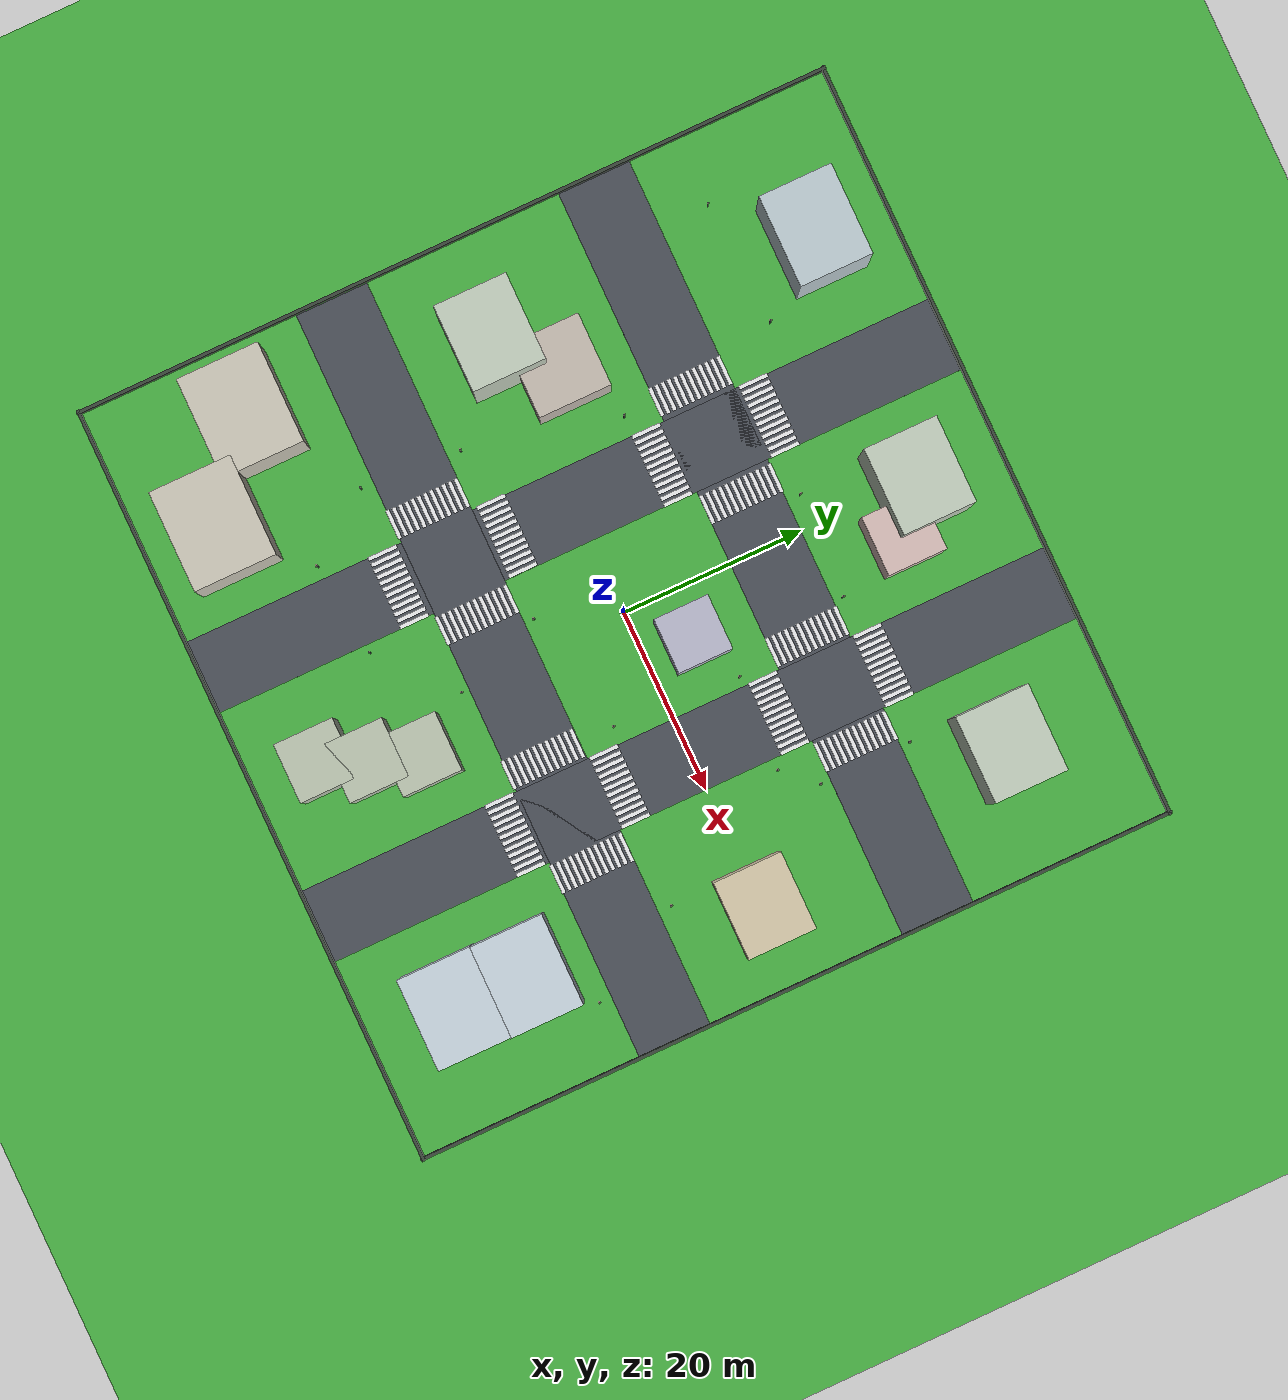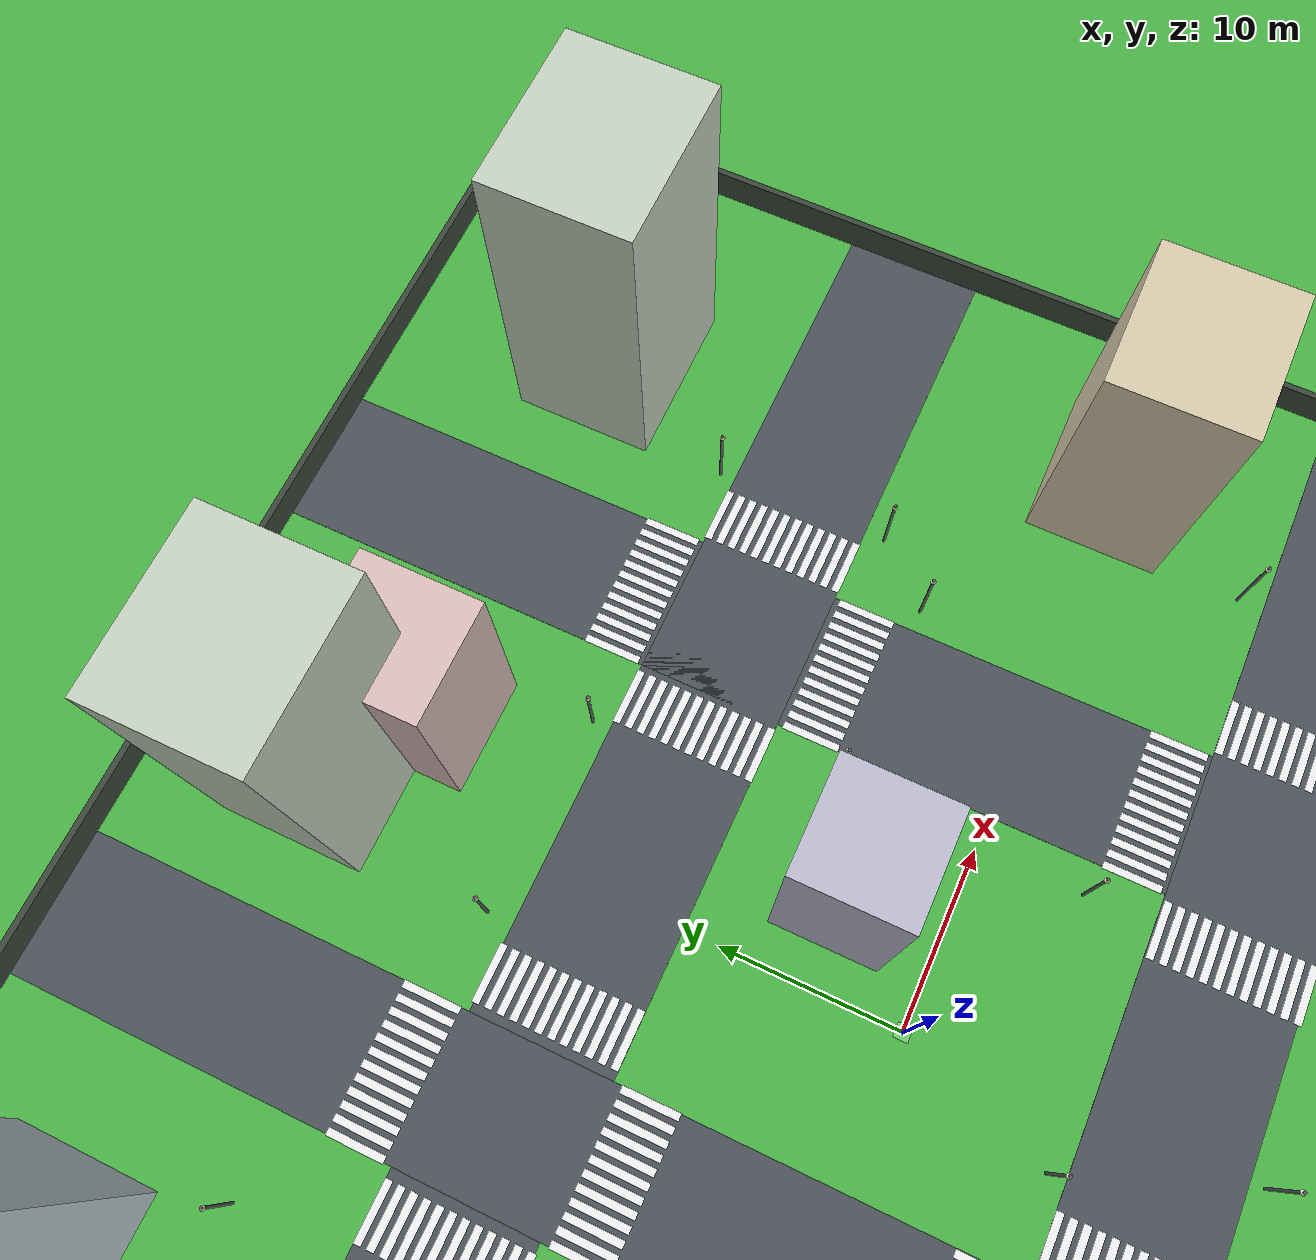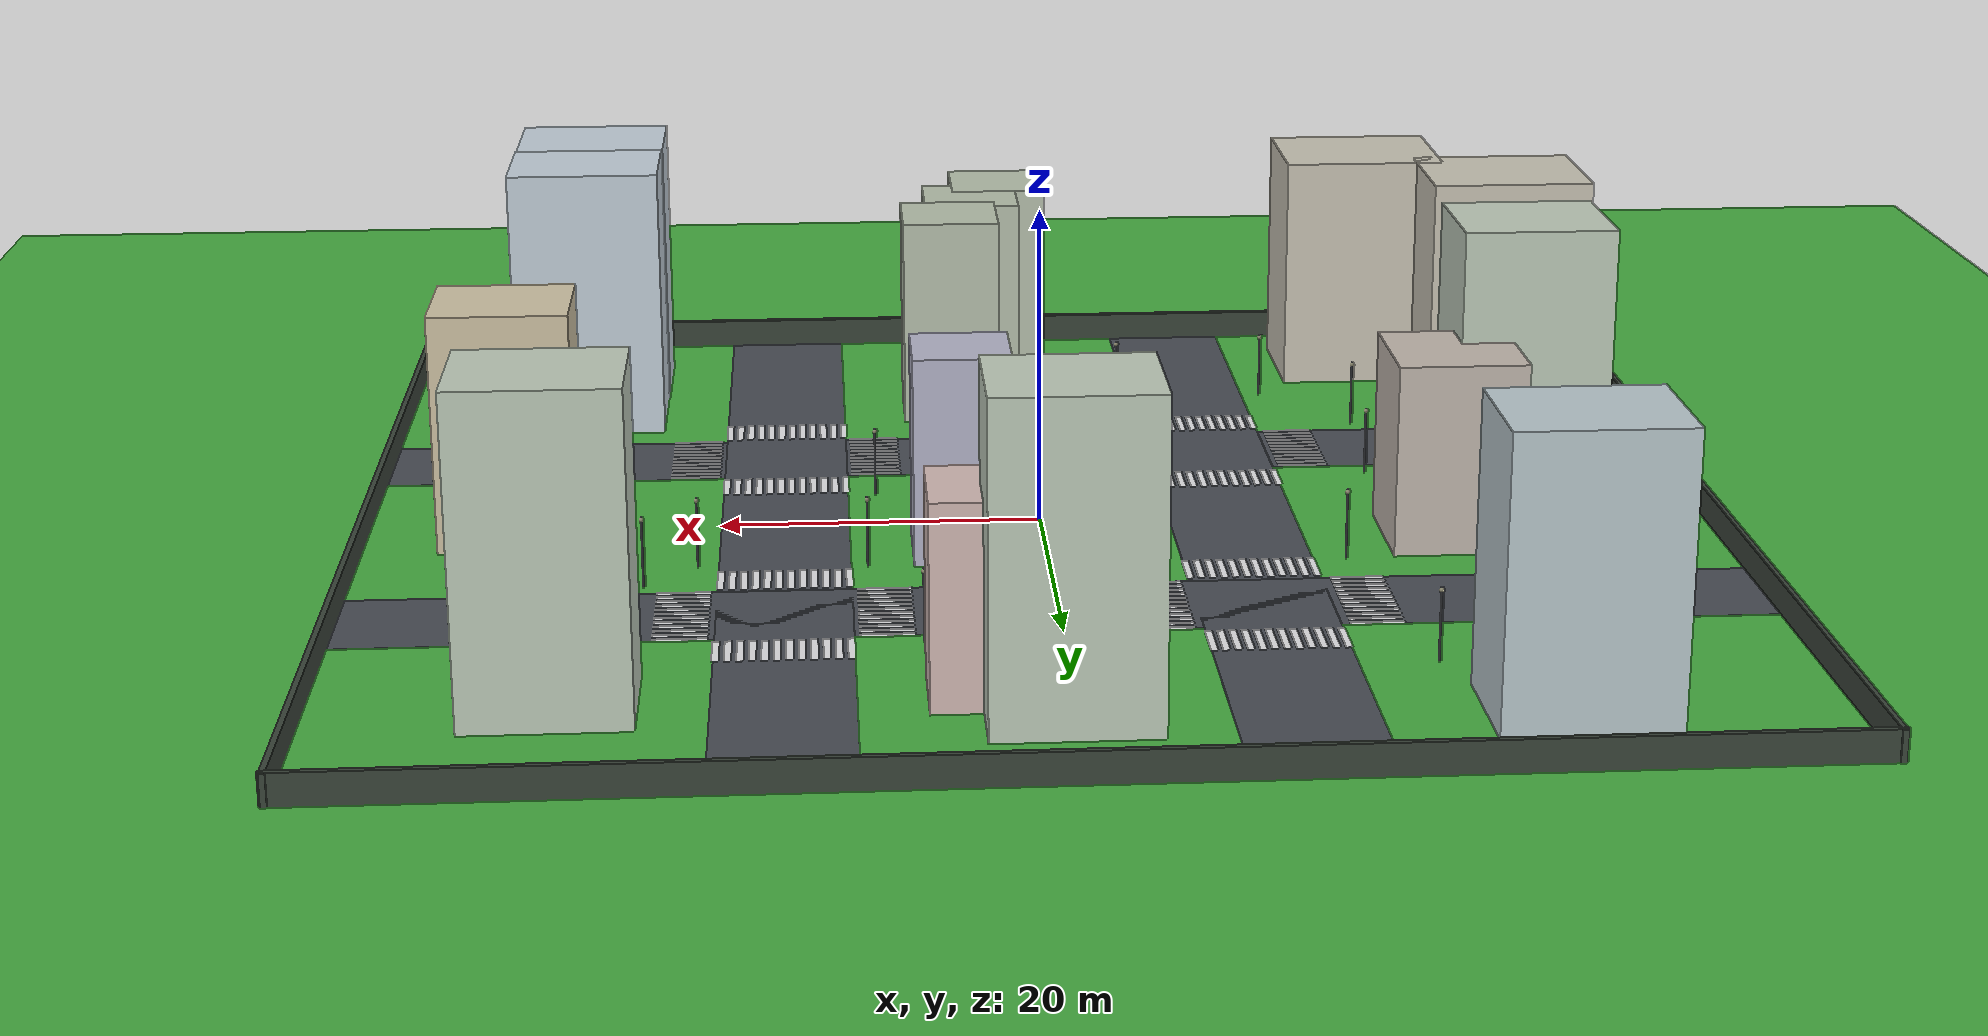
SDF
<sdf version="1.10">
 <world name="city_second">
  <gravity>0 0 -9.8100000000000005</gravity>
  <magnetic_field>6.0000000000000002e-06 2.3e-05 -4.1999999999999998e-05</magnetic_field>
  <physics name="1ms" type="ignored">
   <max_step_size>0.001</max_step_size>
   <real_time_factor>1</real_time_factor>
   <real_time_update_rate>1000</real_time_update_rate>
  </physics>
  <plugin name="gz::sim::systems::Physics" filename="gz-sim-physics-system"/>
  <plugin name="gz::sim::systems::UserCommands" filename="gz-sim-user-commands-system"/>
  <plugin name="gz::sim::systems::SceneBroadcaster" filename="gz-sim-scene-broadcaster-system"/>
  <plugin name="gz::sim::systems::Sensors" filename="gz-sim-sensors-system">
   <render_engine>ogre2</render_engine>
  </plugin>
  <scene>
   <ambient>0.779999971 0.779999971 0.779999971 1</ambient>
   <background>0.779999971 0.879999995 0.970000029 1</background>
   <shadows>true</shadows>
   <grid>false</grid>
  </scene>
  <atmosphere type="adiabatic"/>
  <model name="ground_plane">
   <static>true</static>
   <link name="link">
    <collision name="collision">
     <geometry><plane><normal>0 0 1</normal><size>300 300</size></plane></geometry>
    </collision>
    <visual name="visual">
     <geometry><plane><normal>0 0 1</normal><size>300 300</size></plane></geometry>
     <material>
      <ambient>0.280000001 0.689999998 0.25999999 1</ambient>
      <diffuse>0.280000001 0.689999998 0.25999999 1</diffuse>
      <specular>0.0299999993 0.0299999993 0.0299999993 1</specular>
     </material>
    </visual>
    <inertial>
     <mass>1</mass>
     <inertia><ixx>1</ixx><ixy>0</ixy><ixz>0</ixz><iyy>1</iyy><iyz>0</iyz><izz>1</izz></inertia>
    </inertial>
   </link>
  </model>
  <model name="road_h_2">
   <static>true</static>
   <pose>0 16 0.01 0 0 0</pose>
   <link name="link">
    <collision name="collision"><geometry><box><size>84 8 0.02</size></box></geometry></collision>
    <visual name="visual">
     <geometry><box><size>84 8 0.02</size></box></geometry>
     <material>
      <ambient>0.289999992 0.310000002 0.340000004 1</ambient>
      <diffuse>0.289999992 0.310000002 0.340000004 1</diffuse>
      <specular>0.0299999993 0.0299999993 0.0299999993 1</specular>
     </material>
    </visual>
    <inertial>
     <mass>1</mass>
     <inertia><ixx>1</ixx><ixy>0</ixy><ixz>0</ixz><iyy>1</iyy><iyz>0</iyz><izz>1</izz></inertia>
    </inertial>
   </link>
  </model>
  <model name="road_v_2">
   <static>true</static>
   <pose>16 0 0.01 0 0 0</pose>
   <link name="link">
    <collision name="collision"><geometry><box><size>8 84 0.02</size></box></geometry></collision>
    <visual name="visual">
     <geometry><box><size>8 84 0.02</size></box></geometry>
     <material>
      <ambient>0.289999992 0.310000002 0.340000004 1</ambient>
      <diffuse>0.289999992 0.310000002 0.340000004 1</diffuse>
      <specular>0.0299999993 0.0299999993 0.0299999993 1</specular>
     </material>
    </visual>
    <inertial>
     <mass>1</mass>
     <inertia><ixx>1</ixx><ixy>0</ixy><ixz>0</ixz><iyy>1</iyy><iyz>0</iyz><izz>1</izz></inertia>
    </inertial>
   </link>
  </model>
  <model name="house_1_2">
   <static>true</static>
   <pose>4.5999999999999996 -24.800000000000001 7 0 0 0</pose>
   <link name="link">
    <collision name="collision"><geometry><box><size>6.5 6.5 14</size></box></geometry></collision>
    <visual name="visual">
     <geometry><box><size>6.5 6.5 14</size></box></geometry>
     <material>
      <ambient>0.730000019 0.769999981 0.689999998 1</ambient>
      <diffuse>0.730000019 0.769999981 0.689999998 1</diffuse>
      <specular>0.0299999993 0.0299999993 0.0299999993 1</specular>
     </material>
    </visual>
    <inertial>
     <mass>1</mass>
     <inertia><ixx>1</ixx><ixy>0</ixy><ixz>0</ixz><iyy>1</iyy><iyz>0</iyz><izz>1</izz></inertia>
    </inertial>
   </link>
  </model>
  <model name="house_1_3">
   <static>true</static>
   <pose>29.300000000000001 -24.300000000000001 9 0 0 0</pose>
   <link name="link">
    <collision name="collision"><geometry><box><size>10 8 18</size></box></geometry></collision>
    <visual name="visual">
     <geometry><box><size>10 8 18</size></box></geometry>
     <material>
      <ambient>0.779999971 0.829999983 0.870000005 1</ambient>
      <diffuse>0.779999971 0.829999983 0.870000005 1</diffuse>
      <specular>0.0299999993 0.0299999993 0.0299999993 1</specular>
     </material>
    </visual>
    <inertial>
     <mass>1</mass>
     <inertia><ixx>1</ixx><ixy>0</ixy><ixz>0</ixz><iyy>1</iyy><iyz>0</iyz><izz>1</izz></inertia>
    </inertial>
   </link>
  </model>
  <model name="house_2_1">
   <static>true</static>
   <pose>-25.100000000000001 4.3999999999999995 6 0 0 0</pose>
   <link name="link">
    <collision name="collision"><geometry><box><size>8 8 12</size></box></geometry></collision>
    <visual name="visual">
     <geometry><box><size>8 8 12</size></box></geometry>
     <material>
      <ambient>0.769999981 0.730000019 0.689999998 1</ambient>
      <diffuse>0.769999981 0.730000019 0.689999998 1</diffuse>
      <specular>0.0299999993 0.0299999993 0.0299999993 1</specular>
     </material>
    </visual>
    <inertial>
     <mass>1</mass>
     <inertia><ixx>1</ixx><ixy>0</ixy><ixz>0</ixz><iyy>1</iyy><iyz>0</iyz><izz>1</izz></inertia>
    </inertial>
   </link>
  </model>
  <model name="house_2_2">
   <static>true</static>
   <pose>5.2000000000000002 5.2999999999999998 6.5 0 0 0</pose>
   <link name="link">
    <collision name="collision"><geometry><box><size>6 6 13</size></box></geometry></collision>
    <visual name="visual">
     <geometry><box><size>6 6 13</size></box></geometry>
     <material>
      <ambient>0.720000029 0.720000029 0.800000012 1</ambient>
      <diffuse>0.720000029 0.720000029 0.800000012 1</diffuse>
      <specular>0.0299999993 0.0299999993 0.0299999993 1</specular>
     </material>
    </visual>
    <inertial>
     <mass>1</mass>
     <inertia><ixx>1</ixx><ixy>0</ixy><ixz>0</ixz><iyy>1</iyy><iyz>0</iyz><izz>1</izz></inertia>
    </inertial>
   </link>
  </model>
  <model name="house_3_2">
   <static>true</static>
   <pose>4.8999999999999995 28.899999999999999 6 0 0 0</pose>
   <link name="link">
    <collision name="collision"><geometry><box><size>6.5 6.5 12</size></box></geometry></collision>
    <visual name="visual">
     <geometry><box><size>6.5 6.5 12</size></box></geometry>
     <material>
      <ambient>0.839999974 0.74000001 0.720000029 1</ambient>
      <diffuse>0.839999974 0.74000001 0.720000029 1</diffuse>
      <specular>0.0299999993 0.0299999993 0.0299999993 1</specular>
     </material>
    </visual>
    <inertial>
     <mass>1</mass>
     <inertia><ixx>1</ixx><ixy>0</ixy><ixz>0</ixz><iyy>1</iyy><iyz>0</iyz><izz>1</izz></inertia>
    </inertial>
   </link>
  </model>
  <model name="house_3_3">
   <static>true</static>
   <pose>28.600000000000001 29.399999999999999 9.5 0 0 0</pose>
   <link name="link">
    <collision name="collision"><geometry><box><size>9.5 8 19</size></box></geometry></collision>
    <visual name="visual">
     <geometry><box><size>9.5 8 19</size></box></geometry>
     <material>
      <ambient>0.75999999 0.810000002 0.74000001 1</ambient>
      <diffuse>0.75999999 0.810000002 0.74000001 1</diffuse>
      <specular>0.0299999993 0.0299999993 0.0299999993 1</specular>
     </material>
    </visual>
    <inertial>
     <mass>1</mass>
     <inertia><ixx>1</ixx><ixy>0</ixy><ixz>0</ixz><iyy>1</iyy><iyz>0</iyz><izz>1</izz></inertia>
    </inertial>
   </link>
  </model>
  <model name="robot_spawn_sidewalk_hint">
   <static>true</static>
   <pose>0 0 0.021000000000000001 0 0 0</pose>
   <link name="link">
    <visual name="visual">
     <geometry><box><size>0.80000000000000004 0.80000000000000004 0.0050000000000000001</size></box></geometry>
     <material>
      <ambient>0.550000012 0.860000014 0.569999993 0.649999976</ambient>
      <diffuse>0.550000012 0.860000014 0.569999993 0.649999976</diffuse>
      <specular>0 0 0 1</specular>
     </material>
     <transparency>0.34999999999999998</transparency>
    </visual>
    <inertial>
     <mass>1</mass>
     <inertia><ixx>1</ixx><ixy>0</ixy><ixz>0</ixz><iyy>1</iyy><iyz>0</iyz><izz>1</izz></inertia>
    </inertial>
   </link>
  </model>
  <model name="fence_north">
   <static>true</static>
   <pose>0 42 0.94999999999999996 0 0 0</pose>
   <link name="link">
    <collision name="collision">
     <geometry><box><size>84.5 0.34999999999999998 1.8999999999999999</size></box></geometry>
    </collision>
    <visual name="visual">
     <geometry><box><size>84.5 0.34999999999999998 1.8999999999999999</size></box></geometry>
     <material>
      <ambient>0.230000004 0.270000011 0.230000004 1</ambient>
      <diffuse>0.230000004 0.270000011 0.230000004 1</diffuse>
      <specular>0.0299999993 0.0299999993 0.0299999993 1</specular>
     </material>
    </visual>
    <inertial>
     <mass>1</mass>
     <inertia><ixx>1</ixx><ixy>0</ixy><ixz>0</ixz><iyy>1</iyy><iyz>0</iyz><izz>1</izz></inertia>
    </inertial>
   </link>
  </model>
  <model name="fence_south">
   <static>true</static>
   <pose>0 -42 0.94999999999999996 0 0 0</pose>
   <link name="link">
    <collision name="collision">
     <geometry><box><size>84.5 0.34999999999999998 1.8999999999999999</size></box></geometry>
    </collision>
    <visual name="visual">
     <geometry><box><size>84.5 0.34999999999999998 1.8999999999999999</size></box></geometry>
     <material>
      <ambient>0.230000004 0.270000011 0.230000004 1</ambient>
      <diffuse>0.230000004 0.270000011 0.230000004 1</diffuse>
      <specular>0.0299999993 0.0299999993 0.0299999993 1</specular>
     </material>
    </visual>
    <inertial>
     <mass>1</mass>
     <inertia><ixx>1</ixx><ixy>0</ixy><ixz>0</ixz><iyy>1</iyy><iyz>0</iyz><izz>1</izz></inertia>
    </inertial>
   </link>
  </model>
  <model name="fence_east">
   <static>true</static>
   <pose>42 0 0.94999999999999996 0 0 0</pose>
   <link name="link">
    <collision name="collision">
     <geometry><box><size>0.34999999999999998 84.5 1.8999999999999999</size></box></geometry>
    </collision>
    <visual name="visual">
     <geometry><box><size>0.34999999999999998 84.5 1.8999999999999999</size></box></geometry>
     <material>
      <ambient>0.230000004 0.270000011 0.230000004 1</ambient>
      <diffuse>0.230000004 0.270000011 0.230000004 1</diffuse>
      <specular>0.0299999993 0.0299999993 0.0299999993 1</specular>
     </material>
    </visual>
    <inertial>
     <mass>1</mass>
     <inertia><ixx>1</ixx><ixy>0</ixy><ixz>0</ixz><iyy>1</iyy><iyz>0</iyz><izz>1</izz></inertia>
    </inertial>
   </link>
  </model>
  <model name="fence_west">
   <static>true</static>
   <pose>-42 0 0.94999999999999996 0 0 0</pose>
   <link name="link">
    <collision name="collision">
     <geometry><box><size>0.34999999999999998 84.5 1.8999999999999999</size></box></geometry>
    </collision>
    <visual name="visual">
     <geometry><box><size>0.34999999999999998 84.5 1.8999999999999999</size></box></geometry>
     <material>
      <ambient>0.230000004 0.270000011 0.230000004 1</ambient>
      <diffuse>0.230000004 0.270000011 0.230000004 1</diffuse>
      <specular>0.0299999993 0.0299999993 0.0299999993 1</specular>
     </material>
    </visual>
    <inertial>
     <mass>1</mass>
     <inertia><ixx>1</ixx><ixy>0</ixy><ixz>0</ixz><iyy>1</iyy><iyz>0</iyz><izz>1</izz></inertia>
    </inertial>
   </link>
  </model>
  <model name="crosswalk_h_1_1_south_5">
   <static>true</static>
   <pose>16.033462122134051 21.865937656898115 0.017000000923871994 0 0 0</pose>
   <link name="stripe_1">
    <collision name="collision">
     <geometry><box><size>0.41999999999999998 3.2000000000000002 0.01</size></box></geometry>
    </collision>
    <visual name="visual">
     <geometry><box><size>0.41999999999999998 3.2000000000000002 0.01</size></box></geometry>
     <material>
      <ambient>0.920000017 0.920000017 0.930000007 1</ambient>
      <diffuse>0.920000017 0.920000017 0.930000007 1</diffuse>
      <specular>0.0299999993 0.0299999993 0.0299999993 1</specular>
     </material>
    </visual>
    <pose>-3.8500000000000001 0 0 0 0 0</pose>
    <inertial>
     <mass>1</mass>
     <inertia><ixx>1</ixx><ixy>0</ixy><ixz>0</ixz><iyy>1</iyy><iyz>0</iyz><izz>1</izz></inertia>
    </inertial>
   </link>
   <link name="stripe_2">
    <collision name="collision">
     <geometry><box><size>0.41999999999999998 3.2000000000000002 0.01</size></box></geometry>
    </collision>
    <visual name="visual">
     <geometry><box><size>0.41999999999999998 3.2000000000000002 0.01</size></box></geometry>
     <material>
      <ambient>0.920000017 0.920000017 0.930000007 1</ambient>
      <diffuse>0.920000017 0.920000017 0.930000007 1</diffuse>
      <specular>0.0299999993 0.0299999993 0.0299999993 1</specular>
     </material>
    </visual>
    <pose>-3.1500000000000004 0 0 0 0 0</pose>
    <inertial>
     <mass>1</mass>
     <inertia><ixx>1</ixx><ixy>0</ixy><ixz>0</ixz><iyy>1</iyy><iyz>0</iyz><izz>1</izz></inertia>
    </inertial>
   </link>
   <link name="stripe_3">
    <collision name="collision">
     <geometry><box><size>0.41999999999999998 3.2000000000000002 0.01</size></box></geometry>
    </collision>
    <visual name="visual">
     <geometry><box><size>0.41999999999999998 3.2000000000000002 0.01</size></box></geometry>
     <material>
      <ambient>0.920000017 0.920000017 0.930000007 1</ambient>
      <diffuse>0.920000017 0.920000017 0.930000007 1</diffuse>
      <specular>0.0299999993 0.0299999993 0.0299999993 1</specular>
     </material>
    </visual>
    <pose>-2.4499999999999993 0 0 0 0 0</pose>
    <inertial>
     <mass>1</mass>
     <inertia><ixx>1</ixx><ixy>0</ixy><ixz>0</ixz><iyy>1</iyy><iyz>0</iyz><izz>1</izz></inertia>
    </inertial>
   </link>
   <link name="stripe_4">
    <collision name="collision">
     <geometry><box><size>0.41999999999999998 3.2000000000000002 0.01</size></box></geometry>
    </collision>
    <visual name="visual">
     <geometry><box><size>0.41999999999999998 3.2000000000000002 0.01</size></box></geometry>
     <material>
      <ambient>0.920000017 0.920000017 0.930000007 1</ambient>
      <diffuse>0.920000017 0.920000017 0.930000007 1</diffuse>
      <specular>0.0299999993 0.0299999993 0.0299999993 1</specular>
     </material>
    </visual>
    <pose>-1.75 0 0 0 0 0</pose>
    <inertial>
     <mass>1</mass>
     <inertia><ixx>1</ixx><ixy>0</ixy><ixz>0</ixz><iyy>1</iyy><iyz>0</iyz><izz>1</izz></inertia>
    </inertial>
   </link>
   <link name="stripe_5">
    <collision name="collision">
     <geometry><box><size>0.41999999999999998 3.2000000000000002 0.01</size></box></geometry>
    </collision>
    <visual name="visual">
     <geometry><box><size>0.41999999999999998 3.2000000000000002 0.01</size></box></geometry>
     <material>
      <ambient>0.920000017 0.920000017 0.930000007 1</ambient>
      <diffuse>0.920000017 0.920000017 0.930000007 1</diffuse>
      <specular>0.0299999993 0.0299999993 0.0299999993 1</specular>
     </material>
    </visual>
    <pose>-1.0500000000000007 0 0 0 0 0</pose>
    <inertial>
     <mass>1</mass>
     <inertia><ixx>1</ixx><ixy>0</ixy><ixz>0</ixz><iyy>1</iyy><iyz>0</iyz><izz>1</izz></inertia>
    </inertial>
   </link>
   <link name="stripe_6">
    <collision name="collision">
     <geometry><box><size>0.41999999999999998 3.2000000000000002 0.01</size></box></geometry>
    </collision>
    <visual name="visual">
     <geometry><box><size>0.41999999999999998 3.2000000000000002 0.01</size></box></geometry>
     <material>
      <ambient>0.920000017 0.920000017 0.930000007 1</ambient>
      <diffuse>0.920000017 0.920000017 0.930000007 1</diffuse>
      <specular>0.0299999993 0.0299999993 0.0299999993 1</specular>
     </material>
    </visual>
    <pose>-0.34999999999999964 0 0 0 0 0</pose>
    <inertial>
     <mass>1</mass>
     <inertia><ixx>1</ixx><ixy>0</ixy><ixz>0</ixz><iyy>1</iyy><iyz>0</iyz><izz>1</izz></inertia>
    </inertial>
   </link>
   <link name="stripe_7">
    <collision name="collision">
     <geometry><box><size>0.41999999999999998 3.2000000000000002 0.01</size></box></geometry>
    </collision>
    <visual name="visual">
     <geometry><box><size>0.41999999999999998 3.2000000000000002 0.01</size></box></geometry>
     <material>
      <ambient>0.920000017 0.920000017 0.930000007 1</ambient>
      <diffuse>0.920000017 0.920000017 0.930000007 1</diffuse>
      <specular>0.0299999993 0.0299999993 0.0299999993 1</specular>
     </material>
    </visual>
    <pose>0.35000000000000142 0 0 0 0 0</pose>
    <inertial>
     <mass>1</mass>
     <inertia><ixx>1</ixx><ixy>0</ixy><ixz>0</ixz><iyy>1</iyy><iyz>0</iyz><izz>1</izz></inertia>
    </inertial>
   </link>
   <link name="stripe_8">
    <collision name="collision">
     <geometry><box><size>0.41999999999999998 3.2000000000000002 0.01</size></box></geometry>
    </collision>
    <visual name="visual">
     <geometry><box><size>0.41999999999999998 3.2000000000000002 0.01</size></box></geometry>
     <material>
      <ambient>0.920000017 0.920000017 0.930000007 1</ambient>
      <diffuse>0.920000017 0.920000017 0.930000007 1</diffuse>
      <specular>0.0299999993 0.0299999993 0.0299999993 1</specular>
     </material>
    </visual>
    <pose>1.0500000000000007 0 0 0 0 0</pose>
    <inertial>
     <mass>1</mass>
     <inertia><ixx>1</ixx><ixy>0</ixy><ixz>0</ixz><iyy>1</iyy><iyz>0</iyz><izz>1</izz></inertia>
    </inertial>
   </link>
   <link name="stripe_9">
    <collision name="collision">
     <geometry><box><size>0.41999999999999998 3.2000000000000002 0.01</size></box></geometry>
    </collision>
    <visual name="visual">
     <geometry><box><size>0.41999999999999998 3.2000000000000002 0.01</size></box></geometry>
     <material>
      <ambient>0.920000017 0.920000017 0.930000007 1</ambient>
      <diffuse>0.920000017 0.920000017 0.930000007 1</diffuse>
      <specular>0.0299999993 0.0299999993 0.0299999993 1</specular>
     </material>
    </visual>
    <pose>1.75 0 0 0 0 0</pose>
    <inertial>
     <mass>1</mass>
     <inertia><ixx>1</ixx><ixy>0</ixy><ixz>0</ixz><iyy>1</iyy><iyz>0</iyz><izz>1</izz></inertia>
    </inertial>
   </link>
   <link name="stripe_10">
    <collision name="collision">
     <geometry><box><size>0.41999999999999998 3.2000000000000002 0.01</size></box></geometry>
    </collision>
    <visual name="visual">
     <geometry><box><size>0.41999999999999998 3.2000000000000002 0.01</size></box></geometry>
     <material>
      <ambient>0.920000017 0.920000017 0.930000007 1</ambient>
      <diffuse>0.920000017 0.920000017 0.930000007 1</diffuse>
      <specular>0.0299999993 0.0299999993 0.0299999993 1</specular>
     </material>
    </visual>
    <pose>2.4499999999999993 0 0 0 0 0</pose>
    <inertial>
     <mass>1</mass>
     <inertia><ixx>1</ixx><ixy>0</ixy><ixz>0</ixz><iyy>1</iyy><iyz>0</iyz><izz>1</izz></inertia>
    </inertial>
   </link>
   <link name="stripe_11">
    <collision name="collision">
     <geometry><box><size>0.41999999999999998 3.2000000000000002 0.01</size></box></geometry>
    </collision>
    <visual name="visual">
     <geometry><box><size>0.41999999999999998 3.2000000000000002 0.01</size></box></geometry>
     <material>
      <ambient>0.920000017 0.920000017 0.930000007 1</ambient>
      <diffuse>0.920000017 0.920000017 0.930000007 1</diffuse>
      <specular>0.0299999993 0.0299999993 0.0299999993 1</specular>
     </material>
    </visual>
    <pose>3.1499999999999986 0 0 0 0 0</pose>
    <inertial>
     <mass>1</mass>
     <inertia><ixx>1</ixx><ixy>0</ixy><ixz>0</ixz><iyy>1</iyy><iyz>0</iyz><izz>1</izz></inertia>
    </inertial>
   </link>
   <link name="stripe_12">
    <collision name="collision">
     <geometry><box><size>0.41999999999999998 3.2000000000000002 0.01</size></box></geometry>
    </collision>
    <visual name="visual">
     <geometry><box><size>0.41999999999999998 3.2000000000000002 0.01</size></box></geometry>
     <material>
      <ambient>0.920000017 0.920000017 0.930000007 1</ambient>
      <diffuse>0.920000017 0.920000017 0.930000007 1</diffuse>
      <specular>0.0299999993 0.0299999993 0.0299999993 1</specular>
     </material>
    </visual>
    <pose>3.8500000000000014 0 0 0 0 0</pose>
    <inertial>
     <mass>1</mass>
     <inertia><ixx>1</ixx><ixy>0</ixy><ixz>0</ixz><iyy>1</iyy><iyz>0</iyz><izz>1</izz></inertia>
    </inertial>
   </link>
  </model>
  <model name="crosswalk_h_1_1_south_6">
   <static>true</static>
   <pose>15.980713777312754 10.092161600737073 0.017000000923871994 0 0 0</pose>
   <link name="stripe_1">
    <collision name="collision">
     <geometry><box><size>0.41999999999999998 3.2000000000000002 0.01</size></box></geometry>
    </collision>
    <visual name="visual">
     <geometry><box><size>0.41999999999999998 3.2000000000000002 0.01</size></box></geometry>
     <material>
      <ambient>0.920000017 0.920000017 0.930000007 1</ambient>
      <diffuse>0.920000017 0.920000017 0.930000007 1</diffuse>
      <specular>0.0299999993 0.0299999993 0.0299999993 1</specular>
     </material>
    </visual>
    <pose>-3.8500000000000001 0 0 0 0 0</pose>
    <inertial>
     <mass>1</mass>
     <inertia><ixx>1</ixx><ixy>0</ixy><ixz>0</ixz><iyy>1</iyy><iyz>0</iyz><izz>1</izz></inertia>
    </inertial>
   </link>
   <link name="stripe_2">
    <collision name="collision">
     <geometry><box><size>0.41999999999999998 3.2000000000000002 0.01</size></box></geometry>
    </collision>
    <visual name="visual">
     <geometry><box><size>0.41999999999999998 3.2000000000000002 0.01</size></box></geometry>
     <material>
      <ambient>0.920000017 0.920000017 0.930000007 1</ambient>
      <diffuse>0.920000017 0.920000017 0.930000007 1</diffuse>
      <specular>0.0299999993 0.0299999993 0.0299999993 1</specular>
     </material>
    </visual>
    <pose>-3.1500000000000004 0 0 0 0 0</pose>
    <inertial>
     <mass>1</mass>
     <inertia><ixx>1</ixx><ixy>0</ixy><ixz>0</ixz><iyy>1</iyy><iyz>0</iyz><izz>1</izz></inertia>
    </inertial>
   </link>
   <link name="stripe_3">
    <collision name="collision">
     <geometry><box><size>0.41999999999999998 3.2000000000000002 0.01</size></box></geometry>
    </collision>
    <visual name="visual">
     <geometry><box><size>0.41999999999999998 3.2000000000000002 0.01</size></box></geometry>
     <material>
      <ambient>0.920000017 0.920000017 0.930000007 1</ambient>
      <diffuse>0.920000017 0.920000017 0.930000007 1</diffuse>
      <specular>0.0299999993 0.0299999993 0.0299999993 1</specular>
     </material>
    </visual>
    <pose>-2.4499999999999993 0 0 0 0 0</pose>
    <inertial>
     <mass>1</mass>
     <inertia><ixx>1</ixx><ixy>0</ixy><ixz>0</ixz><iyy>1</iyy><iyz>0</iyz><izz>1</izz></inertia>
    </inertial>
   </link>
   <link name="stripe_4">
    <collision name="collision">
     <geometry><box><size>0.41999999999999998 3.2000000000000002 0.01</size></box></geometry>
    </collision>
    <visual name="visual">
     <geometry><box><size>0.41999999999999998 3.2000000000000002 0.01</size></box></geometry>
     <material>
      <ambient>0.920000017 0.920000017 0.930000007 1</ambient>
      <diffuse>0.920000017 0.920000017 0.930000007 1</diffuse>
      <specular>0.0299999993 0.0299999993 0.0299999993 1</specular>
     </material>
    </visual>
    <pose>-1.75 0 0 0 0 0</pose>
    <inertial>
     <mass>1</mass>
     <inertia><ixx>1</ixx><ixy>0</ixy><ixz>0</ixz><iyy>1</iyy><iyz>0</iyz><izz>1</izz></inertia>
    </inertial>
   </link>
   <link name="stripe_5">
    <collision name="collision">
     <geometry><box><size>0.41999999999999998 3.2000000000000002 0.01</size></box></geometry>
    </collision>
    <visual name="visual">
     <geometry><box><size>0.41999999999999998 3.2000000000000002 0.01</size></box></geometry>
     <material>
      <ambient>0.920000017 0.920000017 0.930000007 1</ambient>
      <diffuse>0.920000017 0.920000017 0.930000007 1</diffuse>
      <specular>0.0299999993 0.0299999993 0.0299999993 1</specular>
     </material>
    </visual>
    <pose>-1.0500000000000007 0 0 0 0 0</pose>
    <inertial>
     <mass>1</mass>
     <inertia><ixx>1</ixx><ixy>0</ixy><ixz>0</ixz><iyy>1</iyy><iyz>0</iyz><izz>1</izz></inertia>
    </inertial>
   </link>
   <link name="stripe_6">
    <collision name="collision">
     <geometry><box><size>0.41999999999999998 3.2000000000000002 0.01</size></box></geometry>
    </collision>
    <visual name="visual">
     <geometry><box><size>0.41999999999999998 3.2000000000000002 0.01</size></box></geometry>
     <material>
      <ambient>0.920000017 0.920000017 0.930000007 1</ambient>
      <diffuse>0.920000017 0.920000017 0.930000007 1</diffuse>
      <specular>0.0299999993 0.0299999993 0.0299999993 1</specular>
     </material>
    </visual>
    <pose>-0.34999999999999964 0 0 0 0 0</pose>
    <inertial>
     <mass>1</mass>
     <inertia><ixx>1</ixx><ixy>0</ixy><ixz>0</ixz><iyy>1</iyy><iyz>0</iyz><izz>1</izz></inertia>
    </inertial>
   </link>
   <link name="stripe_7">
    <collision name="collision">
     <geometry><box><size>0.41999999999999998 3.2000000000000002 0.01</size></box></geometry>
    </collision>
    <visual name="visual">
     <geometry><box><size>0.41999999999999998 3.2000000000000002 0.01</size></box></geometry>
     <material>
      <ambient>0.920000017 0.920000017 0.930000007 1</ambient>
      <diffuse>0.920000017 0.920000017 0.930000007 1</diffuse>
      <specular>0.0299999993 0.0299999993 0.0299999993 1</specular>
     </material>
    </visual>
    <pose>0.35000000000000142 0 0 0 0 0</pose>
    <inertial>
     <mass>1</mass>
     <inertia><ixx>1</ixx><ixy>0</ixy><ixz>0</ixz><iyy>1</iyy><iyz>0</iyz><izz>1</izz></inertia>
    </inertial>
   </link>
   <link name="stripe_8">
    <collision name="collision">
     <geometry><box><size>0.41999999999999998 3.2000000000000002 0.01</size></box></geometry>
    </collision>
    <visual name="visual">
     <geometry><box><size>0.41999999999999998 3.2000000000000002 0.01</size></box></geometry>
     <material>
      <ambient>0.920000017 0.920000017 0.930000007 1</ambient>
      <diffuse>0.920000017 0.920000017 0.930000007 1</diffuse>
      <specular>0.0299999993 0.0299999993 0.0299999993 1</specular>
     </material>
    </visual>
    <pose>1.0500000000000007 0 0 0 0 0</pose>
    <inertial>
     <mass>1</mass>
     <inertia><ixx>1</ixx><ixy>0</ixy><ixz>0</ixz><iyy>1</iyy><iyz>0</iyz><izz>1</izz></inertia>
    </inertial>
   </link>
   <link name="stripe_9">
    <collision name="collision">
     <geometry><box><size>0.41999999999999998 3.2000000000000002 0.01</size></box></geometry>
    </collision>
    <visual name="visual">
     <geometry><box><size>0.41999999999999998 3.2000000000000002 0.01</size></box></geometry>
     <material>
      <ambient>0.920000017 0.920000017 0.930000007 1</ambient>
      <diffuse>0.920000017 0.920000017 0.930000007 1</diffuse>
      <specular>0.0299999993 0.0299999993 0.0299999993 1</specular>
     </material>
    </visual>
    <pose>1.75 0 0 0 0 0</pose>
    <inertial>
     <mass>1</mass>
     <inertia><ixx>1</ixx><ixy>0</ixy><ixz>0</ixz><iyy>1</iyy><iyz>0</iyz><izz>1</izz></inertia>
    </inertial>
   </link>
   <link name="stripe_10">
    <collision name="collision">
     <geometry><box><size>0.41999999999999998 3.2000000000000002 0.01</size></box></geometry>
    </collision>
    <visual name="visual">
     <geometry><box><size>0.41999999999999998 3.2000000000000002 0.01</size></box></geometry>
     <material>
      <ambient>0.920000017 0.920000017 0.930000007 1</ambient>
      <diffuse>0.920000017 0.920000017 0.930000007 1</diffuse>
      <specular>0.0299999993 0.0299999993 0.0299999993 1</specular>
     </material>
    </visual>
    <pose>2.4499999999999993 0 0 0 0 0</pose>
    <inertial>
     <mass>1</mass>
     <inertia><ixx>1</ixx><ixy>0</ixy><ixz>0</ixz><iyy>1</iyy><iyz>0</iyz><izz>1</izz></inertia>
    </inertial>
   </link>
   <link name="stripe_11">
    <collision name="collision">
     <geometry><box><size>0.41999999999999998 3.2000000000000002 0.01</size></box></geometry>
    </collision>
    <visual name="visual">
     <geometry><box><size>0.41999999999999998 3.2000000000000002 0.01</size></box></geometry>
     <material>
      <ambient>0.920000017 0.920000017 0.930000007 1</ambient>
      <diffuse>0.920000017 0.920000017 0.930000007 1</diffuse>
      <specular>0.0299999993 0.0299999993 0.0299999993 1</specular>
     </material>
    </visual>
    <pose>3.1499999999999986 0 0 0 0 0</pose>
    <inertial>
     <mass>1</mass>
     <inertia><ixx>1</ixx><ixy>0</ixy><ixz>0</ixz><iyy>1</iyy><iyz>0</iyz><izz>1</izz></inertia>
    </inertial>
   </link>
   <link name="stripe_12">
    <collision name="collision">
     <geometry><box><size>0.41999999999999998 3.2000000000000002 0.01</size></box></geometry>
    </collision>
    <visual name="visual">
     <geometry><box><size>0.41999999999999998 3.2000000000000002 0.01</size></box></geometry>
     <material>
      <ambient>0.920000017 0.920000017 0.930000007 1</ambient>
      <diffuse>0.920000017 0.920000017 0.930000007 1</diffuse>
      <specular>0.0299999993 0.0299999993 0.0299999993 1</specular>
     </material>
    </visual>
    <pose>3.8500000000000014 0 0 0 0 0</pose>
    <inertial>
     <mass>1</mass>
     <inertia><ixx>1</ixx><ixy>0</ixy><ixz>0</ixz><iyy>1</iyy><iyz>0</iyz><izz>1</izz></inertia>
    </inertial>
   </link>
  </model>
  <model name="crosswalk_v_2_1_east_6">
   <static>true</static>
   <pose>10.091694509516831 16.024816834297141 0.017000000923871994 0 0 0</pose>
   <link name="stripe_1">
    <collision name="collision">
     <geometry><box><size>3.2000000000000002 0.41999999999999998 0.01</size></box></geometry>
    </collision>
    <visual name="visual">
     <geometry><box><size>3.2000000000000002 0.41999999999999998 0.01</size></box></geometry>
     <material>
      <ambient>0.920000017 0.920000017 0.930000007 1</ambient>
      <diffuse>0.920000017 0.920000017 0.930000007 1</diffuse>
      <specular>0.0299999993 0.0299999993 0.0299999993 1</specular>
     </material>
    </visual>
    <pose>0 -3.8500000000000001 0 0 0 0</pose>
    <inertial>
     <mass>1</mass>
     <inertia><ixx>1</ixx><ixy>0</ixy><ixz>0</ixz><iyy>1</iyy><iyz>0</iyz><izz>1</izz></inertia>
    </inertial>
   </link>
   <link name="stripe_2">
    <collision name="collision">
     <geometry><box><size>3.2000000000000002 0.41999999999999998 0.01</size></box></geometry>
    </collision>
    <visual name="visual">
     <geometry><box><size>3.2000000000000002 0.41999999999999998 0.01</size></box></geometry>
     <material>
      <ambient>0.920000017 0.920000017 0.930000007 1</ambient>
      <diffuse>0.920000017 0.920000017 0.930000007 1</diffuse>
      <specular>0.0299999993 0.0299999993 0.0299999993 1</specular>
     </material>
    </visual>
    <pose>0 -3.1500000000000004 0 0 0 0</pose>
    <inertial>
     <mass>1</mass>
     <inertia><ixx>1</ixx><ixy>0</ixy><ixz>0</ixz><iyy>1</iyy><iyz>0</iyz><izz>1</izz></inertia>
    </inertial>
   </link>
   <link name="stripe_3">
    <collision name="collision">
     <geometry><box><size>3.2000000000000002 0.41999999999999998 0.01</size></box></geometry>
    </collision>
    <visual name="visual">
     <geometry><box><size>3.2000000000000002 0.41999999999999998 0.01</size></box></geometry>
     <material>
      <ambient>0.920000017 0.920000017 0.930000007 1</ambient>
      <diffuse>0.920000017 0.920000017 0.930000007 1</diffuse>
      <specular>0.0299999993 0.0299999993 0.0299999993 1</specular>
     </material>
    </visual>
    <pose>0 -2.4499999999999993 0 0 0 0</pose>
    <inertial>
     <mass>1</mass>
     <inertia><ixx>1</ixx><ixy>0</ixy><ixz>0</ixz><iyy>1</iyy><iyz>0</iyz><izz>1</izz></inertia>
    </inertial>
   </link>
   <link name="stripe_4">
    <collision name="collision">
     <geometry><box><size>3.2000000000000002 0.41999999999999998 0.01</size></box></geometry>
    </collision>
    <visual name="visual">
     <geometry><box><size>3.2000000000000002 0.41999999999999998 0.01</size></box></geometry>
     <material>
      <ambient>0.920000017 0.920000017 0.930000007 1</ambient>
      <diffuse>0.920000017 0.920000017 0.930000007 1</diffuse>
      <specular>0.0299999993 0.0299999993 0.0299999993 1</specular>
     </material>
    </visual>
    <pose>0 -1.75 0 0 0 0</pose>
    <inertial>
     <mass>1</mass>
     <inertia><ixx>1</ixx><ixy>0</ixy><ixz>0</ixz><iyy>1</iyy><iyz>0</iyz><izz>1</izz></inertia>
    </inertial>
   </link>
   <link name="stripe_5">
    <collision name="collision">
     <geometry><box><size>3.2000000000000002 0.41999999999999998 0.01</size></box></geometry>
    </collision>
    <visual name="visual">
     <geometry><box><size>3.2000000000000002 0.41999999999999998 0.01</size></box></geometry>
     <material>
      <ambient>0.920000017 0.920000017 0.930000007 1</ambient>
      <diffuse>0.920000017 0.920000017 0.930000007 1</diffuse>
      <specular>0.0299999993 0.0299999993 0.0299999993 1</specular>
     </material>
    </visual>
    <pose>0 -1.0500000000000007 0 0 0 0</pose>
    <inertial>
     <mass>1</mass>
     <inertia><ixx>1</ixx><ixy>0</ixy><ixz>0</ixz><iyy>1</iyy><iyz>0</iyz><izz>1</izz></inertia>
    </inertial>
   </link>
   <link name="stripe_6">
    <collision name="collision">
     <geometry><box><size>3.2000000000000002 0.41999999999999998 0.01</size></box></geometry>
    </collision>
    <visual name="visual">
     <geometry><box><size>3.2000000000000002 0.41999999999999998 0.01</size></box></geometry>
     <material>
      <ambient>0.920000017 0.920000017 0.930000007 1</ambient>
      <diffuse>0.920000017 0.920000017 0.930000007 1</diffuse>
      <specular>0.0299999993 0.0299999993 0.0299999993 1</specular>
     </material>
    </visual>
    <pose>0 -0.34999999999999964 0 0 0 0</pose>
    <inertial>
     <mass>1</mass>
     <inertia><ixx>1</ixx><ixy>0</ixy><ixz>0</ixz><iyy>1</iyy><iyz>0</iyz><izz>1</izz></inertia>
    </inertial>
   </link>
   <link name="stripe_7">
    <collision name="collision">
     <geometry><box><size>3.2000000000000002 0.41999999999999998 0.01</size></box></geometry>
    </collision>
    <visual name="visual">
     <geometry><box><size>3.2000000000000002 0.41999999999999998 0.01</size></box></geometry>
     <material>
      <ambient>0.920000017 0.920000017 0.930000007 1</ambient>
      <diffuse>0.920000017 0.920000017 0.930000007 1</diffuse>
      <specular>0.0299999993 0.0299999993 0.0299999993 1</specular>
     </material>
    </visual>
    <pose>0 0.35000000000000142 0 0 0 0</pose>
    <inertial>
     <mass>1</mass>
     <inertia><ixx>1</ixx><ixy>0</ixy><ixz>0</ixz><iyy>1</iyy><iyz>0</iyz><izz>1</izz></inertia>
    </inertial>
   </link>
   <link name="stripe_8">
    <collision name="collision">
     <geometry><box><size>3.2000000000000002 0.41999999999999998 0.01</size></box></geometry>
    </collision>
    <visual name="visual">
     <geometry><box><size>3.2000000000000002 0.41999999999999998 0.01</size></box></geometry>
     <material>
      <ambient>0.920000017 0.920000017 0.930000007 1</ambient>
      <diffuse>0.920000017 0.920000017 0.930000007 1</diffuse>
      <specular>0.0299999993 0.0299999993 0.0299999993 1</specular>
     </material>
    </visual>
    <pose>0 1.0500000000000007 0 0 0 0</pose>
    <inertial>
     <mass>1</mass>
     <inertia><ixx>1</ixx><ixy>0</ixy><ixz>0</ixz><iyy>1</iyy><iyz>0</iyz><izz>1</izz></inertia>
    </inertial>
   </link>
   <link name="stripe_9">
    <collision name="collision">
     <geometry><box><size>3.2000000000000002 0.41999999999999998 0.01</size></box></geometry>
    </collision>
    <visual name="visual">
     <geometry><box><size>3.2000000000000002 0.41999999999999998 0.01</size></box></geometry>
     <material>
      <ambient>0.920000017 0.920000017 0.930000007 1</ambient>
      <diffuse>0.920000017 0.920000017 0.930000007 1</diffuse>
      <specular>0.0299999993 0.0299999993 0.0299999993 1</specular>
     </material>
    </visual>
    <pose>0 1.75 0 0 0 0</pose>
    <inertial>
     <mass>1</mass>
     <inertia><ixx>1</ixx><ixy>0</ixy><ixz>0</ixz><iyy>1</iyy><iyz>0</iyz><izz>1</izz></inertia>
    </inertial>
   </link>
   <link name="stripe_10">
    <collision name="collision">
     <geometry><box><size>3.2000000000000002 0.41999999999999998 0.01</size></box></geometry>
    </collision>
    <visual name="visual">
     <geometry><box><size>3.2000000000000002 0.41999999999999998 0.01</size></box></geometry>
     <material>
      <ambient>0.920000017 0.920000017 0.930000007 1</ambient>
      <diffuse>0.920000017 0.920000017 0.930000007 1</diffuse>
      <specular>0.0299999993 0.0299999993 0.0299999993 1</specular>
     </material>
    </visual>
    <pose>0 2.4499999999999993 0 0 0 0</pose>
    <inertial>
     <mass>1</mass>
     <inertia><ixx>1</ixx><ixy>0</ixy><ixz>0</ixz><iyy>1</iyy><iyz>0</iyz><izz>1</izz></inertia>
    </inertial>
   </link>
   <link name="stripe_11">
    <collision name="collision">
     <geometry><box><size>3.2000000000000002 0.41999999999999998 0.01</size></box></geometry>
    </collision>
    <visual name="visual">
     <geometry><box><size>3.2000000000000002 0.41999999999999998 0.01</size></box></geometry>
     <material>
      <ambient>0.920000017 0.920000017 0.930000007 1</ambient>
      <diffuse>0.920000017 0.920000017 0.930000007 1</diffuse>
      <specular>0.0299999993 0.0299999993 0.0299999993 1</specular>
     </material>
    </visual>
    <pose>0 3.1499999999999986 0 0 0 0</pose>
    <inertial>
     <mass>1</mass>
     <inertia><ixx>1</ixx><ixy>0</ixy><ixz>0</ixz><iyy>1</iyy><iyz>0</iyz><izz>1</izz></inertia>
    </inertial>
   </link>
   <link name="stripe_12">
    <collision name="collision">
     <geometry><box><size>3.2000000000000002 0.41999999999999998 0.01</size></box></geometry>
    </collision>
    <visual name="visual">
     <geometry><box><size>3.2000000000000002 0.41999999999999998 0.01</size></box></geometry>
     <material>
      <ambient>0.920000017 0.920000017 0.930000007 1</ambient>
      <diffuse>0.920000017 0.920000017 0.930000007 1</diffuse>
      <specular>0.0299999993 0.0299999993 0.0299999993 1</specular>
     </material>
    </visual>
    <pose>0 3.8500000000000014 0 0 0 0</pose>
    <inertial>
     <mass>1</mass>
     <inertia><ixx>1</ixx><ixy>0</ixy><ixz>0</ixz><iyy>1</iyy><iyz>0</iyz><izz>1</izz></inertia>
    </inertial>
   </link>
  </model>
  <model name="crosswalk_v_2_1_east_7">
   <static>true</static>
   <pose>21.941864420511155 16.021662532417597 0.017000000923871994 0 0 0</pose>
   <link name="stripe_1">
    <collision name="collision">
     <geometry><box><size>3.2000000000000002 0.41999999999999998 0.01</size></box></geometry>
    </collision>
    <visual name="visual">
     <geometry><box><size>3.2000000000000002 0.41999999999999998 0.01</size></box></geometry>
     <material>
      <ambient>0.920000017 0.920000017 0.930000007 1</ambient>
      <diffuse>0.920000017 0.920000017 0.930000007 1</diffuse>
      <specular>0.0299999993 0.0299999993 0.0299999993 1</specular>
     </material>
    </visual>
    <pose>0 -3.8500000000000001 0 0 0 0</pose>
    <inertial>
     <mass>1</mass>
     <inertia><ixx>1</ixx><ixy>0</ixy><ixz>0</ixz><iyy>1</iyy><iyz>0</iyz><izz>1</izz></inertia>
    </inertial>
   </link>
   <link name="stripe_2">
    <collision name="collision">
     <geometry><box><size>3.2000000000000002 0.41999999999999998 0.01</size></box></geometry>
    </collision>
    <visual name="visual">
     <geometry><box><size>3.2000000000000002 0.41999999999999998 0.01</size></box></geometry>
     <material>
      <ambient>0.920000017 0.920000017 0.930000007 1</ambient>
      <diffuse>0.920000017 0.920000017 0.930000007 1</diffuse>
      <specular>0.0299999993 0.0299999993 0.0299999993 1</specular>
     </material>
    </visual>
    <pose>0 -3.1500000000000004 0 0 0 0</pose>
    <inertial>
     <mass>1</mass>
     <inertia><ixx>1</ixx><ixy>0</ixy><ixz>0</ixz><iyy>1</iyy><iyz>0</iyz><izz>1</izz></inertia>
    </inertial>
   </link>
   <link name="stripe_3">
    <collision name="collision">
     <geometry><box><size>3.2000000000000002 0.41999999999999998 0.01</size></box></geometry>
    </collision>
    <visual name="visual">
     <geometry><box><size>3.2000000000000002 0.41999999999999998 0.01</size></box></geometry>
     <material>
      <ambient>0.920000017 0.920000017 0.930000007 1</ambient>
      <diffuse>0.920000017 0.920000017 0.930000007 1</diffuse>
      <specular>0.0299999993 0.0299999993 0.0299999993 1</specular>
     </material>
    </visual>
    <pose>0 -2.4499999999999993 0 0 0 0</pose>
    <inertial>
     <mass>1</mass>
     <inertia><ixx>1</ixx><ixy>0</ixy><ixz>0</ixz><iyy>1</iyy><iyz>0</iyz><izz>1</izz></inertia>
    </inertial>
   </link>
   <link name="stripe_4">
    <collision name="collision">
     <geometry><box><size>3.2000000000000002 0.41999999999999998 0.01</size></box></geometry>
    </collision>
    <visual name="visual">
     <geometry><box><size>3.2000000000000002 0.41999999999999998 0.01</size></box></geometry>
     <material>
      <ambient>0.920000017 0.920000017 0.930000007 1</ambient>
      <diffuse>0.920000017 0.920000017 0.930000007 1</diffuse>
      <specular>0.0299999993 0.0299999993 0.0299999993 1</specular>
     </material>
    </visual>
    <pose>0 -1.75 0 0 0 0</pose>
    <inertial>
     <mass>1</mass>
     <inertia><ixx>1</ixx><ixy>0</ixy><ixz>0</ixz><iyy>1</iyy><iyz>0</iyz><izz>1</izz></inertia>
    </inertial>
   </link>
   <link name="stripe_5">
    <collision name="collision">
     <geometry><box><size>3.2000000000000002 0.41999999999999998 0.01</size></box></geometry>
    </collision>
    <visual name="visual">
     <geometry><box><size>3.2000000000000002 0.41999999999999998 0.01</size></box></geometry>
     <material>
      <ambient>0.920000017 0.920000017 0.930000007 1</ambient>
      <diffuse>0.920000017 0.920000017 0.930000007 1</diffuse>
      <specular>0.0299999993 0.0299999993 0.0299999993 1</specular>
     </material>
    </visual>
    <pose>0 -1.0500000000000007 0 0 0 0</pose>
    <inertial>
     <mass>1</mass>
     <inertia><ixx>1</ixx><ixy>0</ixy><ixz>0</ixz><iyy>1</iyy><iyz>0</iyz><izz>1</izz></inertia>
    </inertial>
   </link>
   <link name="stripe_6">
    <collision name="collision">
     <geometry><box><size>3.2000000000000002 0.41999999999999998 0.01</size></box></geometry>
    </collision>
    <visual name="visual">
     <geometry><box><size>3.2000000000000002 0.41999999999999998 0.01</size></box></geometry>
     <material>
      <ambient>0.920000017 0.920000017 0.930000007 1</ambient>
      <diffuse>0.920000017 0.920000017 0.930000007 1</diffuse>
      <specular>0.0299999993 0.0299999993 0.0299999993 1</specular>
     </material>
    </visual>
    <pose>0 -0.34999999999999964 0 0 0 0</pose>
    <inertial>
     <mass>1</mass>
     <inertia><ixx>1</ixx><ixy>0</ixy><ixz>0</ixz><iyy>1</iyy><iyz>0</iyz><izz>1</izz></inertia>
    </inertial>
   </link>
   <link name="stripe_7">
    <collision name="collision">
     <geometry><box><size>3.2000000000000002 0.41999999999999998 0.01</size></box></geometry>
    </collision>
    <visual name="visual">
     <geometry><box><size>3.2000000000000002 0.41999999999999998 0.01</size></box></geometry>
     <material>
      <ambient>0.920000017 0.920000017 0.930000007 1</ambient>
      <diffuse>0.920000017 0.920000017 0.930000007 1</diffuse>
      <specular>0.0299999993 0.0299999993 0.0299999993 1</specular>
     </material>
    </visual>
    <pose>0 0.35000000000000142 0 0 0 0</pose>
    <inertial>
     <mass>1</mass>
     <inertia><ixx>1</ixx><ixy>0</ixy><ixz>0</ixz><iyy>1</iyy><iyz>0</iyz><izz>1</izz></inertia>
    </inertial>
   </link>
   <link name="stripe_8">
    <collision name="collision">
     <geometry><box><size>3.2000000000000002 0.41999999999999998 0.01</size></box></geometry>
    </collision>
    <visual name="visual">
     <geometry><box><size>3.2000000000000002 0.41999999999999998 0.01</size></box></geometry>
     <material>
      <ambient>0.920000017 0.920000017 0.930000007 1</ambient>
      <diffuse>0.920000017 0.920000017 0.930000007 1</diffuse>
      <specular>0.0299999993 0.0299999993 0.0299999993 1</specular>
     </material>
    </visual>
    <pose>0 1.0500000000000007 0 0 0 0</pose>
    <inertial>
     <mass>1</mass>
     <inertia><ixx>1</ixx><ixy>0</ixy><ixz>0</ixz><iyy>1</iyy><iyz>0</iyz><izz>1</izz></inertia>
    </inertial>
   </link>
   <link name="stripe_9">
    <collision name="collision">
     <geometry><box><size>3.2000000000000002 0.41999999999999998 0.01</size></box></geometry>
    </collision>
    <visual name="visual">
     <geometry><box><size>3.2000000000000002 0.41999999999999998 0.01</size></box></geometry>
     <material>
      <ambient>0.920000017 0.920000017 0.930000007 1</ambient>
      <diffuse>0.920000017 0.920000017 0.930000007 1</diffuse>
      <specular>0.0299999993 0.0299999993 0.0299999993 1</specular>
     </material>
    </visual>
    <pose>0 1.75 0 0 0 0</pose>
    <inertial>
     <mass>1</mass>
     <inertia><ixx>1</ixx><ixy>0</ixy><ixz>0</ixz><iyy>1</iyy><iyz>0</iyz><izz>1</izz></inertia>
    </inertial>
   </link>
   <link name="stripe_10">
    <collision name="collision">
     <geometry><box><size>3.2000000000000002 0.41999999999999998 0.01</size></box></geometry>
    </collision>
    <visual name="visual">
     <geometry><box><size>3.2000000000000002 0.41999999999999998 0.01</size></box></geometry>
     <material>
      <ambient>0.920000017 0.920000017 0.930000007 1</ambient>
      <diffuse>0.920000017 0.920000017 0.930000007 1</diffuse>
      <specular>0.0299999993 0.0299999993 0.0299999993 1</specular>
     </material>
    </visual>
    <pose>0 2.4499999999999993 0 0 0 0</pose>
    <inertial>
     <mass>1</mass>
     <inertia><ixx>1</ixx><ixy>0</ixy><ixz>0</ixz><iyy>1</iyy><iyz>0</iyz><izz>1</izz></inertia>
    </inertial>
   </link>
   <link name="stripe_11">
    <collision name="collision">
     <geometry><box><size>3.2000000000000002 0.41999999999999998 0.01</size></box></geometry>
    </collision>
    <visual name="visual">
     <geometry><box><size>3.2000000000000002 0.41999999999999998 0.01</size></box></geometry>
     <material>
      <ambient>0.920000017 0.920000017 0.930000007 1</ambient>
      <diffuse>0.920000017 0.920000017 0.930000007 1</diffuse>
      <specular>0.0299999993 0.0299999993 0.0299999993 1</specular>
     </material>
    </visual>
    <pose>0 3.1499999999999986 0 0 0 0</pose>
    <inertial>
     <mass>1</mass>
     <inertia><ixx>1</ixx><ixy>0</ixy><ixz>0</ixz><iyy>1</iyy><iyz>0</iyz><izz>1</izz></inertia>
    </inertial>
   </link>
   <link name="stripe_12">
    <collision name="collision">
     <geometry><box><size>3.2000000000000002 0.41999999999999998 0.01</size></box></geometry>
    </collision>
    <visual name="visual">
     <geometry><box><size>3.2000000000000002 0.41999999999999998 0.01</size></box></geometry>
     <material>
      <ambient>0.920000017 0.920000017 0.930000007 1</ambient>
      <diffuse>0.920000017 0.920000017 0.930000007 1</diffuse>
      <specular>0.0299999993 0.0299999993 0.0299999993 1</specular>
     </material>
    </visual>
    <pose>0 3.8500000000000014 0 0 0 0</pose>
    <inertial>
     <mass>1</mass>
     <inertia><ixx>1</ixx><ixy>0</ixy><ixz>0</ixz><iyy>1</iyy><iyz>0</iyz><izz>1</izz></inertia>
    </inertial>
   </link>
  </model>
  <model name="road_v_2_1">
   <static>true</static>
   <pose>-12.095598502569292 -0.16979157245031473 0.0099999997764825821 0 0 0</pose>
   <link name="link">
    <collision name="collision"><geometry><box><size>8 84 0.02</size></box></geometry></collision>
    <visual name="visual">
     <geometry><box><size>8 84 0.02</size></box></geometry>
     <material>
      <ambient>0.289999992 0.310000002 0.340000004 1</ambient>
      <diffuse>0.289999992 0.310000002 0.340000004 1</diffuse>
      <specular>0.0299999993 0.0299999993 0.0299999993 1</specular>
     </material>
    </visual>
    <inertial>
     <mass>1</mass>
     <inertia><ixx>1</ixx><ixy>0</ixy><ixz>0</ixz><iyy>1</iyy><iyz>0</iyz><izz>1</izz></inertia>
    </inertial>
   </link>
  </model>
  <model name="lamp_1_2">
   <static>true</static>
   <pose>-18.167518288766846 8.4933640451042152 2.2000000476837158 0 0 0</pose>
   <link name="link">
    <collision name="collision">
     <geometry>
      <cylinder><radius>0.080000000000000002</radius><length>4.4000000000000004</length></cylinder>
     </geometry>
    </collision>
    <visual name="pole">
     <geometry>
      <cylinder><radius>0.080000000000000002</radius><length>4.4000000000000004</length></cylinder>
     </geometry>
     <material>
      <ambient>0.349999994 0.360000014 0.379999995 1</ambient>
      <diffuse>0.349999994 0.360000014 0.379999995 1</diffuse>
      <specular>0.0299999993 0.0299999993 0.0299999993 1</specular>
     </material>
    </visual>
    <visual name="lamp_head">
     <pose>0 0 2 0 0 0</pose>
     <geometry><sphere><radius>0.14000000000000001</radius></sphere></geometry>
     <material>
      <ambient>0.959999979 0.939999998 0.779999971 1</ambient>
      <diffuse>0.959999979 0.939999998 0.779999971 1</diffuse>
      <specular>0.0299999993 0.0299999993 0.0299999993 1</specular>
     </material>
    </visual>
    <inertial>
     <mass>1</mass>
     <inertia><ixx>1</ixx><ixy>0</ixy><ixz>0</ixz><iyy>1</iyy><iyz>0</iyz><izz>1</izz></inertia>
    </inertial>
   </link>
  </model>
  <model name="house_1_1_1">
   <static>true</static>
   <pose>-25.050025762372595 -33.839980836503813 8 0 0 0</pose>
   <link name="link">
    <collision name="collision"><geometry><box><size>11 9 16</size></box></geometry></collision>
    <visual name="visual">
     <geometry><box><size>11 9 16</size></box></geometry>
     <material>
      <ambient>0.800000012 0.779999971 0.720000029 1</ambient>
      <diffuse>0.800000012 0.779999971 0.720000029 1</diffuse>
      <specular>0.0299999993 0.0299999993 0.0299999993 1</specular>
     </material>
    </visual>
    <inertial>
     <mass>1</mass>
     <inertia><ixx>1</ixx><ixy>0</ixy><ixz>0</ixz><iyy>1</iyy><iyz>0</iyz><izz>1</izz></inertia>
    </inertial>
   </link>
  </model>
  <model name="house_1_1_2">
   <static>true</static>
   <pose>-34.208293787106776 -26.580992952310396 8 0 0 0</pose>
   <link name="link">
    <collision name="collision"><geometry><box><size>11 9 16</size></box></geometry></collision>
    <visual name="visual">
     <geometry><box><size>11 9 16</size></box></geometry>
     <material>
      <ambient>0.800000012 0.779999971 0.720000029 1</ambient>
      <diffuse>0.800000012 0.779999971 0.720000029 1</diffuse>
      <specular>0.0299999993 0.0299999993 0.0299999993 1</specular>
     </material>
    </visual>
    <inertial>
     <mass>1</mass>
     <inertia><ixx>1</ixx><ixy>0</ixy><ixz>0</ixz><iyy>1</iyy><iyz>0</iyz><izz>1</izz></inertia>
    </inertial>
   </link>
  </model>
  <model name="house_3_3_1">
   <static>true</static>
   <pose>-30.574116478479805 -0.61842077573190934 9.5 0 0 0</pose>
   <link name="link">
    <collision name="collision"><geometry><box><size>9.5 8 19</size></box></geometry></collision>
    <visual name="visual">
     <geometry><box><size>9.5 8 19</size></box></geometry>
     <material>
      <ambient>0.75999999 0.810000002 0.74000001 1</ambient>
      <diffuse>0.75999999 0.810000002 0.74000001 1</diffuse>
      <specular>0.0299999993 0.0299999993 0.0299999993 1</specular>
     </material>
    </visual>
    <inertial>
     <mass>1</mass>
     <inertia><ixx>1</ixx><ixy>0</ixy><ixz>0</ixz><iyy>1</iyy><iyz>0</iyz><izz>1</izz></inertia>
    </inertial>
   </link>
  </model>
  <model name="house_3_1_1">
   <static>true</static>
   <pose>-26.744751557689504 33.608565857732309 8.5 0 0 0</pose>
   <link name="link">
    <collision name="collision"><geometry><box><size>10 8 17</size></box></geometry></collision>
    <visual name="visual">
     <geometry><box><size>10 8 17</size></box></geometry>
     <material>
      <ambient>0.74000001 0.800000012 0.819999993 1</ambient>
      <diffuse>0.74000001 0.800000012 0.819999993 1</diffuse>
      <specular>0.0299999993 0.0299999993 0.0299999993 1</specular>
     </material>
    </visual>
    <inertial>
     <mass>1</mass>
     <inertia><ixx>1</ixx><ixy>0</ixy><ixz>0</ixz><iyy>1</iyy><iyz>0</iyz><izz>1</izz></inertia>
    </inertial>
   </link>
  </model>
  <model name="house_1_2_1">
   <static>true</static>
   <pose>2.9261595536171914 -29.924278257436008 7 0 0 0</pose>
   <link name="link">
    <collision name="collision"><geometry><box><size>6.5 6.5 14</size></box></geometry></collision>
    <visual name="visual">
     <geometry><box><size>6.5 6.5 14</size></box></geometry>
     <material>
      <ambient>0.730000019 0.769999981 0.689999998 1</ambient>
      <diffuse>0.730000019 0.769999981 0.689999998 1</diffuse>
      <specular>0.0299999993 0.0299999993 0.0299999993 1</specular>
     </material>
    </visual>
    <inertial>
     <mass>1</mass>
     <inertia><ixx>1</ixx><ixy>0</ixy><ixz>0</ixz><iyy>1</iyy><iyz>0</iyz><izz>1</izz></inertia>
    </inertial>
   </link>
  </model>
  <model name="house_1_2_2">
   <static>true</static>
   <pose>0.84303424555227124 -34.43064882815753 7 0 0 0</pose>
   <link name="link">
    <collision name="collision"><geometry><box><size>6.5 6.5 14</size></box></geometry></collision>
    <visual name="visual">
     <geometry><box><size>6.5 6.5 14</size></box></geometry>
     <material>
      <ambient>0.730000019 0.769999981 0.689999998 1</ambient>
      <diffuse>0.730000019 0.769999981 0.689999998 1</diffuse>
      <specular>0.0299999993 0.0299999993 0.0299999993 1</specular>
     </material>
    </visual>
    <inertial>
     <mass>1</mass>
     <inertia><ixx>1</ixx><ixy>0</ixy><ixz>0</ixz><iyy>1</iyy><iyz>0</iyz><izz>1</izz></inertia>
    </inertial>
   </link>
  </model>
  <model name="house_1_3_1">
   <static>true</static>
   <pose>29.230521897791199 -32.22482438991532 9 0 0 0</pose>
   <link name="link">
    <collision name="collision"><geometry><box><size>10 8 18</size></box></geometry></collision>
    <visual name="visual">
     <geometry><box><size>10 8 18</size></box></geometry>
     <material>
      <ambient>0.779999971 0.829999983 0.870000005 1</ambient>
      <diffuse>0.779999971 0.829999983 0.870000005 1</diffuse>
      <specular>0.0299999993 0.0299999993 0.0299999993 1</specular>
     </material>
    </visual>
    <inertial>
     <mass>1</mass>
     <inertia><ixx>1</ixx><ixy>0</ixy><ixz>0</ixz><iyy>1</iyy><iyz>0</iyz><izz>1</izz></inertia>
    </inertial>
   </link>
  </model>
  <model name="house_3_3_2">
   <static>true</static>
   <pose>0.47610206915094544 32.384285900809758 9.5 0 0 0</pose>
   <link name="link">
    <collision name="collision"><geometry><box><size>9.5 8 19</size></box></geometry></collision>
    <visual name="visual">
     <geometry><box><size>9.5 8 19</size></box></geometry>
     <material>
      <ambient>0.75999999 0.810000002 0.74000001 1</ambient>
      <diffuse>0.75999999 0.810000002 0.74000001 1</diffuse>
      <specular>0.0299999993 0.0299999993 0.0299999993 1</specular>
     </material>
    </visual>
    <inertial>
     <mass>1</mass>
     <inertia><ixx>1</ixx><ixy>0</ixy><ixz>0</ixz><iyy>1</iyy><iyz>0</iyz><izz>1</izz></inertia>
    </inertial>
   </link>
  </model>
  <model name="house_2_3_1">
   <static>true</static>
   <pose>32.993707557374705 0.30851673039198069 7.5 0 0 0</pose>
   <link name="link">
    <collision name="collision"><geometry><box><size>8.5 7.5 15</size></box></geometry></collision>
    <visual name="visual">
     <geometry><box><size>8.5 7.5 15</size></box></geometry>
     <material>
      <ambient>0.829999983 0.779999971 0.660000026 1</ambient>
      <diffuse>0.829999983 0.779999971 0.660000026 1</diffuse>
      <specular>0.0299999993 0.0299999993 0.0299999993 1</specular>
     </material>
    </visual>
    <inertial>
     <mass>1</mass>
     <inertia><ixx>1</ixx><ixy>0</ixy><ixz>0</ixz><iyy>1</iyy><iyz>0</iyz><izz>1</izz></inertia>
    </inertial>
   </link>
  </model>
  <model name="crosswalk_v_2_1_east_5_1">
   <static>true</static>
   <pose>-18.222129930338912 15.970349525965688 0.017000000923871994 0 0 0</pose>
   <link name="stripe_1">
    <collision name="collision">
     <geometry><box><size>3.2000000000000002 0.41999999999999998 0.01</size></box></geometry>
    </collision>
    <visual name="visual">
     <geometry><box><size>3.2000000000000002 0.41999999999999998 0.01</size></box></geometry>
     <material>
      <ambient>0.920000017 0.920000017 0.930000007 1</ambient>
      <diffuse>0.920000017 0.920000017 0.930000007 1</diffuse>
      <specular>0.0299999993 0.0299999993 0.0299999993 1</specular>
     </material>
    </visual>
    <pose>0 -3.8500000000000001 0 0 0 0</pose>
    <inertial>
     <mass>1</mass>
     <inertia><ixx>1</ixx><ixy>0</ixy><ixz>0</ixz><iyy>1</iyy><iyz>0</iyz><izz>1</izz></inertia>
    </inertial>
   </link>
   <link name="stripe_2">
    <collision name="collision">
     <geometry><box><size>3.2000000000000002 0.41999999999999998 0.01</size></box></geometry>
    </collision>
    <visual name="visual">
     <geometry><box><size>3.2000000000000002 0.41999999999999998 0.01</size></box></geometry>
     <material>
      <ambient>0.920000017 0.920000017 0.930000007 1</ambient>
      <diffuse>0.920000017 0.920000017 0.930000007 1</diffuse>
      <specular>0.0299999993 0.0299999993 0.0299999993 1</specular>
     </material>
    </visual>
    <pose>0 -3.1500000000000004 0 0 0 0</pose>
    <inertial>
     <mass>1</mass>
     <inertia><ixx>1</ixx><ixy>0</ixy><ixz>0</ixz><iyy>1</iyy><iyz>0</iyz><izz>1</izz></inertia>
    </inertial>
   </link>
   <link name="stripe_3">
    <collision name="collision">
     <geometry><box><size>3.2000000000000002 0.41999999999999998 0.01</size></box></geometry>
    </collision>
    <visual name="visual">
     <geometry><box><size>3.2000000000000002 0.41999999999999998 0.01</size></box></geometry>
     <material>
      <ambient>0.920000017 0.920000017 0.930000007 1</ambient>
      <diffuse>0.920000017 0.920000017 0.930000007 1</diffuse>
      <specular>0.0299999993 0.0299999993 0.0299999993 1</specular>
     </material>
    </visual>
    <pose>0 -2.4499999999999993 0 0 0 0</pose>
    <inertial>
     <mass>1</mass>
     <inertia><ixx>1</ixx><ixy>0</ixy><ixz>0</ixz><iyy>1</iyy><iyz>0</iyz><izz>1</izz></inertia>
    </inertial>
   </link>
   <link name="stripe_4">
    <collision name="collision">
     <geometry><box><size>3.2000000000000002 0.41999999999999998 0.01</size></box></geometry>
    </collision>
    <visual name="visual">
     <geometry><box><size>3.2000000000000002 0.41999999999999998 0.01</size></box></geometry>
     <material>
      <ambient>0.920000017 0.920000017 0.930000007 1</ambient>
      <diffuse>0.920000017 0.920000017 0.930000007 1</diffuse>
      <specular>0.0299999993 0.0299999993 0.0299999993 1</specular>
     </material>
    </visual>
    <pose>0 -1.75 0 0 0 0</pose>
    <inertial>
     <mass>1</mass>
     <inertia><ixx>1</ixx><ixy>0</ixy><ixz>0</ixz><iyy>1</iyy><iyz>0</iyz><izz>1</izz></inertia>
    </inertial>
   </link>
   <link name="stripe_5">
    <collision name="collision">
     <geometry><box><size>3.2000000000000002 0.41999999999999998 0.01</size></box></geometry>
    </collision>
    <visual name="visual">
     <geometry><box><size>3.2000000000000002 0.41999999999999998 0.01</size></box></geometry>
     <material>
      <ambient>0.920000017 0.920000017 0.930000007 1</ambient>
      <diffuse>0.920000017 0.920000017 0.930000007 1</diffuse>
      <specular>0.0299999993 0.0299999993 0.0299999993 1</specular>
     </material>
    </visual>
    <pose>0 -1.0500000000000007 0 0 0 0</pose>
    <inertial>
     <mass>1</mass>
     <inertia><ixx>1</ixx><ixy>0</ixy><ixz>0</ixz><iyy>1</iyy><iyz>0</iyz><izz>1</izz></inertia>
    </inertial>
   </link>
   <link name="stripe_6">
    <collision name="collision">
     <geometry><box><size>3.2000000000000002 0.41999999999999998 0.01</size></box></geometry>
    </collision>
    <visual name="visual">
     <geometry><box><size>3.2000000000000002 0.41999999999999998 0.01</size></box></geometry>
     <material>
      <ambient>0.920000017 0.920000017 0.930000007 1</ambient>
      <diffuse>0.920000017 0.920000017 0.930000007 1</diffuse>
      <specular>0.0299999993 0.0299999993 0.0299999993 1</specular>
     </material>
    </visual>
    <pose>0 -0.34999999999999964 0 0 0 0</pose>
    <inertial>
     <mass>1</mass>
     <inertia><ixx>1</ixx><ixy>0</ixy><ixz>0</ixz><iyy>1</iyy><iyz>0</iyz><izz>1</izz></inertia>
    </inertial>
   </link>
   <link name="stripe_7">
    <collision name="collision">
     <geometry><box><size>3.2000000000000002 0.41999999999999998 0.01</size></box></geometry>
    </collision>
    <visual name="visual">
     <geometry><box><size>3.2000000000000002 0.41999999999999998 0.01</size></box></geometry>
     <material>
      <ambient>0.920000017 0.920000017 0.930000007 1</ambient>
      <diffuse>0.920000017 0.920000017 0.930000007 1</diffuse>
      <specular>0.0299999993 0.0299999993 0.0299999993 1</specular>
     </material>
    </visual>
    <pose>0 0.35000000000000142 0 0 0 0</pose>
    <inertial>
     <mass>1</mass>
     <inertia><ixx>1</ixx><ixy>0</ixy><ixz>0</ixz><iyy>1</iyy><iyz>0</iyz><izz>1</izz></inertia>
    </inertial>
   </link>
   <link name="stripe_8">
    <collision name="collision">
     <geometry><box><size>3.2000000000000002 0.41999999999999998 0.01</size></box></geometry>
    </collision>
    <visual name="visual">
     <geometry><box><size>3.2000000000000002 0.41999999999999998 0.01</size></box></geometry>
     <material>
      <ambient>0.920000017 0.920000017 0.930000007 1</ambient>
      <diffuse>0.920000017 0.920000017 0.930000007 1</diffuse>
      <specular>0.0299999993 0.0299999993 0.0299999993 1</specular>
     </material>
    </visual>
    <pose>0 1.0500000000000007 0 0 0 0</pose>
    <inertial>
     <mass>1</mass>
     <inertia><ixx>1</ixx><ixy>0</ixy><ixz>0</ixz><iyy>1</iyy><iyz>0</iyz><izz>1</izz></inertia>
    </inertial>
   </link>
   <link name="stripe_9">
    <collision name="collision">
     <geometry><box><size>3.2000000000000002 0.41999999999999998 0.01</size></box></geometry>
    </collision>
    <visual name="visual">
     <geometry><box><size>3.2000000000000002 0.41999999999999998 0.01</size></box></geometry>
     <material>
      <ambient>0.920000017 0.920000017 0.930000007 1</ambient>
      <diffuse>0.920000017 0.920000017 0.930000007 1</diffuse>
      <specular>0.0299999993 0.0299999993 0.0299999993 1</specular>
     </material>
    </visual>
    <pose>0 1.75 0 0 0 0</pose>
    <inertial>
     <mass>1</mass>
     <inertia><ixx>1</ixx><ixy>0</ixy><ixz>0</ixz><iyy>1</iyy><iyz>0</iyz><izz>1</izz></inertia>
    </inertial>
   </link>
   <link name="stripe_10">
    <collision name="collision">
     <geometry><box><size>3.2000000000000002 0.41999999999999998 0.01</size></box></geometry>
    </collision>
    <visual name="visual">
     <geometry><box><size>3.2000000000000002 0.41999999999999998 0.01</size></box></geometry>
     <material>
      <ambient>0.920000017 0.920000017 0.930000007 1</ambient>
      <diffuse>0.920000017 0.920000017 0.930000007 1</diffuse>
      <specular>0.0299999993 0.0299999993 0.0299999993 1</specular>
     </material>
    </visual>
    <pose>0 2.4499999999999993 0 0 0 0</pose>
    <inertial>
     <mass>1</mass>
     <inertia><ixx>1</ixx><ixy>0</ixy><ixz>0</ixz><iyy>1</iyy><iyz>0</iyz><izz>1</izz></inertia>
    </inertial>
   </link>
   <link name="stripe_11">
    <collision name="collision">
     <geometry><box><size>3.2000000000000002 0.41999999999999998 0.01</size></box></geometry>
    </collision>
    <visual name="visual">
     <geometry><box><size>3.2000000000000002 0.41999999999999998 0.01</size></box></geometry>
     <material>
      <ambient>0.920000017 0.920000017 0.930000007 1</ambient>
      <diffuse>0.920000017 0.920000017 0.930000007 1</diffuse>
      <specular>0.0299999993 0.0299999993 0.0299999993 1</specular>
     </material>
    </visual>
    <pose>0 3.1499999999999986 0 0 0 0</pose>
    <inertial>
     <mass>1</mass>
     <inertia><ixx>1</ixx><ixy>0</ixy><ixz>0</ixz><iyy>1</iyy><iyz>0</iyz><izz>1</izz></inertia>
    </inertial>
   </link>
   <link name="stripe_12">
    <collision name="collision">
     <geometry><box><size>3.2000000000000002 0.41999999999999998 0.01</size></box></geometry>
    </collision>
    <visual name="visual">
     <geometry><box><size>3.2000000000000002 0.41999999999999998 0.01</size></box></geometry>
     <material>
      <ambient>0.920000017 0.920000017 0.930000007 1</ambient>
      <diffuse>0.920000017 0.920000017 0.930000007 1</diffuse>
      <specular>0.0299999993 0.0299999993 0.0299999993 1</specular>
     </material>
    </visual>
    <pose>0 3.8500000000000014 0 0 0 0</pose>
    <inertial>
     <mass>1</mass>
     <inertia><ixx>1</ixx><ixy>0</ixy><ixz>0</ixz><iyy>1</iyy><iyz>0</iyz><izz>1</izz></inertia>
    </inertial>
   </link>
  </model>
  <model name="crosswalk_v_2_1_east_5_2">
   <static>true</static>
   <pose>-6.0116002448655337 16.07211418495984 0.017000000923871994 0 0 0</pose>
   <link name="stripe_1">
    <collision name="collision">
     <geometry><box><size>3.2000000000000002 0.41999999999999998 0.01</size></box></geometry>
    </collision>
    <visual name="visual">
     <geometry><box><size>3.2000000000000002 0.41999999999999998 0.01</size></box></geometry>
     <material>
      <ambient>0.920000017 0.920000017 0.930000007 1</ambient>
      <diffuse>0.920000017 0.920000017 0.930000007 1</diffuse>
      <specular>0.0299999993 0.0299999993 0.0299999993 1</specular>
     </material>
    </visual>
    <pose>0 -3.8500000000000001 0 0 0 0</pose>
    <inertial>
     <mass>1</mass>
     <inertia><ixx>1</ixx><ixy>0</ixy><ixz>0</ixz><iyy>1</iyy><iyz>0</iyz><izz>1</izz></inertia>
    </inertial>
   </link>
   <link name="stripe_2">
    <collision name="collision">
     <geometry><box><size>3.2000000000000002 0.41999999999999998 0.01</size></box></geometry>
    </collision>
    <visual name="visual">
     <geometry><box><size>3.2000000000000002 0.41999999999999998 0.01</size></box></geometry>
     <material>
      <ambient>0.920000017 0.920000017 0.930000007 1</ambient>
      <diffuse>0.920000017 0.920000017 0.930000007 1</diffuse>
      <specular>0.0299999993 0.0299999993 0.0299999993 1</specular>
     </material>
    </visual>
    <pose>0 -3.1500000000000004 0 0 0 0</pose>
    <inertial>
     <mass>1</mass>
     <inertia><ixx>1</ixx><ixy>0</ixy><ixz>0</ixz><iyy>1</iyy><iyz>0</iyz><izz>1</izz></inertia>
    </inertial>
   </link>
   <link name="stripe_3">
    <collision name="collision">
     <geometry><box><size>3.2000000000000002 0.41999999999999998 0.01</size></box></geometry>
    </collision>
    <visual name="visual">
     <geometry><box><size>3.2000000000000002 0.41999999999999998 0.01</size></box></geometry>
     <material>
      <ambient>0.920000017 0.920000017 0.930000007 1</ambient>
      <diffuse>0.920000017 0.920000017 0.930000007 1</diffuse>
      <specular>0.0299999993 0.0299999993 0.0299999993 1</specular>
     </material>
    </visual>
    <pose>0 -2.4499999999999993 0 0 0 0</pose>
    <inertial>
     <mass>1</mass>
     <inertia><ixx>1</ixx><ixy>0</ixy><ixz>0</ixz><iyy>1</iyy><iyz>0</iyz><izz>1</izz></inertia>
    </inertial>
   </link>
   <link name="stripe_4">
    <collision name="collision">
     <geometry><box><size>3.2000000000000002 0.41999999999999998 0.01</size></box></geometry>
    </collision>
    <visual name="visual">
     <geometry><box><size>3.2000000000000002 0.41999999999999998 0.01</size></box></geometry>
     <material>
      <ambient>0.920000017 0.920000017 0.930000007 1</ambient>
      <diffuse>0.920000017 0.920000017 0.930000007 1</diffuse>
      <specular>0.0299999993 0.0299999993 0.0299999993 1</specular>
     </material>
    </visual>
    <pose>0 -1.75 0 0 0 0</pose>
    <inertial>
     <mass>1</mass>
     <inertia><ixx>1</ixx><ixy>0</ixy><ixz>0</ixz><iyy>1</iyy><iyz>0</iyz><izz>1</izz></inertia>
    </inertial>
   </link>
   <link name="stripe_5">
    <collision name="collision">
     <geometry><box><size>3.2000000000000002 0.41999999999999998 0.01</size></box></geometry>
    </collision>
    <visual name="visual">
     <geometry><box><size>3.2000000000000002 0.41999999999999998 0.01</size></box></geometry>
     <material>
      <ambient>0.920000017 0.920000017 0.930000007 1</ambient>
      <diffuse>0.920000017 0.920000017 0.930000007 1</diffuse>
      <specular>0.0299999993 0.0299999993 0.0299999993 1</specular>
     </material>
    </visual>
    <pose>0 -1.0500000000000007 0 0 0 0</pose>
    <inertial>
     <mass>1</mass>
     <inertia><ixx>1</ixx><ixy>0</ixy><ixz>0</ixz><iyy>1</iyy><iyz>0</iyz><izz>1</izz></inertia>
    </inertial>
   </link>
   <link name="stripe_6">
    <collision name="collision">
     <geometry><box><size>3.2000000000000002 0.41999999999999998 0.01</size></box></geometry>
    </collision>
    <visual name="visual">
     <geometry><box><size>3.2000000000000002 0.41999999999999998 0.01</size></box></geometry>
     <material>
      <ambient>0.920000017 0.920000017 0.930000007 1</ambient>
      <diffuse>0.920000017 0.920000017 0.930000007 1</diffuse>
      <specular>0.0299999993 0.0299999993 0.0299999993 1</specular>
     </material>
    </visual>
    <pose>0 -0.34999999999999964 0 0 0 0</pose>
    <inertial>
     <mass>1</mass>
     <inertia><ixx>1</ixx><ixy>0</ixy><ixz>0</ixz><iyy>1</iyy><iyz>0</iyz><izz>1</izz></inertia>
    </inertial>
   </link>
   <link name="stripe_7">
    <collision name="collision">
     <geometry><box><size>3.2000000000000002 0.41999999999999998 0.01</size></box></geometry>
    </collision>
    <visual name="visual">
     <geometry><box><size>3.2000000000000002 0.41999999999999998 0.01</size></box></geometry>
     <material>
      <ambient>0.920000017 0.920000017 0.930000007 1</ambient>
      <diffuse>0.920000017 0.920000017 0.930000007 1</diffuse>
      <specular>0.0299999993 0.0299999993 0.0299999993 1</specular>
     </material>
    </visual>
    <pose>0 0.35000000000000142 0 0 0 0</pose>
    <inertial>
     <mass>1</mass>
     <inertia><ixx>1</ixx><ixy>0</ixy><ixz>0</ixz><iyy>1</iyy><iyz>0</iyz><izz>1</izz></inertia>
    </inertial>
   </link>
   <link name="stripe_8">
    <collision name="collision">
     <geometry><box><size>3.2000000000000002 0.41999999999999998 0.01</size></box></geometry>
    </collision>
    <visual name="visual">
     <geometry><box><size>3.2000000000000002 0.41999999999999998 0.01</size></box></geometry>
     <material>
      <ambient>0.920000017 0.920000017 0.930000007 1</ambient>
      <diffuse>0.920000017 0.920000017 0.930000007 1</diffuse>
      <specular>0.0299999993 0.0299999993 0.0299999993 1</specular>
     </material>
    </visual>
    <pose>0 1.0500000000000007 0 0 0 0</pose>
    <inertial>
     <mass>1</mass>
     <inertia><ixx>1</ixx><ixy>0</ixy><ixz>0</ixz><iyy>1</iyy><iyz>0</iyz><izz>1</izz></inertia>
    </inertial>
   </link>
   <link name="stripe_9">
    <collision name="collision">
     <geometry><box><size>3.2000000000000002 0.41999999999999998 0.01</size></box></geometry>
    </collision>
    <visual name="visual">
     <geometry><box><size>3.2000000000000002 0.41999999999999998 0.01</size></box></geometry>
     <material>
      <ambient>0.920000017 0.920000017 0.930000007 1</ambient>
      <diffuse>0.920000017 0.920000017 0.930000007 1</diffuse>
      <specular>0.0299999993 0.0299999993 0.0299999993 1</specular>
     </material>
    </visual>
    <pose>0 1.75 0 0 0 0</pose>
    <inertial>
     <mass>1</mass>
     <inertia><ixx>1</ixx><ixy>0</ixy><ixz>0</ixz><iyy>1</iyy><iyz>0</iyz><izz>1</izz></inertia>
    </inertial>
   </link>
   <link name="stripe_10">
    <collision name="collision">
     <geometry><box><size>3.2000000000000002 0.41999999999999998 0.01</size></box></geometry>
    </collision>
    <visual name="visual">
     <geometry><box><size>3.2000000000000002 0.41999999999999998 0.01</size></box></geometry>
     <material>
      <ambient>0.920000017 0.920000017 0.930000007 1</ambient>
      <diffuse>0.920000017 0.920000017 0.930000007 1</diffuse>
      <specular>0.0299999993 0.0299999993 0.0299999993 1</specular>
     </material>
    </visual>
    <pose>0 2.4499999999999993 0 0 0 0</pose>
    <inertial>
     <mass>1</mass>
     <inertia><ixx>1</ixx><ixy>0</ixy><ixz>0</ixz><iyy>1</iyy><iyz>0</iyz><izz>1</izz></inertia>
    </inertial>
   </link>
   <link name="stripe_11">
    <collision name="collision">
     <geometry><box><size>3.2000000000000002 0.41999999999999998 0.01</size></box></geometry>
    </collision>
    <visual name="visual">
     <geometry><box><size>3.2000000000000002 0.41999999999999998 0.01</size></box></geometry>
     <material>
      <ambient>0.920000017 0.920000017 0.930000007 1</ambient>
      <diffuse>0.920000017 0.920000017 0.930000007 1</diffuse>
      <specular>0.0299999993 0.0299999993 0.0299999993 1</specular>
     </material>
    </visual>
    <pose>0 3.1499999999999986 0 0 0 0</pose>
    <inertial>
     <mass>1</mass>
     <inertia><ixx>1</ixx><ixy>0</ixy><ixz>0</ixz><iyy>1</iyy><iyz>0</iyz><izz>1</izz></inertia>
    </inertial>
   </link>
   <link name="stripe_12">
    <collision name="collision">
     <geometry><box><size>3.2000000000000002 0.41999999999999998 0.01</size></box></geometry>
    </collision>
    <visual name="visual">
     <geometry><box><size>3.2000000000000002 0.41999999999999998 0.01</size></box></geometry>
     <material>
      <ambient>0.920000017 0.920000017 0.930000007 1</ambient>
      <diffuse>0.920000017 0.920000017 0.930000007 1</diffuse>
      <specular>0.0299999993 0.0299999993 0.0299999993 1</specular>
     </material>
    </visual>
    <pose>0 3.8500000000000014 0 0 0 0</pose>
    <inertial>
     <mass>1</mass>
     <inertia><ixx>1</ixx><ixy>0</ixy><ixz>0</ixz><iyy>1</iyy><iyz>0</iyz><izz>1</izz></inertia>
    </inertial>
   </link>
  </model>
  <model name="crosswalk_v_2_1_east_5_3">
   <static>true</static>
   <pose>10.108439880763857 -13.809359029211334 0.017000000923871994 0 0 0</pose>
   <link name="stripe_1">
    <collision name="collision">
     <geometry><box><size>3.2000000000000002 0.41999999999999998 0.01</size></box></geometry>
    </collision>
    <visual name="visual">
     <geometry><box><size>3.2000000000000002 0.41999999999999998 0.01</size></box></geometry>
     <material>
      <ambient>0.920000017 0.920000017 0.930000007 1</ambient>
      <diffuse>0.920000017 0.920000017 0.930000007 1</diffuse>
      <specular>0.0299999993 0.0299999993 0.0299999993 1</specular>
     </material>
    </visual>
    <pose>0 -3.8500000000000001 0 0 0 0</pose>
    <inertial>
     <mass>1</mass>
     <inertia><ixx>1</ixx><ixy>0</ixy><ixz>0</ixz><iyy>1</iyy><iyz>0</iyz><izz>1</izz></inertia>
    </inertial>
   </link>
   <link name="stripe_2">
    <collision name="collision">
     <geometry><box><size>3.2000000000000002 0.41999999999999998 0.01</size></box></geometry>
    </collision>
    <visual name="visual">
     <geometry><box><size>3.2000000000000002 0.41999999999999998 0.01</size></box></geometry>
     <material>
      <ambient>0.920000017 0.920000017 0.930000007 1</ambient>
      <diffuse>0.920000017 0.920000017 0.930000007 1</diffuse>
      <specular>0.0299999993 0.0299999993 0.0299999993 1</specular>
     </material>
    </visual>
    <pose>0 -3.1500000000000004 0 0 0 0</pose>
    <inertial>
     <mass>1</mass>
     <inertia><ixx>1</ixx><ixy>0</ixy><ixz>0</ixz><iyy>1</iyy><iyz>0</iyz><izz>1</izz></inertia>
    </inertial>
   </link>
   <link name="stripe_3">
    <collision name="collision">
     <geometry><box><size>3.2000000000000002 0.41999999999999998 0.01</size></box></geometry>
    </collision>
    <visual name="visual">
     <geometry><box><size>3.2000000000000002 0.41999999999999998 0.01</size></box></geometry>
     <material>
      <ambient>0.920000017 0.920000017 0.930000007 1</ambient>
      <diffuse>0.920000017 0.920000017 0.930000007 1</diffuse>
      <specular>0.0299999993 0.0299999993 0.0299999993 1</specular>
     </material>
    </visual>
    <pose>0 -2.4499999999999975 0 0 0 0</pose>
    <inertial>
     <mass>1</mass>
     <inertia><ixx>1</ixx><ixy>0</ixy><ixz>0</ixz><iyy>1</iyy><iyz>0</iyz><izz>1</izz></inertia>
    </inertial>
   </link>
   <link name="stripe_4">
    <collision name="collision">
     <geometry><box><size>3.2000000000000002 0.41999999999999998 0.01</size></box></geometry>
    </collision>
    <visual name="visual">
     <geometry><box><size>3.2000000000000002 0.41999999999999998 0.01</size></box></geometry>
     <material>
      <ambient>0.920000017 0.920000017 0.930000007 1</ambient>
      <diffuse>0.920000017 0.920000017 0.930000007 1</diffuse>
      <specular>0.0299999993 0.0299999993 0.0299999993 1</specular>
     </material>
    </visual>
    <pose>0 -1.75 0 0 0 0</pose>
    <inertial>
     <mass>1</mass>
     <inertia><ixx>1</ixx><ixy>0</ixy><ixz>0</ixz><iyy>1</iyy><iyz>0</iyz><izz>1</izz></inertia>
    </inertial>
   </link>
   <link name="stripe_5">
    <collision name="collision">
     <geometry><box><size>3.2000000000000002 0.41999999999999998 0.01</size></box></geometry>
    </collision>
    <visual name="visual">
     <geometry><box><size>3.2000000000000002 0.41999999999999998 0.01</size></box></geometry>
     <material>
      <ambient>0.920000017 0.920000017 0.930000007 1</ambient>
      <diffuse>0.920000017 0.920000017 0.930000007 1</diffuse>
      <specular>0.0299999993 0.0299999993 0.0299999993 1</specular>
     </material>
    </visual>
    <pose>0 -1.0500000000000007 0 0 0 0</pose>
    <inertial>
     <mass>1</mass>
     <inertia><ixx>1</ixx><ixy>0</ixy><ixz>0</ixz><iyy>1</iyy><iyz>0</iyz><izz>1</izz></inertia>
    </inertial>
   </link>
   <link name="stripe_6">
    <collision name="collision">
     <geometry><box><size>3.2000000000000002 0.41999999999999998 0.01</size></box></geometry>
    </collision>
    <visual name="visual">
     <geometry><box><size>3.2000000000000002 0.41999999999999998 0.01</size></box></geometry>
     <material>
      <ambient>0.920000017 0.920000017 0.930000007 1</ambient>
      <diffuse>0.920000017 0.920000017 0.930000007 1</diffuse>
      <specular>0.0299999993 0.0299999993 0.0299999993 1</specular>
     </material>
    </visual>
    <pose>0 -0.34999999999999964 0 0 0 0</pose>
    <inertial>
     <mass>1</mass>
     <inertia><ixx>1</ixx><ixy>0</ixy><ixz>0</ixz><iyy>1</iyy><iyz>0</iyz><izz>1</izz></inertia>
    </inertial>
   </link>
   <link name="stripe_7">
    <collision name="collision">
     <geometry><box><size>3.2000000000000002 0.41999999999999998 0.01</size></box></geometry>
    </collision>
    <visual name="visual">
     <geometry><box><size>3.2000000000000002 0.41999999999999998 0.01</size></box></geometry>
     <material>
      <ambient>0.920000017 0.920000017 0.930000007 1</ambient>
      <diffuse>0.920000017 0.920000017 0.930000007 1</diffuse>
      <specular>0.0299999993 0.0299999993 0.0299999993 1</specular>
     </material>
    </visual>
    <pose>0 0.35000000000000142 0 0 0 0</pose>
    <inertial>
     <mass>1</mass>
     <inertia><ixx>1</ixx><ixy>0</ixy><ixz>0</ixz><iyy>1</iyy><iyz>0</iyz><izz>1</izz></inertia>
    </inertial>
   </link>
   <link name="stripe_8">
    <collision name="collision">
     <geometry><box><size>3.2000000000000002 0.41999999999999998 0.01</size></box></geometry>
    </collision>
    <visual name="visual">
     <geometry><box><size>3.2000000000000002 0.41999999999999998 0.01</size></box></geometry>
     <material>
      <ambient>0.920000017 0.920000017 0.930000007 1</ambient>
      <diffuse>0.920000017 0.920000017 0.930000007 1</diffuse>
      <specular>0.0299999993 0.0299999993 0.0299999993 1</specular>
     </material>
    </visual>
    <pose>0 1.0500000000000007 0 0 0 0</pose>
    <inertial>
     <mass>1</mass>
     <inertia><ixx>1</ixx><ixy>0</ixy><ixz>0</ixz><iyy>1</iyy><iyz>0</iyz><izz>1</izz></inertia>
    </inertial>
   </link>
   <link name="stripe_9">
    <collision name="collision">
     <geometry><box><size>3.2000000000000002 0.41999999999999998 0.01</size></box></geometry>
    </collision>
    <visual name="visual">
     <geometry><box><size>3.2000000000000002 0.41999999999999998 0.01</size></box></geometry>
     <material>
      <ambient>0.920000017 0.920000017 0.930000007 1</ambient>
      <diffuse>0.920000017 0.920000017 0.930000007 1</diffuse>
      <specular>0.0299999993 0.0299999993 0.0299999993 1</specular>
     </material>
    </visual>
    <pose>0 1.75 0 0 0 0</pose>
    <inertial>
     <mass>1</mass>
     <inertia><ixx>1</ixx><ixy>0</ixy><ixz>0</ixz><iyy>1</iyy><iyz>0</iyz><izz>1</izz></inertia>
    </inertial>
   </link>
   <link name="stripe_10">
    <collision name="collision">
     <geometry><box><size>3.2000000000000002 0.41999999999999998 0.01</size></box></geometry>
    </collision>
    <visual name="visual">
     <geometry><box><size>3.2000000000000002 0.41999999999999998 0.01</size></box></geometry>
     <material>
      <ambient>0.920000017 0.920000017 0.930000007 1</ambient>
      <diffuse>0.920000017 0.920000017 0.930000007 1</diffuse>
      <specular>0.0299999993 0.0299999993 0.0299999993 1</specular>
     </material>
    </visual>
    <pose>0 2.4499999999999993 0 0 0 0</pose>
    <inertial>
     <mass>1</mass>
     <inertia><ixx>1</ixx><ixy>0</ixy><ixz>0</ixz><iyy>1</iyy><iyz>0</iyz><izz>1</izz></inertia>
    </inertial>
   </link>
   <link name="stripe_11">
    <collision name="collision">
     <geometry><box><size>3.2000000000000002 0.41999999999999998 0.01</size></box></geometry>
    </collision>
    <visual name="visual">
     <geometry><box><size>3.2000000000000002 0.41999999999999998 0.01</size></box></geometry>
     <material>
      <ambient>0.920000017 0.920000017 0.930000007 1</ambient>
      <diffuse>0.920000017 0.920000017 0.930000007 1</diffuse>
      <specular>0.0299999993 0.0299999993 0.0299999993 1</specular>
     </material>
    </visual>
    <pose>0 3.1499999999999986 0 0 0 0</pose>
    <inertial>
     <mass>1</mass>
     <inertia><ixx>1</ixx><ixy>0</ixy><ixz>0</ixz><iyy>1</iyy><iyz>0</iyz><izz>1</izz></inertia>
    </inertial>
   </link>
   <link name="stripe_12">
    <collision name="collision">
     <geometry><box><size>3.2000000000000002 0.41999999999999998 0.01</size></box></geometry>
    </collision>
    <visual name="visual">
     <geometry><box><size>3.2000000000000002 0.41999999999999998 0.01</size></box></geometry>
     <material>
      <ambient>0.920000017 0.920000017 0.930000007 1</ambient>
      <diffuse>0.920000017 0.920000017 0.930000007 1</diffuse>
      <specular>0.0299999993 0.0299999993 0.0299999993 1</specular>
     </material>
    </visual>
    <pose>0 3.8500000000000014 0 0 0 0</pose>
    <inertial>
     <mass>1</mass>
     <inertia><ixx>1</ixx><ixy>0</ixy><ixz>0</ixz><iyy>1</iyy><iyz>0</iyz><izz>1</izz></inertia>
    </inertial>
   </link>
  </model>
  <model name="crosswalk_v_2_1_east_5_4">
   <static>true</static>
   <pose>21.874786252909118 -13.746202799396395 0.017000000923871994 0 0 0</pose>
   <link name="stripe_1">
    <collision name="collision">
     <geometry><box><size>3.2000000000000002 0.41999999999999998 0.01</size></box></geometry>
    </collision>
    <visual name="visual">
     <geometry><box><size>3.2000000000000002 0.41999999999999998 0.01</size></box></geometry>
     <material>
      <ambient>0.920000017 0.920000017 0.930000007 1</ambient>
      <diffuse>0.920000017 0.920000017 0.930000007 1</diffuse>
      <specular>0.0299999993 0.0299999993 0.0299999993 1</specular>
     </material>
    </visual>
    <pose>0 -3.8500000000000001 0 0 0 0</pose>
    <inertial>
     <mass>1</mass>
     <inertia><ixx>1</ixx><ixy>0</ixy><ixz>0</ixz><iyy>1</iyy><iyz>0</iyz><izz>1</izz></inertia>
    </inertial>
   </link>
   <link name="stripe_2">
    <collision name="collision">
     <geometry><box><size>3.2000000000000002 0.41999999999999998 0.01</size></box></geometry>
    </collision>
    <visual name="visual">
     <geometry><box><size>3.2000000000000002 0.41999999999999998 0.01</size></box></geometry>
     <material>
      <ambient>0.920000017 0.920000017 0.930000007 1</ambient>
      <diffuse>0.920000017 0.920000017 0.930000007 1</diffuse>
      <specular>0.0299999993 0.0299999993 0.0299999993 1</specular>
     </material>
    </visual>
    <pose>0 -3.1499999999999968 0 0 0 0</pose>
    <inertial>
     <mass>1</mass>
     <inertia><ixx>1</ixx><ixy>0</ixy><ixz>0</ixz><iyy>1</iyy><iyz>0</iyz><izz>1</izz></inertia>
    </inertial>
   </link>
   <link name="stripe_3">
    <collision name="collision">
     <geometry><box><size>3.2000000000000002 0.41999999999999998 0.01</size></box></geometry>
    </collision>
    <visual name="visual">
     <geometry><box><size>3.2000000000000002 0.41999999999999998 0.01</size></box></geometry>
     <material>
      <ambient>0.920000017 0.920000017 0.930000007 1</ambient>
      <diffuse>0.920000017 0.920000017 0.930000007 1</diffuse>
      <specular>0.0299999993 0.0299999993 0.0299999993 1</specular>
     </material>
    </visual>
    <pose>0 -2.4499999999999975 0 0 0 0</pose>
    <inertial>
     <mass>1</mass>
     <inertia><ixx>1</ixx><ixy>0</ixy><ixz>0</ixz><iyy>1</iyy><iyz>0</iyz><izz>1</izz></inertia>
    </inertial>
   </link>
   <link name="stripe_4">
    <collision name="collision">
     <geometry><box><size>3.2000000000000002 0.41999999999999998 0.01</size></box></geometry>
    </collision>
    <visual name="visual">
     <geometry><box><size>3.2000000000000002 0.41999999999999998 0.01</size></box></geometry>
     <material>
      <ambient>0.920000017 0.920000017 0.930000007 1</ambient>
      <diffuse>0.920000017 0.920000017 0.930000007 1</diffuse>
      <specular>0.0299999993 0.0299999993 0.0299999993 1</specular>
     </material>
    </visual>
    <pose>0 -1.7499999999999982 0 0 0 0</pose>
    <inertial>
     <mass>1</mass>
     <inertia><ixx>1</ixx><ixy>0</ixy><ixz>0</ixz><iyy>1</iyy><iyz>0</iyz><izz>1</izz></inertia>
    </inertial>
   </link>
   <link name="stripe_5">
    <collision name="collision">
     <geometry><box><size>3.2000000000000002 0.41999999999999998 0.01</size></box></geometry>
    </collision>
    <visual name="visual">
     <geometry><box><size>3.2000000000000002 0.41999999999999998 0.01</size></box></geometry>
     <material>
      <ambient>0.920000017 0.920000017 0.930000007 1</ambient>
      <diffuse>0.920000017 0.920000017 0.930000007 1</diffuse>
      <specular>0.0299999993 0.0299999993 0.0299999993 1</specular>
     </material>
    </visual>
    <pose>0 -1.0499999999999989 0 0 0 0</pose>
    <inertial>
     <mass>1</mass>
     <inertia><ixx>1</ixx><ixy>0</ixy><ixz>0</ixz><iyy>1</iyy><iyz>0</iyz><izz>1</izz></inertia>
    </inertial>
   </link>
   <link name="stripe_6">
    <collision name="collision">
     <geometry><box><size>3.2000000000000002 0.41999999999999998 0.01</size></box></geometry>
    </collision>
    <visual name="visual">
     <geometry><box><size>3.2000000000000002 0.41999999999999998 0.01</size></box></geometry>
     <material>
      <ambient>0.920000017 0.920000017 0.930000007 1</ambient>
      <diffuse>0.920000017 0.920000017 0.930000007 1</diffuse>
      <specular>0.0299999993 0.0299999993 0.0299999993 1</specular>
     </material>
    </visual>
    <pose>0 -0.34999999999999787 0 0 0 0</pose>
    <inertial>
     <mass>1</mass>
     <inertia><ixx>1</ixx><ixy>0</ixy><ixz>0</ixz><iyy>1</iyy><iyz>0</iyz><izz>1</izz></inertia>
    </inertial>
   </link>
   <link name="stripe_7">
    <collision name="collision">
     <geometry><box><size>3.2000000000000002 0.41999999999999998 0.01</size></box></geometry>
    </collision>
    <visual name="visual">
     <geometry><box><size>3.2000000000000002 0.41999999999999998 0.01</size></box></geometry>
     <material>
      <ambient>0.920000017 0.920000017 0.930000007 1</ambient>
      <diffuse>0.920000017 0.920000017 0.930000007 1</diffuse>
      <specular>0.0299999993 0.0299999993 0.0299999993 1</specular>
     </material>
    </visual>
    <pose>0 0.3500000000000032 0 0 0 0</pose>
    <inertial>
     <mass>1</mass>
     <inertia><ixx>1</ixx><ixy>0</ixy><ixz>0</ixz><iyy>1</iyy><iyz>0</iyz><izz>1</izz></inertia>
    </inertial>
   </link>
   <link name="stripe_8">
    <collision name="collision">
     <geometry><box><size>3.2000000000000002 0.41999999999999998 0.01</size></box></geometry>
    </collision>
    <visual name="visual">
     <geometry><box><size>3.2000000000000002 0.41999999999999998 0.01</size></box></geometry>
     <material>
      <ambient>0.920000017 0.920000017 0.930000007 1</ambient>
      <diffuse>0.920000017 0.920000017 0.930000007 1</diffuse>
      <specular>0.0299999993 0.0299999993 0.0299999993 1</specular>
     </material>
    </visual>
    <pose>0 1.0500000000000025 0 0 0 0</pose>
    <inertial>
     <mass>1</mass>
     <inertia><ixx>1</ixx><ixy>0</ixy><ixz>0</ixz><iyy>1</iyy><iyz>0</iyz><izz>1</izz></inertia>
    </inertial>
   </link>
   <link name="stripe_9">
    <collision name="collision">
     <geometry><box><size>3.2000000000000002 0.41999999999999998 0.01</size></box></geometry>
    </collision>
    <visual name="visual">
     <geometry><box><size>3.2000000000000002 0.41999999999999998 0.01</size></box></geometry>
     <material>
      <ambient>0.920000017 0.920000017 0.930000007 1</ambient>
      <diffuse>0.920000017 0.920000017 0.930000007 1</diffuse>
      <specular>0.0299999993 0.0299999993 0.0299999993 1</specular>
     </material>
    </visual>
    <pose>0 1.7500000000000018 0 0 0 0</pose>
    <inertial>
     <mass>1</mass>
     <inertia><ixx>1</ixx><ixy>0</ixy><ixz>0</ixz><iyy>1</iyy><iyz>0</iyz><izz>1</izz></inertia>
    </inertial>
   </link>
   <link name="stripe_10">
    <collision name="collision">
     <geometry><box><size>3.2000000000000002 0.41999999999999998 0.01</size></box></geometry>
    </collision>
    <visual name="visual">
     <geometry><box><size>3.2000000000000002 0.41999999999999998 0.01</size></box></geometry>
     <material>
      <ambient>0.920000017 0.920000017 0.930000007 1</ambient>
      <diffuse>0.920000017 0.920000017 0.930000007 1</diffuse>
      <specular>0.0299999993 0.0299999993 0.0299999993 1</specular>
     </material>
    </visual>
    <pose>0 2.4500000000000011 0 0 0 0</pose>
    <inertial>
     <mass>1</mass>
     <inertia><ixx>1</ixx><ixy>0</ixy><ixz>0</ixz><iyy>1</iyy><iyz>0</iyz><izz>1</izz></inertia>
    </inertial>
   </link>
   <link name="stripe_11">
    <collision name="collision">
     <geometry><box><size>3.2000000000000002 0.41999999999999998 0.01</size></box></geometry>
    </collision>
    <visual name="visual">
     <geometry><box><size>3.2000000000000002 0.41999999999999998 0.01</size></box></geometry>
     <material>
      <ambient>0.920000017 0.920000017 0.930000007 1</ambient>
      <diffuse>0.920000017 0.920000017 0.930000007 1</diffuse>
      <specular>0.0299999993 0.0299999993 0.0299999993 1</specular>
     </material>
    </visual>
    <pose>0 3.1500000000000004 0 0 0 0</pose>
    <inertial>
     <mass>1</mass>
     <inertia><ixx>1</ixx><ixy>0</ixy><ixz>0</ixz><iyy>1</iyy><iyz>0</iyz><izz>1</izz></inertia>
    </inertial>
   </link>
   <link name="stripe_12">
    <collision name="collision">
     <geometry><box><size>3.2000000000000002 0.41999999999999998 0.01</size></box></geometry>
    </collision>
    <visual name="visual">
     <geometry><box><size>3.2000000000000002 0.41999999999999998 0.01</size></box></geometry>
     <material>
      <ambient>0.920000017 0.920000017 0.930000007 1</ambient>
      <diffuse>0.920000017 0.920000017 0.930000007 1</diffuse>
      <specular>0.0299999993 0.0299999993 0.0299999993 1</specular>
     </material>
    </visual>
    <pose>0 3.8500000000000032 0 0 0 0</pose>
    <inertial>
     <mass>1</mass>
     <inertia><ixx>1</ixx><ixy>0</ixy><ixz>0</ixz><iyy>1</iyy><iyz>0</iyz><izz>1</izz></inertia>
    </inertial>
   </link>
  </model>
  <model name="crosswalk_v_2_1_east_5_5">
   <static>true</static>
   <pose>-6.1313155356680635 -13.727409662505211 0.017000000923871994 0 0 0</pose>
   <link name="stripe_1">
    <collision name="collision">
     <geometry><box><size>3.2000000000000002 0.41999999999999998 0.01</size></box></geometry>
    </collision>
    <visual name="visual">
     <geometry><box><size>3.2000000000000002 0.41999999999999998 0.01</size></box></geometry>
     <material>
      <ambient>0.920000017 0.920000017 0.930000007 1</ambient>
      <diffuse>0.920000017 0.920000017 0.930000007 1</diffuse>
      <specular>0.0299999993 0.0299999993 0.0299999993 1</specular>
     </material>
    </visual>
    <pose>0 -3.8500000000000001 0 0 0 0</pose>
    <inertial>
     <mass>1</mass>
     <inertia><ixx>1</ixx><ixy>0</ixy><ixz>0</ixz><iyy>1</iyy><iyz>0</iyz><izz>1</izz></inertia>
    </inertial>
   </link>
   <link name="stripe_2">
    <collision name="collision">
     <geometry><box><size>3.2000000000000002 0.41999999999999998 0.01</size></box></geometry>
    </collision>
    <visual name="visual">
     <geometry><box><size>3.2000000000000002 0.41999999999999998 0.01</size></box></geometry>
     <material>
      <ambient>0.920000017 0.920000017 0.930000007 1</ambient>
      <diffuse>0.920000017 0.920000017 0.930000007 1</diffuse>
      <specular>0.0299999993 0.0299999993 0.0299999993 1</specular>
     </material>
    </visual>
    <pose>0 -3.1500000000000004 0 0 0 0</pose>
    <inertial>
     <mass>1</mass>
     <inertia><ixx>1</ixx><ixy>0</ixy><ixz>0</ixz><iyy>1</iyy><iyz>0</iyz><izz>1</izz></inertia>
    </inertial>
   </link>
   <link name="stripe_3">
    <collision name="collision">
     <geometry><box><size>3.2000000000000002 0.41999999999999998 0.01</size></box></geometry>
    </collision>
    <visual name="visual">
     <geometry><box><size>3.2000000000000002 0.41999999999999998 0.01</size></box></geometry>
     <material>
      <ambient>0.920000017 0.920000017 0.930000007 1</ambient>
      <diffuse>0.920000017 0.920000017 0.930000007 1</diffuse>
      <specular>0.0299999993 0.0299999993 0.0299999993 1</specular>
     </material>
    </visual>
    <pose>0 -2.4500000000000011 0 0 0 0</pose>
    <inertial>
     <mass>1</mass>
     <inertia><ixx>1</ixx><ixy>0</ixy><ixz>0</ixz><iyy>1</iyy><iyz>0</iyz><izz>1</izz></inertia>
    </inertial>
   </link>
   <link name="stripe_4">
    <collision name="collision">
     <geometry><box><size>3.2000000000000002 0.41999999999999998 0.01</size></box></geometry>
    </collision>
    <visual name="visual">
     <geometry><box><size>3.2000000000000002 0.41999999999999998 0.01</size></box></geometry>
     <material>
      <ambient>0.920000017 0.920000017 0.930000007 1</ambient>
      <diffuse>0.920000017 0.920000017 0.930000007 1</diffuse>
      <specular>0.0299999993 0.0299999993 0.0299999993 1</specular>
     </material>
    </visual>
    <pose>0 -1.75 0 0 0 0</pose>
    <inertial>
     <mass>1</mass>
     <inertia><ixx>1</ixx><ixy>0</ixy><ixz>0</ixz><iyy>1</iyy><iyz>0</iyz><izz>1</izz></inertia>
    </inertial>
   </link>
   <link name="stripe_5">
    <collision name="collision">
     <geometry><box><size>3.2000000000000002 0.41999999999999998 0.01</size></box></geometry>
    </collision>
    <visual name="visual">
     <geometry><box><size>3.2000000000000002 0.41999999999999998 0.01</size></box></geometry>
     <material>
      <ambient>0.920000017 0.920000017 0.930000007 1</ambient>
      <diffuse>0.920000017 0.920000017 0.930000007 1</diffuse>
      <specular>0.0299999993 0.0299999993 0.0299999993 1</specular>
     </material>
    </visual>
    <pose>0 -1.0500000000000007 0 0 0 0</pose>
    <inertial>
     <mass>1</mass>
     <inertia><ixx>1</ixx><ixy>0</ixy><ixz>0</ixz><iyy>1</iyy><iyz>0</iyz><izz>1</izz></inertia>
    </inertial>
   </link>
   <link name="stripe_6">
    <collision name="collision">
     <geometry><box><size>3.2000000000000002 0.41999999999999998 0.01</size></box></geometry>
    </collision>
    <visual name="visual">
     <geometry><box><size>3.2000000000000002 0.41999999999999998 0.01</size></box></geometry>
     <material>
      <ambient>0.920000017 0.920000017 0.930000007 1</ambient>
      <diffuse>0.920000017 0.920000017 0.930000007 1</diffuse>
      <specular>0.0299999993 0.0299999993 0.0299999993 1</specular>
     </material>
    </visual>
    <pose>0 -0.34999999999999964 0 0 0 0</pose>
    <inertial>
     <mass>1</mass>
     <inertia><ixx>1</ixx><ixy>0</ixy><ixz>0</ixz><iyy>1</iyy><iyz>0</iyz><izz>1</izz></inertia>
    </inertial>
   </link>
   <link name="stripe_7">
    <collision name="collision">
     <geometry><box><size>3.2000000000000002 0.41999999999999998 0.01</size></box></geometry>
    </collision>
    <visual name="visual">
     <geometry><box><size>3.2000000000000002 0.41999999999999998 0.01</size></box></geometry>
     <material>
      <ambient>0.920000017 0.920000017 0.930000007 1</ambient>
      <diffuse>0.920000017 0.920000017 0.930000007 1</diffuse>
      <specular>0.0299999993 0.0299999993 0.0299999993 1</specular>
     </material>
    </visual>
    <pose>0 0.35000000000000142 0 0 0 0</pose>
    <inertial>
     <mass>1</mass>
     <inertia><ixx>1</ixx><ixy>0</ixy><ixz>0</ixz><iyy>1</iyy><iyz>0</iyz><izz>1</izz></inertia>
    </inertial>
   </link>
   <link name="stripe_8">
    <collision name="collision">
     <geometry><box><size>3.2000000000000002 0.41999999999999998 0.01</size></box></geometry>
    </collision>
    <visual name="visual">
     <geometry><box><size>3.2000000000000002 0.41999999999999998 0.01</size></box></geometry>
     <material>
      <ambient>0.920000017 0.920000017 0.930000007 1</ambient>
      <diffuse>0.920000017 0.920000017 0.930000007 1</diffuse>
      <specular>0.0299999993 0.0299999993 0.0299999993 1</specular>
     </material>
    </visual>
    <pose>0 1.0500000000000007 0 0 0 0</pose>
    <inertial>
     <mass>1</mass>
     <inertia><ixx>1</ixx><ixy>0</ixy><ixz>0</ixz><iyy>1</iyy><iyz>0</iyz><izz>1</izz></inertia>
    </inertial>
   </link>
   <link name="stripe_9">
    <collision name="collision">
     <geometry><box><size>3.2000000000000002 0.41999999999999998 0.01</size></box></geometry>
    </collision>
    <visual name="visual">
     <geometry><box><size>3.2000000000000002 0.41999999999999998 0.01</size></box></geometry>
     <material>
      <ambient>0.920000017 0.920000017 0.930000007 1</ambient>
      <diffuse>0.920000017 0.920000017 0.930000007 1</diffuse>
      <specular>0.0299999993 0.0299999993 0.0299999993 1</specular>
     </material>
    </visual>
    <pose>0 1.75 0 0 0 0</pose>
    <inertial>
     <mass>1</mass>
     <inertia><ixx>1</ixx><ixy>0</ixy><ixz>0</ixz><iyy>1</iyy><iyz>0</iyz><izz>1</izz></inertia>
    </inertial>
   </link>
   <link name="stripe_10">
    <collision name="collision">
     <geometry><box><size>3.2000000000000002 0.41999999999999998 0.01</size></box></geometry>
    </collision>
    <visual name="visual">
     <geometry><box><size>3.2000000000000002 0.41999999999999998 0.01</size></box></geometry>
     <material>
      <ambient>0.920000017 0.920000017 0.930000007 1</ambient>
      <diffuse>0.920000017 0.920000017 0.930000007 1</diffuse>
      <specular>0.0299999993 0.0299999993 0.0299999993 1</specular>
     </material>
    </visual>
    <pose>0 2.4499999999999993 0 0 0 0</pose>
    <inertial>
     <mass>1</mass>
     <inertia><ixx>1</ixx><ixy>0</ixy><ixz>0</ixz><iyy>1</iyy><iyz>0</iyz><izz>1</izz></inertia>
    </inertial>
   </link>
   <link name="stripe_11">
    <collision name="collision">
     <geometry><box><size>3.2000000000000002 0.41999999999999998 0.01</size></box></geometry>
    </collision>
    <visual name="visual">
     <geometry><box><size>3.2000000000000002 0.41999999999999998 0.01</size></box></geometry>
     <material>
      <ambient>0.920000017 0.920000017 0.930000007 1</ambient>
      <diffuse>0.920000017 0.920000017 0.930000007 1</diffuse>
      <specular>0.0299999993 0.0299999993 0.0299999993 1</specular>
     </material>
    </visual>
    <pose>0 3.1499999999999986 0 0 0 0</pose>
    <inertial>
     <mass>1</mass>
     <inertia><ixx>1</ixx><ixy>0</ixy><ixz>0</ixz><iyy>1</iyy><iyz>0</iyz><izz>1</izz></inertia>
    </inertial>
   </link>
   <link name="stripe_12">
    <collision name="collision">
     <geometry><box><size>3.2000000000000002 0.41999999999999998 0.01</size></box></geometry>
    </collision>
    <visual name="visual">
     <geometry><box><size>3.2000000000000002 0.41999999999999998 0.01</size></box></geometry>
     <material>
      <ambient>0.920000017 0.920000017 0.930000007 1</ambient>
      <diffuse>0.920000017 0.920000017 0.930000007 1</diffuse>
      <specular>0.0299999993 0.0299999993 0.0299999993 1</specular>
     </material>
    </visual>
    <pose>0 3.8500000000000014 0 0 0 0</pose>
    <inertial>
     <mass>1</mass>
     <inertia><ixx>1</ixx><ixy>0</ixy><ixz>0</ixz><iyy>1</iyy><iyz>0</iyz><izz>1</izz></inertia>
    </inertial>
   </link>
  </model>
  <model name="crosswalk_v_2_1_east_5_6">
   <static>true</static>
   <pose>-18.128123381077195 -13.730523009097814 0.017000000923871994 0 0 0</pose>
   <link name="stripe_1">
    <collision name="collision">
     <geometry><box><size>3.2000000000000002 0.41999999999999998 0.01</size></box></geometry>
    </collision>
    <visual name="visual">
     <geometry><box><size>3.2000000000000002 0.41999999999999998 0.01</size></box></geometry>
     <material>
      <ambient>0.920000017 0.920000017 0.930000007 1</ambient>
      <diffuse>0.920000017 0.920000017 0.930000007 1</diffuse>
      <specular>0.0299999993 0.0299999993 0.0299999993 1</specular>
     </material>
    </visual>
    <pose>0 -3.8500000000000001 0 0 0 0</pose>
    <inertial>
     <mass>1</mass>
     <inertia><ixx>1</ixx><ixy>0</ixy><ixz>0</ixz><iyy>1</iyy><iyz>0</iyz><izz>1</izz></inertia>
    </inertial>
   </link>
   <link name="stripe_2">
    <collision name="collision">
     <geometry><box><size>3.2000000000000002 0.41999999999999998 0.01</size></box></geometry>
    </collision>
    <visual name="visual">
     <geometry><box><size>3.2000000000000002 0.41999999999999998 0.01</size></box></geometry>
     <material>
      <ambient>0.920000017 0.920000017 0.930000007 1</ambient>
      <diffuse>0.920000017 0.920000017 0.930000007 1</diffuse>
      <specular>0.0299999993 0.0299999993 0.0299999993 1</specular>
     </material>
    </visual>
    <pose>0 -3.1500000000000004 0 0 0 0</pose>
    <inertial>
     <mass>1</mass>
     <inertia><ixx>1</ixx><ixy>0</ixy><ixz>0</ixz><iyy>1</iyy><iyz>0</iyz><izz>1</izz></inertia>
    </inertial>
   </link>
   <link name="stripe_3">
    <collision name="collision">
     <geometry><box><size>3.2000000000000002 0.41999999999999998 0.01</size></box></geometry>
    </collision>
    <visual name="visual">
     <geometry><box><size>3.2000000000000002 0.41999999999999998 0.01</size></box></geometry>
     <material>
      <ambient>0.920000017 0.920000017 0.930000007 1</ambient>
      <diffuse>0.920000017 0.920000017 0.930000007 1</diffuse>
      <specular>0.0299999993 0.0299999993 0.0299999993 1</specular>
     </material>
    </visual>
    <pose>0 -2.4499999999999975 0 0 0 0</pose>
    <inertial>
     <mass>1</mass>
     <inertia><ixx>1</ixx><ixy>0</ixy><ixz>0</ixz><iyy>1</iyy><iyz>0</iyz><izz>1</izz></inertia>
    </inertial>
   </link>
   <link name="stripe_4">
    <collision name="collision">
     <geometry><box><size>3.2000000000000002 0.41999999999999998 0.01</size></box></geometry>
    </collision>
    <visual name="visual">
     <geometry><box><size>3.2000000000000002 0.41999999999999998 0.01</size></box></geometry>
     <material>
      <ambient>0.920000017 0.920000017 0.930000007 1</ambient>
      <diffuse>0.920000017 0.920000017 0.930000007 1</diffuse>
      <specular>0.0299999993 0.0299999993 0.0299999993 1</specular>
     </material>
    </visual>
    <pose>0 -1.7499999999999982 0 0 0 0</pose>
    <inertial>
     <mass>1</mass>
     <inertia><ixx>1</ixx><ixy>0</ixy><ixz>0</ixz><iyy>1</iyy><iyz>0</iyz><izz>1</izz></inertia>
    </inertial>
   </link>
   <link name="stripe_5">
    <collision name="collision">
     <geometry><box><size>3.2000000000000002 0.41999999999999998 0.01</size></box></geometry>
    </collision>
    <visual name="visual">
     <geometry><box><size>3.2000000000000002 0.41999999999999998 0.01</size></box></geometry>
     <material>
      <ambient>0.920000017 0.920000017 0.930000007 1</ambient>
      <diffuse>0.920000017 0.920000017 0.930000007 1</diffuse>
      <specular>0.0299999993 0.0299999993 0.0299999993 1</specular>
     </material>
    </visual>
    <pose>0 -1.0499999999999989 0 0 0 0</pose>
    <inertial>
     <mass>1</mass>
     <inertia><ixx>1</ixx><ixy>0</ixy><ixz>0</ixz><iyy>1</iyy><iyz>0</iyz><izz>1</izz></inertia>
    </inertial>
   </link>
   <link name="stripe_6">
    <collision name="collision">
     <geometry><box><size>3.2000000000000002 0.41999999999999998 0.01</size></box></geometry>
    </collision>
    <visual name="visual">
     <geometry><box><size>3.2000000000000002 0.41999999999999998 0.01</size></box></geometry>
     <material>
      <ambient>0.920000017 0.920000017 0.930000007 1</ambient>
      <diffuse>0.920000017 0.920000017 0.930000007 1</diffuse>
      <specular>0.0299999993 0.0299999993 0.0299999993 1</specular>
     </material>
    </visual>
    <pose>0 -0.34999999999999787 0 0 0 0</pose>
    <inertial>
     <mass>1</mass>
     <inertia><ixx>1</ixx><ixy>0</ixy><ixz>0</ixz><iyy>1</iyy><iyz>0</iyz><izz>1</izz></inertia>
    </inertial>
   </link>
   <link name="stripe_7">
    <collision name="collision">
     <geometry><box><size>3.2000000000000002 0.41999999999999998 0.01</size></box></geometry>
    </collision>
    <visual name="visual">
     <geometry><box><size>3.2000000000000002 0.41999999999999998 0.01</size></box></geometry>
     <material>
      <ambient>0.920000017 0.920000017 0.930000007 1</ambient>
      <diffuse>0.920000017 0.920000017 0.930000007 1</diffuse>
      <specular>0.0299999993 0.0299999993 0.0299999993 1</specular>
     </material>
    </visual>
    <pose>0 0.3500000000000032 0 0 0 0</pose>
    <inertial>
     <mass>1</mass>
     <inertia><ixx>1</ixx><ixy>0</ixy><ixz>0</ixz><iyy>1</iyy><iyz>0</iyz><izz>1</izz></inertia>
    </inertial>
   </link>
   <link name="stripe_8">
    <collision name="collision">
     <geometry><box><size>3.2000000000000002 0.41999999999999998 0.01</size></box></geometry>
    </collision>
    <visual name="visual">
     <geometry><box><size>3.2000000000000002 0.41999999999999998 0.01</size></box></geometry>
     <material>
      <ambient>0.920000017 0.920000017 0.930000007 1</ambient>
      <diffuse>0.920000017 0.920000017 0.930000007 1</diffuse>
      <specular>0.0299999993 0.0299999993 0.0299999993 1</specular>
     </material>
    </visual>
    <pose>0 1.0500000000000025 0 0 0 0</pose>
    <inertial>
     <mass>1</mass>
     <inertia><ixx>1</ixx><ixy>0</ixy><ixz>0</ixz><iyy>1</iyy><iyz>0</iyz><izz>1</izz></inertia>
    </inertial>
   </link>
   <link name="stripe_9">
    <collision name="collision">
     <geometry><box><size>3.2000000000000002 0.41999999999999998 0.01</size></box></geometry>
    </collision>
    <visual name="visual">
     <geometry><box><size>3.2000000000000002 0.41999999999999998 0.01</size></box></geometry>
     <material>
      <ambient>0.920000017 0.920000017 0.930000007 1</ambient>
      <diffuse>0.920000017 0.920000017 0.930000007 1</diffuse>
      <specular>0.0299999993 0.0299999993 0.0299999993 1</specular>
     </material>
    </visual>
    <pose>0 1.7500000000000018 0 0 0 0</pose>
    <inertial>
     <mass>1</mass>
     <inertia><ixx>1</ixx><ixy>0</ixy><ixz>0</ixz><iyy>1</iyy><iyz>0</iyz><izz>1</izz></inertia>
    </inertial>
   </link>
   <link name="stripe_10">
    <collision name="collision">
     <geometry><box><size>3.2000000000000002 0.41999999999999998 0.01</size></box></geometry>
    </collision>
    <visual name="visual">
     <geometry><box><size>3.2000000000000002 0.41999999999999998 0.01</size></box></geometry>
     <material>
      <ambient>0.920000017 0.920000017 0.930000007 1</ambient>
      <diffuse>0.920000017 0.920000017 0.930000007 1</diffuse>
      <specular>0.0299999993 0.0299999993 0.0299999993 1</specular>
     </material>
    </visual>
    <pose>0 2.4500000000000011 0 0 0 0</pose>
    <inertial>
     <mass>1</mass>
     <inertia><ixx>1</ixx><ixy>0</ixy><ixz>0</ixz><iyy>1</iyy><iyz>0</iyz><izz>1</izz></inertia>
    </inertial>
   </link>
   <link name="stripe_11">
    <collision name="collision">
     <geometry><box><size>3.2000000000000002 0.41999999999999998 0.01</size></box></geometry>
    </collision>
    <visual name="visual">
     <geometry><box><size>3.2000000000000002 0.41999999999999998 0.01</size></box></geometry>
     <material>
      <ambient>0.920000017 0.920000017 0.930000007 1</ambient>
      <diffuse>0.920000017 0.920000017 0.930000007 1</diffuse>
      <specular>0.0299999993 0.0299999993 0.0299999993 1</specular>
     </material>
    </visual>
    <pose>0 3.1500000000000004 0 0 0 0</pose>
    <inertial>
     <mass>1</mass>
     <inertia><ixx>1</ixx><ixy>0</ixy><ixz>0</ixz><iyy>1</iyy><iyz>0</iyz><izz>1</izz></inertia>
    </inertial>
   </link>
   <link name="stripe_12">
    <collision name="collision">
     <geometry><box><size>3.2000000000000002 0.41999999999999998 0.01</size></box></geometry>
    </collision>
    <visual name="visual">
     <geometry><box><size>3.2000000000000002 0.41999999999999998 0.01</size></box></geometry>
     <material>
      <ambient>0.920000017 0.920000017 0.930000007 1</ambient>
      <diffuse>0.920000017 0.920000017 0.930000007 1</diffuse>
      <specular>0.0299999993 0.0299999993 0.0299999993 1</specular>
     </material>
    </visual>
    <pose>0 3.8500000000000032 0 0 0 0</pose>
    <inertial>
     <mass>1</mass>
     <inertia><ixx>1</ixx><ixy>0</ixy><ixz>0</ixz><iyy>1</iyy><iyz>0</iyz><izz>1</izz></inertia>
    </inertial>
   </link>
  </model>
  <model name="road_h_2_1">
   <static>true</static>
   <pose>0.20479929752364257 -13.668007517480602 0.0099999997764825821 0 0 0</pose>
   <link name="link">
    <collision name="collision"><geometry><box><size>84 8 0.02</size></box></geometry></collision>
    <visual name="visual">
     <geometry><box><size>84 8 0.02</size></box></geometry>
     <material>
      <ambient>0.289999992 0.310000002 0.340000004 1</ambient>
      <diffuse>0.289999992 0.310000002 0.340000004 1</diffuse>
      <specular>0.0299999993 0.0299999993 0.0299999993 1</specular>
     </material>
    </visual>
    <inertial>
     <mass>1</mass>
     <inertia><ixx>1</ixx><ixy>0</ixy><ixz>0</ixz><iyy>1</iyy><iyz>0</iyz><izz>1</izz></inertia>
    </inertial>
   </link>
  </model>
  <model name="crosswalk_h_1_1_south_7_1">
   <static>true</static>
   <pose>15.975752501838592 -7.8596275303993677 0.017000000923871994 0 0 0</pose>
   <link name="stripe_1">
    <collision name="collision">
     <geometry><box><size>0.41999999999999998 3.2000000000000002 0.01</size></box></geometry>
    </collision>
    <visual name="visual">
     <geometry><box><size>0.41999999999999998 3.2000000000000002 0.01</size></box></geometry>
     <material>
      <ambient>0.920000017 0.920000017 0.930000007 1</ambient>
      <diffuse>0.920000017 0.920000017 0.930000007 1</diffuse>
      <specular>0.0299999993 0.0299999993 0.0299999993 1</specular>
     </material>
    </visual>
    <pose>-3.8500000000000001 0 0 0 0 0</pose>
    <inertial>
     <mass>1</mass>
     <inertia><ixx>1</ixx><ixy>0</ixy><ixz>0</ixz><iyy>1</iyy><iyz>0</iyz><izz>1</izz></inertia>
    </inertial>
   </link>
   <link name="stripe_2">
    <collision name="collision">
     <geometry><box><size>0.41999999999999998 3.2000000000000002 0.01</size></box></geometry>
    </collision>
    <visual name="visual">
     <geometry><box><size>0.41999999999999998 3.2000000000000002 0.01</size></box></geometry>
     <material>
      <ambient>0.920000017 0.920000017 0.930000007 1</ambient>
      <diffuse>0.920000017 0.920000017 0.930000007 1</diffuse>
      <specular>0.0299999993 0.0299999993 0.0299999993 1</specular>
     </material>
    </visual>
    <pose>-3.1500000000000004 0 0 0 0 0</pose>
    <inertial>
     <mass>1</mass>
     <inertia><ixx>1</ixx><ixy>0</ixy><ixz>0</ixz><iyy>1</iyy><iyz>0</iyz><izz>1</izz></inertia>
    </inertial>
   </link>
   <link name="stripe_3">
    <collision name="collision">
     <geometry><box><size>0.41999999999999998 3.2000000000000002 0.01</size></box></geometry>
    </collision>
    <visual name="visual">
     <geometry><box><size>0.41999999999999998 3.2000000000000002 0.01</size></box></geometry>
     <material>
      <ambient>0.920000017 0.920000017 0.930000007 1</ambient>
      <diffuse>0.920000017 0.920000017 0.930000007 1</diffuse>
      <specular>0.0299999993 0.0299999993 0.0299999993 1</specular>
     </material>
    </visual>
    <pose>-2.4499999999999993 0 0 0 0 0</pose>
    <inertial>
     <mass>1</mass>
     <inertia><ixx>1</ixx><ixy>0</ixy><ixz>0</ixz><iyy>1</iyy><iyz>0</iyz><izz>1</izz></inertia>
    </inertial>
   </link>
   <link name="stripe_4">
    <collision name="collision">
     <geometry><box><size>0.41999999999999998 3.2000000000000002 0.01</size></box></geometry>
    </collision>
    <visual name="visual">
     <geometry><box><size>0.41999999999999998 3.2000000000000002 0.01</size></box></geometry>
     <material>
      <ambient>0.920000017 0.920000017 0.930000007 1</ambient>
      <diffuse>0.920000017 0.920000017 0.930000007 1</diffuse>
      <specular>0.0299999993 0.0299999993 0.0299999993 1</specular>
     </material>
    </visual>
    <pose>-1.75 0 0 0 0 0</pose>
    <inertial>
     <mass>1</mass>
     <inertia><ixx>1</ixx><ixy>0</ixy><ixz>0</ixz><iyy>1</iyy><iyz>0</iyz><izz>1</izz></inertia>
    </inertial>
   </link>
   <link name="stripe_5">
    <collision name="collision">
     <geometry><box><size>0.41999999999999998 3.2000000000000002 0.01</size></box></geometry>
    </collision>
    <visual name="visual">
     <geometry><box><size>0.41999999999999998 3.2000000000000002 0.01</size></box></geometry>
     <material>
      <ambient>0.920000017 0.920000017 0.930000007 1</ambient>
      <diffuse>0.920000017 0.920000017 0.930000007 1</diffuse>
      <specular>0.0299999993 0.0299999993 0.0299999993 1</specular>
     </material>
    </visual>
    <pose>-1.0500000000000007 0 0 0 0 0</pose>
    <inertial>
     <mass>1</mass>
     <inertia><ixx>1</ixx><ixy>0</ixy><ixz>0</ixz><iyy>1</iyy><iyz>0</iyz><izz>1</izz></inertia>
    </inertial>
   </link>
   <link name="stripe_6">
    <collision name="collision">
     <geometry><box><size>0.41999999999999998 3.2000000000000002 0.01</size></box></geometry>
    </collision>
    <visual name="visual">
     <geometry><box><size>0.41999999999999998 3.2000000000000002 0.01</size></box></geometry>
     <material>
      <ambient>0.920000017 0.920000017 0.930000007 1</ambient>
      <diffuse>0.920000017 0.920000017 0.930000007 1</diffuse>
      <specular>0.0299999993 0.0299999993 0.0299999993 1</specular>
     </material>
    </visual>
    <pose>-0.34999999999999964 0 0 0 0 0</pose>
    <inertial>
     <mass>1</mass>
     <inertia><ixx>1</ixx><ixy>0</ixy><ixz>0</ixz><iyy>1</iyy><iyz>0</iyz><izz>1</izz></inertia>
    </inertial>
   </link>
   <link name="stripe_7">
    <collision name="collision">
     <geometry><box><size>0.41999999999999998 3.2000000000000002 0.01</size></box></geometry>
    </collision>
    <visual name="visual">
     <geometry><box><size>0.41999999999999998 3.2000000000000002 0.01</size></box></geometry>
     <material>
      <ambient>0.920000017 0.920000017 0.930000007 1</ambient>
      <diffuse>0.920000017 0.920000017 0.930000007 1</diffuse>
      <specular>0.0299999993 0.0299999993 0.0299999993 1</specular>
     </material>
    </visual>
    <pose>0.35000000000000142 0 0 0 0 0</pose>
    <inertial>
     <mass>1</mass>
     <inertia><ixx>1</ixx><ixy>0</ixy><ixz>0</ixz><iyy>1</iyy><iyz>0</iyz><izz>1</izz></inertia>
    </inertial>
   </link>
   <link name="stripe_8">
    <collision name="collision">
     <geometry><box><size>0.41999999999999998 3.2000000000000002 0.01</size></box></geometry>
    </collision>
    <visual name="visual">
     <geometry><box><size>0.41999999999999998 3.2000000000000002 0.01</size></box></geometry>
     <material>
      <ambient>0.920000017 0.920000017 0.930000007 1</ambient>
      <diffuse>0.920000017 0.920000017 0.930000007 1</diffuse>
      <specular>0.0299999993 0.0299999993 0.0299999993 1</specular>
     </material>
    </visual>
    <pose>1.0500000000000007 0 0 0 0 0</pose>
    <inertial>
     <mass>1</mass>
     <inertia><ixx>1</ixx><ixy>0</ixy><ixz>0</ixz><iyy>1</iyy><iyz>0</iyz><izz>1</izz></inertia>
    </inertial>
   </link>
   <link name="stripe_9">
    <collision name="collision">
     <geometry><box><size>0.41999999999999998 3.2000000000000002 0.01</size></box></geometry>
    </collision>
    <visual name="visual">
     <geometry><box><size>0.41999999999999998 3.2000000000000002 0.01</size></box></geometry>
     <material>
      <ambient>0.920000017 0.920000017 0.930000007 1</ambient>
      <diffuse>0.920000017 0.920000017 0.930000007 1</diffuse>
      <specular>0.0299999993 0.0299999993 0.0299999993 1</specular>
     </material>
    </visual>
    <pose>1.75 0 0 0 0 0</pose>
    <inertial>
     <mass>1</mass>
     <inertia><ixx>1</ixx><ixy>0</ixy><ixz>0</ixz><iyy>1</iyy><iyz>0</iyz><izz>1</izz></inertia>
    </inertial>
   </link>
   <link name="stripe_10">
    <collision name="collision">
     <geometry><box><size>0.41999999999999998 3.2000000000000002 0.01</size></box></geometry>
    </collision>
    <visual name="visual">
     <geometry><box><size>0.41999999999999998 3.2000000000000002 0.01</size></box></geometry>
     <material>
      <ambient>0.920000017 0.920000017 0.930000007 1</ambient>
      <diffuse>0.920000017 0.920000017 0.930000007 1</diffuse>
      <specular>0.0299999993 0.0299999993 0.0299999993 1</specular>
     </material>
    </visual>
    <pose>2.4499999999999993 0 0 0 0 0</pose>
    <inertial>
     <mass>1</mass>
     <inertia><ixx>1</ixx><ixy>0</ixy><ixz>0</ixz><iyy>1</iyy><iyz>0</iyz><izz>1</izz></inertia>
    </inertial>
   </link>
   <link name="stripe_11">
    <collision name="collision">
     <geometry><box><size>0.41999999999999998 3.2000000000000002 0.01</size></box></geometry>
    </collision>
    <visual name="visual">
     <geometry><box><size>0.41999999999999998 3.2000000000000002 0.01</size></box></geometry>
     <material>
      <ambient>0.920000017 0.920000017 0.930000007 1</ambient>
      <diffuse>0.920000017 0.920000017 0.930000007 1</diffuse>
      <specular>0.0299999993 0.0299999993 0.0299999993 1</specular>
     </material>
    </visual>
    <pose>3.1499999999999986 0 0 0 0 0</pose>
    <inertial>
     <mass>1</mass>
     <inertia><ixx>1</ixx><ixy>0</ixy><ixz>0</ixz><iyy>1</iyy><iyz>0</iyz><izz>1</izz></inertia>
    </inertial>
   </link>
   <link name="stripe_12">
    <collision name="collision">
     <geometry><box><size>0.41999999999999998 3.2000000000000002 0.01</size></box></geometry>
    </collision>
    <visual name="visual">
     <geometry><box><size>0.41999999999999998 3.2000000000000002 0.01</size></box></geometry>
     <material>
      <ambient>0.920000017 0.920000017 0.930000007 1</ambient>
      <diffuse>0.920000017 0.920000017 0.930000007 1</diffuse>
      <specular>0.0299999993 0.0299999993 0.0299999993 1</specular>
     </material>
    </visual>
    <pose>3.8500000000000014 0 0 0 0 0</pose>
    <inertial>
     <mass>1</mass>
     <inertia><ixx>1</ixx><ixy>0</ixy><ixz>0</ixz><iyy>1</iyy><iyz>0</iyz><izz>1</izz></inertia>
    </inertial>
   </link>
  </model>
  <model name="crosswalk_h_1_1_south_7_2">
   <static>true</static>
   <pose>15.96179235095045 -19.653046634425323 0.017000000923871994 0 0 0</pose>
   <link name="stripe_1">
    <collision name="collision">
     <geometry><box><size>0.41999999999999998 3.2000000000000002 0.01</size></box></geometry>
    </collision>
    <visual name="visual">
     <geometry><box><size>0.41999999999999998 3.2000000000000002 0.01</size></box></geometry>
     <material>
      <ambient>0.920000017 0.920000017 0.930000007 1</ambient>
      <diffuse>0.920000017 0.920000017 0.930000007 1</diffuse>
      <specular>0.0299999993 0.0299999993 0.0299999993 1</specular>
     </material>
    </visual>
    <pose>-3.8500000000000001 0 0 0 0 0</pose>
    <inertial>
     <mass>1</mass>
     <inertia><ixx>1</ixx><ixy>0</ixy><ixz>0</ixz><iyy>1</iyy><iyz>0</iyz><izz>1</izz></inertia>
    </inertial>
   </link>
   <link name="stripe_2">
    <collision name="collision">
     <geometry><box><size>0.41999999999999998 3.2000000000000002 0.01</size></box></geometry>
    </collision>
    <visual name="visual">
     <geometry><box><size>0.41999999999999998 3.2000000000000002 0.01</size></box></geometry>
     <material>
      <ambient>0.920000017 0.920000017 0.930000007 1</ambient>
      <diffuse>0.920000017 0.920000017 0.930000007 1</diffuse>
      <specular>0.0299999993 0.0299999993 0.0299999993 1</specular>
     </material>
    </visual>
    <pose>-3.1500000000000004 0 0 0 0 0</pose>
    <inertial>
     <mass>1</mass>
     <inertia><ixx>1</ixx><ixy>0</ixy><ixz>0</ixz><iyy>1</iyy><iyz>0</iyz><izz>1</izz></inertia>
    </inertial>
   </link>
   <link name="stripe_3">
    <collision name="collision">
     <geometry><box><size>0.41999999999999998 3.2000000000000002 0.01</size></box></geometry>
    </collision>
    <visual name="visual">
     <geometry><box><size>0.41999999999999998 3.2000000000000002 0.01</size></box></geometry>
     <material>
      <ambient>0.920000017 0.920000017 0.930000007 1</ambient>
      <diffuse>0.920000017 0.920000017 0.930000007 1</diffuse>
      <specular>0.0299999993 0.0299999993 0.0299999993 1</specular>
     </material>
    </visual>
    <pose>-2.4499999999999993 0 0 0 0 0</pose>
    <inertial>
     <mass>1</mass>
     <inertia><ixx>1</ixx><ixy>0</ixy><ixz>0</ixz><iyy>1</iyy><iyz>0</iyz><izz>1</izz></inertia>
    </inertial>
   </link>
   <link name="stripe_4">
    <collision name="collision">
     <geometry><box><size>0.41999999999999998 3.2000000000000002 0.01</size></box></geometry>
    </collision>
    <visual name="visual">
     <geometry><box><size>0.41999999999999998 3.2000000000000002 0.01</size></box></geometry>
     <material>
      <ambient>0.920000017 0.920000017 0.930000007 1</ambient>
      <diffuse>0.920000017 0.920000017 0.930000007 1</diffuse>
      <specular>0.0299999993 0.0299999993 0.0299999993 1</specular>
     </material>
    </visual>
    <pose>-1.75 0 0 0 0 0</pose>
    <inertial>
     <mass>1</mass>
     <inertia><ixx>1</ixx><ixy>0</ixy><ixz>0</ixz><iyy>1</iyy><iyz>0</iyz><izz>1</izz></inertia>
    </inertial>
   </link>
   <link name="stripe_5">
    <collision name="collision">
     <geometry><box><size>0.41999999999999998 3.2000000000000002 0.01</size></box></geometry>
    </collision>
    <visual name="visual">
     <geometry><box><size>0.41999999999999998 3.2000000000000002 0.01</size></box></geometry>
     <material>
      <ambient>0.920000017 0.920000017 0.930000007 1</ambient>
      <diffuse>0.920000017 0.920000017 0.930000007 1</diffuse>
      <specular>0.0299999993 0.0299999993 0.0299999993 1</specular>
     </material>
    </visual>
    <pose>-1.0500000000000007 0 0 0 0 0</pose>
    <inertial>
     <mass>1</mass>
     <inertia><ixx>1</ixx><ixy>0</ixy><ixz>0</ixz><iyy>1</iyy><iyz>0</iyz><izz>1</izz></inertia>
    </inertial>
   </link>
   <link name="stripe_6">
    <collision name="collision">
     <geometry><box><size>0.41999999999999998 3.2000000000000002 0.01</size></box></geometry>
    </collision>
    <visual name="visual">
     <geometry><box><size>0.41999999999999998 3.2000000000000002 0.01</size></box></geometry>
     <material>
      <ambient>0.920000017 0.920000017 0.930000007 1</ambient>
      <diffuse>0.920000017 0.920000017 0.930000007 1</diffuse>
      <specular>0.0299999993 0.0299999993 0.0299999993 1</specular>
     </material>
    </visual>
    <pose>-0.34999999999999964 0 0 0 0 0</pose>
    <inertial>
     <mass>1</mass>
     <inertia><ixx>1</ixx><ixy>0</ixy><ixz>0</ixz><iyy>1</iyy><iyz>0</iyz><izz>1</izz></inertia>
    </inertial>
   </link>
   <link name="stripe_7">
    <collision name="collision">
     <geometry><box><size>0.41999999999999998 3.2000000000000002 0.01</size></box></geometry>
    </collision>
    <visual name="visual">
     <geometry><box><size>0.41999999999999998 3.2000000000000002 0.01</size></box></geometry>
     <material>
      <ambient>0.920000017 0.920000017 0.930000007 1</ambient>
      <diffuse>0.920000017 0.920000017 0.930000007 1</diffuse>
      <specular>0.0299999993 0.0299999993 0.0299999993 1</specular>
     </material>
    </visual>
    <pose>0.35000000000000142 0 0 0 0 0</pose>
    <inertial>
     <mass>1</mass>
     <inertia><ixx>1</ixx><ixy>0</ixy><ixz>0</ixz><iyy>1</iyy><iyz>0</iyz><izz>1</izz></inertia>
    </inertial>
   </link>
   <link name="stripe_8">
    <collision name="collision">
     <geometry><box><size>0.41999999999999998 3.2000000000000002 0.01</size></box></geometry>
    </collision>
    <visual name="visual">
     <geometry><box><size>0.41999999999999998 3.2000000000000002 0.01</size></box></geometry>
     <material>
      <ambient>0.920000017 0.920000017 0.930000007 1</ambient>
      <diffuse>0.920000017 0.920000017 0.930000007 1</diffuse>
      <specular>0.0299999993 0.0299999993 0.0299999993 1</specular>
     </material>
    </visual>
    <pose>1.0500000000000007 0 0 0 0 0</pose>
    <inertial>
     <mass>1</mass>
     <inertia><ixx>1</ixx><ixy>0</ixy><ixz>0</ixz><iyy>1</iyy><iyz>0</iyz><izz>1</izz></inertia>
    </inertial>
   </link>
   <link name="stripe_9">
    <collision name="collision">
     <geometry><box><size>0.41999999999999998 3.2000000000000002 0.01</size></box></geometry>
    </collision>
    <visual name="visual">
     <geometry><box><size>0.41999999999999998 3.2000000000000002 0.01</size></box></geometry>
     <material>
      <ambient>0.920000017 0.920000017 0.930000007 1</ambient>
      <diffuse>0.920000017 0.920000017 0.930000007 1</diffuse>
      <specular>0.0299999993 0.0299999993 0.0299999993 1</specular>
     </material>
    </visual>
    <pose>1.75 0 0 0 0 0</pose>
    <inertial>
     <mass>1</mass>
     <inertia><ixx>1</ixx><ixy>0</ixy><ixz>0</ixz><iyy>1</iyy><iyz>0</iyz><izz>1</izz></inertia>
    </inertial>
   </link>
   <link name="stripe_10">
    <collision name="collision">
     <geometry><box><size>0.41999999999999998 3.2000000000000002 0.01</size></box></geometry>
    </collision>
    <visual name="visual">
     <geometry><box><size>0.41999999999999998 3.2000000000000002 0.01</size></box></geometry>
     <material>
      <ambient>0.920000017 0.920000017 0.930000007 1</ambient>
      <diffuse>0.920000017 0.920000017 0.930000007 1</diffuse>
      <specular>0.0299999993 0.0299999993 0.0299999993 1</specular>
     </material>
    </visual>
    <pose>2.4499999999999993 0 0 0 0 0</pose>
    <inertial>
     <mass>1</mass>
     <inertia><ixx>1</ixx><ixy>0</ixy><ixz>0</ixz><iyy>1</iyy><iyz>0</iyz><izz>1</izz></inertia>
    </inertial>
   </link>
   <link name="stripe_11">
    <collision name="collision">
     <geometry><box><size>0.41999999999999998 3.2000000000000002 0.01</size></box></geometry>
    </collision>
    <visual name="visual">
     <geometry><box><size>0.41999999999999998 3.2000000000000002 0.01</size></box></geometry>
     <material>
      <ambient>0.920000017 0.920000017 0.930000007 1</ambient>
      <diffuse>0.920000017 0.920000017 0.930000007 1</diffuse>
      <specular>0.0299999993 0.0299999993 0.0299999993 1</specular>
     </material>
    </visual>
    <pose>3.1499999999999986 0 0 0 0 0</pose>
    <inertial>
     <mass>1</mass>
     <inertia><ixx>1</ixx><ixy>0</ixy><ixz>0</ixz><iyy>1</iyy><iyz>0</iyz><izz>1</izz></inertia>
    </inertial>
   </link>
   <link name="stripe_12">
    <collision name="collision">
     <geometry><box><size>0.41999999999999998 3.2000000000000002 0.01</size></box></geometry>
    </collision>
    <visual name="visual">
     <geometry><box><size>0.41999999999999998 3.2000000000000002 0.01</size></box></geometry>
     <material>
      <ambient>0.920000017 0.920000017 0.930000007 1</ambient>
      <diffuse>0.920000017 0.920000017 0.930000007 1</diffuse>
      <specular>0.0299999993 0.0299999993 0.0299999993 1</specular>
     </material>
    </visual>
    <pose>3.8500000000000014 0 0 0 0 0</pose>
    <inertial>
     <mass>1</mass>
     <inertia><ixx>1</ixx><ixy>0</ixy><ixz>0</ixz><iyy>1</iyy><iyz>0</iyz><izz>1</izz></inertia>
    </inertial>
   </link>
  </model>
  <model name="crosswalk_h_1_1_south_7_3">
   <static>true</static>
   <pose>-12.11891220755183 -19.828678379295386 0.017000000923871994 0 0 0</pose>
   <link name="stripe_1">
    <collision name="collision">
     <geometry><box><size>0.41999999999999998 3.2000000000000002 0.01</size></box></geometry>
    </collision>
    <visual name="visual">
     <geometry><box><size>0.41999999999999998 3.2000000000000002 0.01</size></box></geometry>
     <material>
      <ambient>0.920000017 0.920000017 0.930000007 1</ambient>
      <diffuse>0.920000017 0.920000017 0.930000007 1</diffuse>
      <specular>0.0299999993 0.0299999993 0.0299999993 1</specular>
     </material>
    </visual>
    <pose>-3.8500000000000001 0 0 0 0 0</pose>
    <inertial>
     <mass>1</mass>
     <inertia><ixx>1</ixx><ixy>0</ixy><ixz>0</ixz><iyy>1</iyy><iyz>0</iyz><izz>1</izz></inertia>
    </inertial>
   </link>
   <link name="stripe_2">
    <collision name="collision">
     <geometry><box><size>0.41999999999999998 3.2000000000000002 0.01</size></box></geometry>
    </collision>
    <visual name="visual">
     <geometry><box><size>0.41999999999999998 3.2000000000000002 0.01</size></box></geometry>
     <material>
      <ambient>0.920000017 0.920000017 0.930000007 1</ambient>
      <diffuse>0.920000017 0.920000017 0.930000007 1</diffuse>
      <specular>0.0299999993 0.0299999993 0.0299999993 1</specular>
     </material>
    </visual>
    <pose>-3.1500000000000004 0 0 0 0 0</pose>
    <inertial>
     <mass>1</mass>
     <inertia><ixx>1</ixx><ixy>0</ixy><ixz>0</ixz><iyy>1</iyy><iyz>0</iyz><izz>1</izz></inertia>
    </inertial>
   </link>
   <link name="stripe_3">
    <collision name="collision">
     <geometry><box><size>0.41999999999999998 3.2000000000000002 0.01</size></box></geometry>
    </collision>
    <visual name="visual">
     <geometry><box><size>0.41999999999999998 3.2000000000000002 0.01</size></box></geometry>
     <material>
      <ambient>0.920000017 0.920000017 0.930000007 1</ambient>
      <diffuse>0.920000017 0.920000017 0.930000007 1</diffuse>
      <specular>0.0299999993 0.0299999993 0.0299999993 1</specular>
     </material>
    </visual>
    <pose>-2.4499999999999993 0 0 0 0 0</pose>
    <inertial>
     <mass>1</mass>
     <inertia><ixx>1</ixx><ixy>0</ixy><ixz>0</ixz><iyy>1</iyy><iyz>0</iyz><izz>1</izz></inertia>
    </inertial>
   </link>
   <link name="stripe_4">
    <collision name="collision">
     <geometry><box><size>0.41999999999999998 3.2000000000000002 0.01</size></box></geometry>
    </collision>
    <visual name="visual">
     <geometry><box><size>0.41999999999999998 3.2000000000000002 0.01</size></box></geometry>
     <material>
      <ambient>0.920000017 0.920000017 0.930000007 1</ambient>
      <diffuse>0.920000017 0.920000017 0.930000007 1</diffuse>
      <specular>0.0299999993 0.0299999993 0.0299999993 1</specular>
     </material>
    </visual>
    <pose>-1.75 0 0 0 0 0</pose>
    <inertial>
     <mass>1</mass>
     <inertia><ixx>1</ixx><ixy>0</ixy><ixz>0</ixz><iyy>1</iyy><iyz>0</iyz><izz>1</izz></inertia>
    </inertial>
   </link>
   <link name="stripe_5">
    <collision name="collision">
     <geometry><box><size>0.41999999999999998 3.2000000000000002 0.01</size></box></geometry>
    </collision>
    <visual name="visual">
     <geometry><box><size>0.41999999999999998 3.2000000000000002 0.01</size></box></geometry>
     <material>
      <ambient>0.920000017 0.920000017 0.930000007 1</ambient>
      <diffuse>0.920000017 0.920000017 0.930000007 1</diffuse>
      <specular>0.0299999993 0.0299999993 0.0299999993 1</specular>
     </material>
    </visual>
    <pose>-1.0500000000000007 0 0 0 0 0</pose>
    <inertial>
     <mass>1</mass>
     <inertia><ixx>1</ixx><ixy>0</ixy><ixz>0</ixz><iyy>1</iyy><iyz>0</iyz><izz>1</izz></inertia>
    </inertial>
   </link>
   <link name="stripe_6">
    <collision name="collision">
     <geometry><box><size>0.41999999999999998 3.2000000000000002 0.01</size></box></geometry>
    </collision>
    <visual name="visual">
     <geometry><box><size>0.41999999999999998 3.2000000000000002 0.01</size></box></geometry>
     <material>
      <ambient>0.920000017 0.920000017 0.930000007 1</ambient>
      <diffuse>0.920000017 0.920000017 0.930000007 1</diffuse>
      <specular>0.0299999993 0.0299999993 0.0299999993 1</specular>
     </material>
    </visual>
    <pose>-0.34999999999999964 0 0 0 0 0</pose>
    <inertial>
     <mass>1</mass>
     <inertia><ixx>1</ixx><ixy>0</ixy><ixz>0</ixz><iyy>1</iyy><iyz>0</iyz><izz>1</izz></inertia>
    </inertial>
   </link>
   <link name="stripe_7">
    <collision name="collision">
     <geometry><box><size>0.41999999999999998 3.2000000000000002 0.01</size></box></geometry>
    </collision>
    <visual name="visual">
     <geometry><box><size>0.41999999999999998 3.2000000000000002 0.01</size></box></geometry>
     <material>
      <ambient>0.920000017 0.920000017 0.930000007 1</ambient>
      <diffuse>0.920000017 0.920000017 0.930000007 1</diffuse>
      <specular>0.0299999993 0.0299999993 0.0299999993 1</specular>
     </material>
    </visual>
    <pose>0.35000000000000142 0 0 0 0 0</pose>
    <inertial>
     <mass>1</mass>
     <inertia><ixx>1</ixx><ixy>0</ixy><ixz>0</ixz><iyy>1</iyy><iyz>0</iyz><izz>1</izz></inertia>
    </inertial>
   </link>
   <link name="stripe_8">
    <collision name="collision">
     <geometry><box><size>0.41999999999999998 3.2000000000000002 0.01</size></box></geometry>
    </collision>
    <visual name="visual">
     <geometry><box><size>0.41999999999999998 3.2000000000000002 0.01</size></box></geometry>
     <material>
      <ambient>0.920000017 0.920000017 0.930000007 1</ambient>
      <diffuse>0.920000017 0.920000017 0.930000007 1</diffuse>
      <specular>0.0299999993 0.0299999993 0.0299999993 1</specular>
     </material>
    </visual>
    <pose>1.0500000000000007 0 0 0 0 0</pose>
    <inertial>
     <mass>1</mass>
     <inertia><ixx>1</ixx><ixy>0</ixy><ixz>0</ixz><iyy>1</iyy><iyz>0</iyz><izz>1</izz></inertia>
    </inertial>
   </link>
   <link name="stripe_9">
    <collision name="collision">
     <geometry><box><size>0.41999999999999998 3.2000000000000002 0.01</size></box></geometry>
    </collision>
    <visual name="visual">
     <geometry><box><size>0.41999999999999998 3.2000000000000002 0.01</size></box></geometry>
     <material>
      <ambient>0.920000017 0.920000017 0.930000007 1</ambient>
      <diffuse>0.920000017 0.920000017 0.930000007 1</diffuse>
      <specular>0.0299999993 0.0299999993 0.0299999993 1</specular>
     </material>
    </visual>
    <pose>1.75 0 0 0 0 0</pose>
    <inertial>
     <mass>1</mass>
     <inertia><ixx>1</ixx><ixy>0</ixy><ixz>0</ixz><iyy>1</iyy><iyz>0</iyz><izz>1</izz></inertia>
    </inertial>
   </link>
   <link name="stripe_10">
    <collision name="collision">
     <geometry><box><size>0.41999999999999998 3.2000000000000002 0.01</size></box></geometry>
    </collision>
    <visual name="visual">
     <geometry><box><size>0.41999999999999998 3.2000000000000002 0.01</size></box></geometry>
     <material>
      <ambient>0.920000017 0.920000017 0.930000007 1</ambient>
      <diffuse>0.920000017 0.920000017 0.930000007 1</diffuse>
      <specular>0.0299999993 0.0299999993 0.0299999993 1</specular>
     </material>
    </visual>
    <pose>2.4499999999999993 0 0 0 0 0</pose>
    <inertial>
     <mass>1</mass>
     <inertia><ixx>1</ixx><ixy>0</ixy><ixz>0</ixz><iyy>1</iyy><iyz>0</iyz><izz>1</izz></inertia>
    </inertial>
   </link>
   <link name="stripe_11">
    <collision name="collision">
     <geometry><box><size>0.41999999999999998 3.2000000000000002 0.01</size></box></geometry>
    </collision>
    <visual name="visual">
     <geometry><box><size>0.41999999999999998 3.2000000000000002 0.01</size></box></geometry>
     <material>
      <ambient>0.920000017 0.920000017 0.930000007 1</ambient>
      <diffuse>0.920000017 0.920000017 0.930000007 1</diffuse>
      <specular>0.0299999993 0.0299999993 0.0299999993 1</specular>
     </material>
    </visual>
    <pose>3.1499999999999986 0 0 0 0 0</pose>
    <inertial>
     <mass>1</mass>
     <inertia><ixx>1</ixx><ixy>0</ixy><ixz>0</ixz><iyy>1</iyy><iyz>0</iyz><izz>1</izz></inertia>
    </inertial>
   </link>
   <link name="stripe_12">
    <collision name="collision">
     <geometry><box><size>0.41999999999999998 3.2000000000000002 0.01</size></box></geometry>
    </collision>
    <visual name="visual">
     <geometry><box><size>0.41999999999999998 3.2000000000000002 0.01</size></box></geometry>
     <material>
      <ambient>0.920000017 0.920000017 0.930000007 1</ambient>
      <diffuse>0.920000017 0.920000017 0.930000007 1</diffuse>
      <specular>0.0299999993 0.0299999993 0.0299999993 1</specular>
     </material>
    </visual>
    <pose>3.8500000000000014 0 0 0 0 0</pose>
    <inertial>
     <mass>1</mass>
     <inertia><ixx>1</ixx><ixy>0</ixy><ixz>0</ixz><iyy>1</iyy><iyz>0</iyz><izz>1</izz></inertia>
    </inertial>
   </link>
  </model>
  <model name="crosswalk_h_1_1_south_7_4">
   <static>true</static>
   <pose>-12.188737780721313 -7.5394200007317487 0.017000000923871994 0 0 0</pose>
   <link name="stripe_1">
    <collision name="collision">
     <geometry><box><size>0.41999999999999998 3.2000000000000002 0.01</size></box></geometry>
    </collision>
    <visual name="visual">
     <geometry><box><size>0.41999999999999998 3.2000000000000002 0.01</size></box></geometry>
     <material>
      <ambient>0.920000017 0.920000017 0.930000007 1</ambient>
      <diffuse>0.920000017 0.920000017 0.930000007 1</diffuse>
      <specular>0.0299999993 0.0299999993 0.0299999993 1</specular>
     </material>
    </visual>
    <pose>-3.8500000000000001 0 0 0 0 0</pose>
    <inertial>
     <mass>1</mass>
     <inertia><ixx>1</ixx><ixy>0</ixy><ixz>0</ixz><iyy>1</iyy><iyz>0</iyz><izz>1</izz></inertia>
    </inertial>
   </link>
   <link name="stripe_2">
    <collision name="collision">
     <geometry><box><size>0.41999999999999998 3.2000000000000002 0.01</size></box></geometry>
    </collision>
    <visual name="visual">
     <geometry><box><size>0.41999999999999998 3.2000000000000002 0.01</size></box></geometry>
     <material>
      <ambient>0.920000017 0.920000017 0.930000007 1</ambient>
      <diffuse>0.920000017 0.920000017 0.930000007 1</diffuse>
      <specular>0.0299999993 0.0299999993 0.0299999993 1</specular>
     </material>
    </visual>
    <pose>-3.1500000000000004 0 0 0 0 0</pose>
    <inertial>
     <mass>1</mass>
     <inertia><ixx>1</ixx><ixy>0</ixy><ixz>0</ixz><iyy>1</iyy><iyz>0</iyz><izz>1</izz></inertia>
    </inertial>
   </link>
   <link name="stripe_3">
    <collision name="collision">
     <geometry><box><size>0.41999999999999998 3.2000000000000002 0.01</size></box></geometry>
    </collision>
    <visual name="visual">
     <geometry><box><size>0.41999999999999998 3.2000000000000002 0.01</size></box></geometry>
     <material>
      <ambient>0.920000017 0.920000017 0.930000007 1</ambient>
      <diffuse>0.920000017 0.920000017 0.930000007 1</diffuse>
      <specular>0.0299999993 0.0299999993 0.0299999993 1</specular>
     </material>
    </visual>
    <pose>-2.4499999999999993 0 0 0 0 0</pose>
    <inertial>
     <mass>1</mass>
     <inertia><ixx>1</ixx><ixy>0</ixy><ixz>0</ixz><iyy>1</iyy><iyz>0</iyz><izz>1</izz></inertia>
    </inertial>
   </link>
   <link name="stripe_4">
    <collision name="collision">
     <geometry><box><size>0.41999999999999998 3.2000000000000002 0.01</size></box></geometry>
    </collision>
    <visual name="visual">
     <geometry><box><size>0.41999999999999998 3.2000000000000002 0.01</size></box></geometry>
     <material>
      <ambient>0.920000017 0.920000017 0.930000007 1</ambient>
      <diffuse>0.920000017 0.920000017 0.930000007 1</diffuse>
      <specular>0.0299999993 0.0299999993 0.0299999993 1</specular>
     </material>
    </visual>
    <pose>-1.75 0 0 0 0 0</pose>
    <inertial>
     <mass>1</mass>
     <inertia><ixx>1</ixx><ixy>0</ixy><ixz>0</ixz><iyy>1</iyy><iyz>0</iyz><izz>1</izz></inertia>
    </inertial>
   </link>
   <link name="stripe_5">
    <collision name="collision">
     <geometry><box><size>0.41999999999999998 3.2000000000000002 0.01</size></box></geometry>
    </collision>
    <visual name="visual">
     <geometry><box><size>0.41999999999999998 3.2000000000000002 0.01</size></box></geometry>
     <material>
      <ambient>0.920000017 0.920000017 0.930000007 1</ambient>
      <diffuse>0.920000017 0.920000017 0.930000007 1</diffuse>
      <specular>0.0299999993 0.0299999993 0.0299999993 1</specular>
     </material>
    </visual>
    <pose>-1.0500000000000007 0 0 0 0 0</pose>
    <inertial>
     <mass>1</mass>
     <inertia><ixx>1</ixx><ixy>0</ixy><ixz>0</ixz><iyy>1</iyy><iyz>0</iyz><izz>1</izz></inertia>
    </inertial>
   </link>
   <link name="stripe_6">
    <collision name="collision">
     <geometry><box><size>0.41999999999999998 3.2000000000000002 0.01</size></box></geometry>
    </collision>
    <visual name="visual">
     <geometry><box><size>0.41999999999999998 3.2000000000000002 0.01</size></box></geometry>
     <material>
      <ambient>0.920000017 0.920000017 0.930000007 1</ambient>
      <diffuse>0.920000017 0.920000017 0.930000007 1</diffuse>
      <specular>0.0299999993 0.0299999993 0.0299999993 1</specular>
     </material>
    </visual>
    <pose>-0.34999999999999964 0 0 0 0 0</pose>
    <inertial>
     <mass>1</mass>
     <inertia><ixx>1</ixx><ixy>0</ixy><ixz>0</ixz><iyy>1</iyy><iyz>0</iyz><izz>1</izz></inertia>
    </inertial>
   </link>
   <link name="stripe_7">
    <collision name="collision">
     <geometry><box><size>0.41999999999999998 3.2000000000000002 0.01</size></box></geometry>
    </collision>
    <visual name="visual">
     <geometry><box><size>0.41999999999999998 3.2000000000000002 0.01</size></box></geometry>
     <material>
      <ambient>0.920000017 0.920000017 0.930000007 1</ambient>
      <diffuse>0.920000017 0.920000017 0.930000007 1</diffuse>
      <specular>0.0299999993 0.0299999993 0.0299999993 1</specular>
     </material>
    </visual>
    <pose>0.35000000000000142 0 0 0 0 0</pose>
    <inertial>
     <mass>1</mass>
     <inertia><ixx>1</ixx><ixy>0</ixy><ixz>0</ixz><iyy>1</iyy><iyz>0</iyz><izz>1</izz></inertia>
    </inertial>
   </link>
   <link name="stripe_8">
    <collision name="collision">
     <geometry><box><size>0.41999999999999998 3.2000000000000002 0.01</size></box></geometry>
    </collision>
    <visual name="visual">
     <geometry><box><size>0.41999999999999998 3.2000000000000002 0.01</size></box></geometry>
     <material>
      <ambient>0.920000017 0.920000017 0.930000007 1</ambient>
      <diffuse>0.920000017 0.920000017 0.930000007 1</diffuse>
      <specular>0.0299999993 0.0299999993 0.0299999993 1</specular>
     </material>
    </visual>
    <pose>1.0500000000000007 0 0 0 0 0</pose>
    <inertial>
     <mass>1</mass>
     <inertia><ixx>1</ixx><ixy>0</ixy><ixz>0</ixz><iyy>1</iyy><iyz>0</iyz><izz>1</izz></inertia>
    </inertial>
   </link>
   <link name="stripe_9">
    <collision name="collision">
     <geometry><box><size>0.41999999999999998 3.2000000000000002 0.01</size></box></geometry>
    </collision>
    <visual name="visual">
     <geometry><box><size>0.41999999999999998 3.2000000000000002 0.01</size></box></geometry>
     <material>
      <ambient>0.920000017 0.920000017 0.930000007 1</ambient>
      <diffuse>0.920000017 0.920000017 0.930000007 1</diffuse>
      <specular>0.0299999993 0.0299999993 0.0299999993 1</specular>
     </material>
    </visual>
    <pose>1.75 0 0 0 0 0</pose>
    <inertial>
     <mass>1</mass>
     <inertia><ixx>1</ixx><ixy>0</ixy><ixz>0</ixz><iyy>1</iyy><iyz>0</iyz><izz>1</izz></inertia>
    </inertial>
   </link>
   <link name="stripe_10">
    <collision name="collision">
     <geometry><box><size>0.41999999999999998 3.2000000000000002 0.01</size></box></geometry>
    </collision>
    <visual name="visual">
     <geometry><box><size>0.41999999999999998 3.2000000000000002 0.01</size></box></geometry>
     <material>
      <ambient>0.920000017 0.920000017 0.930000007 1</ambient>
      <diffuse>0.920000017 0.920000017 0.930000007 1</diffuse>
      <specular>0.0299999993 0.0299999993 0.0299999993 1</specular>
     </material>
    </visual>
    <pose>2.4499999999999993 0 0 0 0 0</pose>
    <inertial>
     <mass>1</mass>
     <inertia><ixx>1</ixx><ixy>0</ixy><ixz>0</ixz><iyy>1</iyy><iyz>0</iyz><izz>1</izz></inertia>
    </inertial>
   </link>
   <link name="stripe_11">
    <collision name="collision">
     <geometry><box><size>0.41999999999999998 3.2000000000000002 0.01</size></box></geometry>
    </collision>
    <visual name="visual">
     <geometry><box><size>0.41999999999999998 3.2000000000000002 0.01</size></box></geometry>
     <material>
      <ambient>0.920000017 0.920000017 0.930000007 1</ambient>
      <diffuse>0.920000017 0.920000017 0.930000007 1</diffuse>
      <specular>0.0299999993 0.0299999993 0.0299999993 1</specular>
     </material>
    </visual>
    <pose>3.1499999999999986 0 0 0 0 0</pose>
    <inertial>
     <mass>1</mass>
     <inertia><ixx>1</ixx><ixy>0</ixy><ixz>0</ixz><iyy>1</iyy><iyz>0</iyz><izz>1</izz></inertia>
    </inertial>
   </link>
   <link name="stripe_12">
    <collision name="collision">
     <geometry><box><size>0.41999999999999998 3.2000000000000002 0.01</size></box></geometry>
    </collision>
    <visual name="visual">
     <geometry><box><size>0.41999999999999998 3.2000000000000002 0.01</size></box></geometry>
     <material>
      <ambient>0.920000017 0.920000017 0.930000007 1</ambient>
      <diffuse>0.920000017 0.920000017 0.930000007 1</diffuse>
      <specular>0.0299999993 0.0299999993 0.0299999993 1</specular>
     </material>
    </visual>
    <pose>3.8500000000000014 0 0 0 0 0</pose>
    <inertial>
     <mass>1</mass>
     <inertia><ixx>1</ixx><ixy>0</ixy><ixz>0</ixz><iyy>1</iyy><iyz>0</iyz><izz>1</izz></inertia>
    </inertial>
   </link>
  </model>
  <model name="crosswalk_h_1_1_south_7_5">
   <static>true</static>
   <pose>-12.107380503278115 9.9455399096106394 0.017000000923871994 0 0 0</pose>
   <link name="stripe_1">
    <collision name="collision">
     <geometry><box><size>0.41999999999999998 3.2000000000000002 0.01</size></box></geometry>
    </collision>
    <visual name="visual">
     <geometry><box><size>0.41999999999999998 3.2000000000000002 0.01</size></box></geometry>
     <material>
      <ambient>0.920000017 0.920000017 0.930000007 1</ambient>
      <diffuse>0.920000017 0.920000017 0.930000007 1</diffuse>
      <specular>0.0299999993 0.0299999993 0.0299999993 1</specular>
     </material>
    </visual>
    <pose>-3.8500000000000001 0 0 0 0 0</pose>
    <inertial>
     <mass>1</mass>
     <inertia><ixx>1</ixx><ixy>0</ixy><ixz>0</ixz><iyy>1</iyy><iyz>0</iyz><izz>1</izz></inertia>
    </inertial>
   </link>
   <link name="stripe_2">
    <collision name="collision">
     <geometry><box><size>0.41999999999999998 3.2000000000000002 0.01</size></box></geometry>
    </collision>
    <visual name="visual">
     <geometry><box><size>0.41999999999999998 3.2000000000000002 0.01</size></box></geometry>
     <material>
      <ambient>0.920000017 0.920000017 0.930000007 1</ambient>
      <diffuse>0.920000017 0.920000017 0.930000007 1</diffuse>
      <specular>0.0299999993 0.0299999993 0.0299999993 1</specular>
     </material>
    </visual>
    <pose>-3.1500000000000004 0 0 0 0 0</pose>
    <inertial>
     <mass>1</mass>
     <inertia><ixx>1</ixx><ixy>0</ixy><ixz>0</ixz><iyy>1</iyy><iyz>0</iyz><izz>1</izz></inertia>
    </inertial>
   </link>
   <link name="stripe_3">
    <collision name="collision">
     <geometry><box><size>0.41999999999999998 3.2000000000000002 0.01</size></box></geometry>
    </collision>
    <visual name="visual">
     <geometry><box><size>0.41999999999999998 3.2000000000000002 0.01</size></box></geometry>
     <material>
      <ambient>0.920000017 0.920000017 0.930000007 1</ambient>
      <diffuse>0.920000017 0.920000017 0.930000007 1</diffuse>
      <specular>0.0299999993 0.0299999993 0.0299999993 1</specular>
     </material>
    </visual>
    <pose>-2.4499999999999993 0 0 0 0 0</pose>
    <inertial>
     <mass>1</mass>
     <inertia><ixx>1</ixx><ixy>0</ixy><ixz>0</ixz><iyy>1</iyy><iyz>0</iyz><izz>1</izz></inertia>
    </inertial>
   </link>
   <link name="stripe_4">
    <collision name="collision">
     <geometry><box><size>0.41999999999999998 3.2000000000000002 0.01</size></box></geometry>
    </collision>
    <visual name="visual">
     <geometry><box><size>0.41999999999999998 3.2000000000000002 0.01</size></box></geometry>
     <material>
      <ambient>0.920000017 0.920000017 0.930000007 1</ambient>
      <diffuse>0.920000017 0.920000017 0.930000007 1</diffuse>
      <specular>0.0299999993 0.0299999993 0.0299999993 1</specular>
     </material>
    </visual>
    <pose>-1.75 0 0 0 0 0</pose>
    <inertial>
     <mass>1</mass>
     <inertia><ixx>1</ixx><ixy>0</ixy><ixz>0</ixz><iyy>1</iyy><iyz>0</iyz><izz>1</izz></inertia>
    </inertial>
   </link>
   <link name="stripe_5">
    <collision name="collision">
     <geometry><box><size>0.41999999999999998 3.2000000000000002 0.01</size></box></geometry>
    </collision>
    <visual name="visual">
     <geometry><box><size>0.41999999999999998 3.2000000000000002 0.01</size></box></geometry>
     <material>
      <ambient>0.920000017 0.920000017 0.930000007 1</ambient>
      <diffuse>0.920000017 0.920000017 0.930000007 1</diffuse>
      <specular>0.0299999993 0.0299999993 0.0299999993 1</specular>
     </material>
    </visual>
    <pose>-1.0500000000000007 0 0 0 0 0</pose>
    <inertial>
     <mass>1</mass>
     <inertia><ixx>1</ixx><ixy>0</ixy><ixz>0</ixz><iyy>1</iyy><iyz>0</iyz><izz>1</izz></inertia>
    </inertial>
   </link>
   <link name="stripe_6">
    <collision name="collision">
     <geometry><box><size>0.41999999999999998 3.2000000000000002 0.01</size></box></geometry>
    </collision>
    <visual name="visual">
     <geometry><box><size>0.41999999999999998 3.2000000000000002 0.01</size></box></geometry>
     <material>
      <ambient>0.920000017 0.920000017 0.930000007 1</ambient>
      <diffuse>0.920000017 0.920000017 0.930000007 1</diffuse>
      <specular>0.0299999993 0.0299999993 0.0299999993 1</specular>
     </material>
    </visual>
    <pose>-0.34999999999999964 0 0 0 0 0</pose>
    <inertial>
     <mass>1</mass>
     <inertia><ixx>1</ixx><ixy>0</ixy><ixz>0</ixz><iyy>1</iyy><iyz>0</iyz><izz>1</izz></inertia>
    </inertial>
   </link>
   <link name="stripe_7">
    <collision name="collision">
     <geometry><box><size>0.41999999999999998 3.2000000000000002 0.01</size></box></geometry>
    </collision>
    <visual name="visual">
     <geometry><box><size>0.41999999999999998 3.2000000000000002 0.01</size></box></geometry>
     <material>
      <ambient>0.920000017 0.920000017 0.930000007 1</ambient>
      <diffuse>0.920000017 0.920000017 0.930000007 1</diffuse>
      <specular>0.0299999993 0.0299999993 0.0299999993 1</specular>
     </material>
    </visual>
    <pose>0.35000000000000142 0 0 0 0 0</pose>
    <inertial>
     <mass>1</mass>
     <inertia><ixx>1</ixx><ixy>0</ixy><ixz>0</ixz><iyy>1</iyy><iyz>0</iyz><izz>1</izz></inertia>
    </inertial>
   </link>
   <link name="stripe_8">
    <collision name="collision">
     <geometry><box><size>0.41999999999999998 3.2000000000000002 0.01</size></box></geometry>
    </collision>
    <visual name="visual">
     <geometry><box><size>0.41999999999999998 3.2000000000000002 0.01</size></box></geometry>
     <material>
      <ambient>0.920000017 0.920000017 0.930000007 1</ambient>
      <diffuse>0.920000017 0.920000017 0.930000007 1</diffuse>
      <specular>0.0299999993 0.0299999993 0.0299999993 1</specular>
     </material>
    </visual>
    <pose>1.0500000000000007 0 0 0 0 0</pose>
    <inertial>
     <mass>1</mass>
     <inertia><ixx>1</ixx><ixy>0</ixy><ixz>0</ixz><iyy>1</iyy><iyz>0</iyz><izz>1</izz></inertia>
    </inertial>
   </link>
   <link name="stripe_9">
    <collision name="collision">
     <geometry><box><size>0.41999999999999998 3.2000000000000002 0.01</size></box></geometry>
    </collision>
    <visual name="visual">
     <geometry><box><size>0.41999999999999998 3.2000000000000002 0.01</size></box></geometry>
     <material>
      <ambient>0.920000017 0.920000017 0.930000007 1</ambient>
      <diffuse>0.920000017 0.920000017 0.930000007 1</diffuse>
      <specular>0.0299999993 0.0299999993 0.0299999993 1</specular>
     </material>
    </visual>
    <pose>1.75 0 0 0 0 0</pose>
    <inertial>
     <mass>1</mass>
     <inertia><ixx>1</ixx><ixy>0</ixy><ixz>0</ixz><iyy>1</iyy><iyz>0</iyz><izz>1</izz></inertia>
    </inertial>
   </link>
   <link name="stripe_10">
    <collision name="collision">
     <geometry><box><size>0.41999999999999998 3.2000000000000002 0.01</size></box></geometry>
    </collision>
    <visual name="visual">
     <geometry><box><size>0.41999999999999998 3.2000000000000002 0.01</size></box></geometry>
     <material>
      <ambient>0.920000017 0.920000017 0.930000007 1</ambient>
      <diffuse>0.920000017 0.920000017 0.930000007 1</diffuse>
      <specular>0.0299999993 0.0299999993 0.0299999993 1</specular>
     </material>
    </visual>
    <pose>2.4499999999999993 0 0 0 0 0</pose>
    <inertial>
     <mass>1</mass>
     <inertia><ixx>1</ixx><ixy>0</ixy><ixz>0</ixz><iyy>1</iyy><iyz>0</iyz><izz>1</izz></inertia>
    </inertial>
   </link>
   <link name="stripe_11">
    <collision name="collision">
     <geometry><box><size>0.41999999999999998 3.2000000000000002 0.01</size></box></geometry>
    </collision>
    <visual name="visual">
     <geometry><box><size>0.41999999999999998 3.2000000000000002 0.01</size></box></geometry>
     <material>
      <ambient>0.920000017 0.920000017 0.930000007 1</ambient>
      <diffuse>0.920000017 0.920000017 0.930000007 1</diffuse>
      <specular>0.0299999993 0.0299999993 0.0299999993 1</specular>
     </material>
    </visual>
    <pose>3.1499999999999986 0 0 0 0 0</pose>
    <inertial>
     <mass>1</mass>
     <inertia><ixx>1</ixx><ixy>0</ixy><ixz>0</ixz><iyy>1</iyy><iyz>0</iyz><izz>1</izz></inertia>
    </inertial>
   </link>
   <link name="stripe_12">
    <collision name="collision">
     <geometry><box><size>0.41999999999999998 3.2000000000000002 0.01</size></box></geometry>
    </collision>
    <visual name="visual">
     <geometry><box><size>0.41999999999999998 3.2000000000000002 0.01</size></box></geometry>
     <material>
      <ambient>0.920000017 0.920000017 0.930000007 1</ambient>
      <diffuse>0.920000017 0.920000017 0.930000007 1</diffuse>
      <specular>0.0299999993 0.0299999993 0.0299999993 1</specular>
     </material>
    </visual>
    <pose>3.8500000000000014 0 0 0 0 0</pose>
    <inertial>
     <mass>1</mass>
     <inertia><ixx>1</ixx><ixy>0</ixy><ixz>0</ixz><iyy>1</iyy><iyz>0</iyz><izz>1</izz></inertia>
    </inertial>
   </link>
  </model>
  <model name="crosswalk_h_1_1_south_7_6">
   <static>true</static>
   <pose>-12.114482990771034 22.032193153249942 0.017000000923871994 0 0 0</pose>
   <link name="stripe_1">
    <collision name="collision">
     <geometry><box><size>0.41999999999999998 3.2000000000000002 0.01</size></box></geometry>
    </collision>
    <visual name="visual">
     <geometry><box><size>0.41999999999999998 3.2000000000000002 0.01</size></box></geometry>
     <material>
      <ambient>0.920000017 0.920000017 0.930000007 1</ambient>
      <diffuse>0.920000017 0.920000017 0.930000007 1</diffuse>
      <specular>0.0299999993 0.0299999993 0.0299999993 1</specular>
     </material>
    </visual>
    <pose>-3.8500000000000001 0 0 0 0 0</pose>
    <inertial>
     <mass>1</mass>
     <inertia><ixx>1</ixx><ixy>0</ixy><ixz>0</ixz><iyy>1</iyy><iyz>0</iyz><izz>1</izz></inertia>
    </inertial>
   </link>
   <link name="stripe_2">
    <collision name="collision">
     <geometry><box><size>0.41999999999999998 3.2000000000000002 0.01</size></box></geometry>
    </collision>
    <visual name="visual">
     <geometry><box><size>0.41999999999999998 3.2000000000000002 0.01</size></box></geometry>
     <material>
      <ambient>0.920000017 0.920000017 0.930000007 1</ambient>
      <diffuse>0.920000017 0.920000017 0.930000007 1</diffuse>
      <specular>0.0299999993 0.0299999993 0.0299999993 1</specular>
     </material>
    </visual>
    <pose>-3.1500000000000004 0 0 0 0 0</pose>
    <inertial>
     <mass>1</mass>
     <inertia><ixx>1</ixx><ixy>0</ixy><ixz>0</ixz><iyy>1</iyy><iyz>0</iyz><izz>1</izz></inertia>
    </inertial>
   </link>
   <link name="stripe_3">
    <collision name="collision">
     <geometry><box><size>0.41999999999999998 3.2000000000000002 0.01</size></box></geometry>
    </collision>
    <visual name="visual">
     <geometry><box><size>0.41999999999999998 3.2000000000000002 0.01</size></box></geometry>
     <material>
      <ambient>0.920000017 0.920000017 0.930000007 1</ambient>
      <diffuse>0.920000017 0.920000017 0.930000007 1</diffuse>
      <specular>0.0299999993 0.0299999993 0.0299999993 1</specular>
     </material>
    </visual>
    <pose>-2.4499999999999993 0 0 0 0 0</pose>
    <inertial>
     <mass>1</mass>
     <inertia><ixx>1</ixx><ixy>0</ixy><ixz>0</ixz><iyy>1</iyy><iyz>0</iyz><izz>1</izz></inertia>
    </inertial>
   </link>
   <link name="stripe_4">
    <collision name="collision">
     <geometry><box><size>0.41999999999999998 3.2000000000000002 0.01</size></box></geometry>
    </collision>
    <visual name="visual">
     <geometry><box><size>0.41999999999999998 3.2000000000000002 0.01</size></box></geometry>
     <material>
      <ambient>0.920000017 0.920000017 0.930000007 1</ambient>
      <diffuse>0.920000017 0.920000017 0.930000007 1</diffuse>
      <specular>0.0299999993 0.0299999993 0.0299999993 1</specular>
     </material>
    </visual>
    <pose>-1.75 0 0 0 0 0</pose>
    <inertial>
     <mass>1</mass>
     <inertia><ixx>1</ixx><ixy>0</ixy><ixz>0</ixz><iyy>1</iyy><iyz>0</iyz><izz>1</izz></inertia>
    </inertial>
   </link>
   <link name="stripe_5">
    <collision name="collision">
     <geometry><box><size>0.41999999999999998 3.2000000000000002 0.01</size></box></geometry>
    </collision>
    <visual name="visual">
     <geometry><box><size>0.41999999999999998 3.2000000000000002 0.01</size></box></geometry>
     <material>
      <ambient>0.920000017 0.920000017 0.930000007 1</ambient>
      <diffuse>0.920000017 0.920000017 0.930000007 1</diffuse>
      <specular>0.0299999993 0.0299999993 0.0299999993 1</specular>
     </material>
    </visual>
    <pose>-1.0500000000000007 0 0 0 0 0</pose>
    <inertial>
     <mass>1</mass>
     <inertia><ixx>1</ixx><ixy>0</ixy><ixz>0</ixz><iyy>1</iyy><iyz>0</iyz><izz>1</izz></inertia>
    </inertial>
   </link>
   <link name="stripe_6">
    <collision name="collision">
     <geometry><box><size>0.41999999999999998 3.2000000000000002 0.01</size></box></geometry>
    </collision>
    <visual name="visual">
     <geometry><box><size>0.41999999999999998 3.2000000000000002 0.01</size></box></geometry>
     <material>
      <ambient>0.920000017 0.920000017 0.930000007 1</ambient>
      <diffuse>0.920000017 0.920000017 0.930000007 1</diffuse>
      <specular>0.0299999993 0.0299999993 0.0299999993 1</specular>
     </material>
    </visual>
    <pose>-0.34999999999999964 0 0 0 0 0</pose>
    <inertial>
     <mass>1</mass>
     <inertia><ixx>1</ixx><ixy>0</ixy><ixz>0</ixz><iyy>1</iyy><iyz>0</iyz><izz>1</izz></inertia>
    </inertial>
   </link>
   <link name="stripe_7">
    <collision name="collision">
     <geometry><box><size>0.41999999999999998 3.2000000000000002 0.01</size></box></geometry>
    </collision>
    <visual name="visual">
     <geometry><box><size>0.41999999999999998 3.2000000000000002 0.01</size></box></geometry>
     <material>
      <ambient>0.920000017 0.920000017 0.930000007 1</ambient>
      <diffuse>0.920000017 0.920000017 0.930000007 1</diffuse>
      <specular>0.0299999993 0.0299999993 0.0299999993 1</specular>
     </material>
    </visual>
    <pose>0.35000000000000142 0 0 0 0 0</pose>
    <inertial>
     <mass>1</mass>
     <inertia><ixx>1</ixx><ixy>0</ixy><ixz>0</ixz><iyy>1</iyy><iyz>0</iyz><izz>1</izz></inertia>
    </inertial>
   </link>
   <link name="stripe_8">
    <collision name="collision">
     <geometry><box><size>0.41999999999999998 3.2000000000000002 0.01</size></box></geometry>
    </collision>
    <visual name="visual">
     <geometry><box><size>0.41999999999999998 3.2000000000000002 0.01</size></box></geometry>
     <material>
      <ambient>0.920000017 0.920000017 0.930000007 1</ambient>
      <diffuse>0.920000017 0.920000017 0.930000007 1</diffuse>
      <specular>0.0299999993 0.0299999993 0.0299999993 1</specular>
     </material>
    </visual>
    <pose>1.0500000000000007 0 0 0 0 0</pose>
    <inertial>
     <mass>1</mass>
     <inertia><ixx>1</ixx><ixy>0</ixy><ixz>0</ixz><iyy>1</iyy><iyz>0</iyz><izz>1</izz></inertia>
    </inertial>
   </link>
   <link name="stripe_9">
    <collision name="collision">
     <geometry><box><size>0.41999999999999998 3.2000000000000002 0.01</size></box></geometry>
    </collision>
    <visual name="visual">
     <geometry><box><size>0.41999999999999998 3.2000000000000002 0.01</size></box></geometry>
     <material>
      <ambient>0.920000017 0.920000017 0.930000007 1</ambient>
      <diffuse>0.920000017 0.920000017 0.930000007 1</diffuse>
      <specular>0.0299999993 0.0299999993 0.0299999993 1</specular>
     </material>
    </visual>
    <pose>1.75 0 0 0 0 0</pose>
    <inertial>
     <mass>1</mass>
     <inertia><ixx>1</ixx><ixy>0</ixy><ixz>0</ixz><iyy>1</iyy><iyz>0</iyz><izz>1</izz></inertia>
    </inertial>
   </link>
   <link name="stripe_10">
    <collision name="collision">
     <geometry><box><size>0.41999999999999998 3.2000000000000002 0.01</size></box></geometry>
    </collision>
    <visual name="visual">
     <geometry><box><size>0.41999999999999998 3.2000000000000002 0.01</size></box></geometry>
     <material>
      <ambient>0.920000017 0.920000017 0.930000007 1</ambient>
      <diffuse>0.920000017 0.920000017 0.930000007 1</diffuse>
      <specular>0.0299999993 0.0299999993 0.0299999993 1</specular>
     </material>
    </visual>
    <pose>2.4499999999999993 0 0 0 0 0</pose>
    <inertial>
     <mass>1</mass>
     <inertia><ixx>1</ixx><ixy>0</ixy><ixz>0</ixz><iyy>1</iyy><iyz>0</iyz><izz>1</izz></inertia>
    </inertial>
   </link>
   <link name="stripe_11">
    <collision name="collision">
     <geometry><box><size>0.41999999999999998 3.2000000000000002 0.01</size></box></geometry>
    </collision>
    <visual name="visual">
     <geometry><box><size>0.41999999999999998 3.2000000000000002 0.01</size></box></geometry>
     <material>
      <ambient>0.920000017 0.920000017 0.930000007 1</ambient>
      <diffuse>0.920000017 0.920000017 0.930000007 1</diffuse>
      <specular>0.0299999993 0.0299999993 0.0299999993 1</specular>
     </material>
    </visual>
    <pose>3.1499999999999986 0 0 0 0 0</pose>
    <inertial>
     <mass>1</mass>
     <inertia><ixx>1</ixx><ixy>0</ixy><ixz>0</ixz><iyy>1</iyy><iyz>0</iyz><izz>1</izz></inertia>
    </inertial>
   </link>
   <link name="stripe_12">
    <collision name="collision">
     <geometry><box><size>0.41999999999999998 3.2000000000000002 0.01</size></box></geometry>
    </collision>
    <visual name="visual">
     <geometry><box><size>0.41999999999999998 3.2000000000000002 0.01</size></box></geometry>
     <material>
      <ambient>0.920000017 0.920000017 0.930000007 1</ambient>
      <diffuse>0.920000017 0.920000017 0.930000007 1</diffuse>
      <specular>0.0299999993 0.0299999993 0.0299999993 1</specular>
     </material>
    </visual>
    <pose>3.8500000000000014 0 0 0 0 0</pose>
    <inertial>
     <mass>1</mass>
     <inertia><ixx>1</ixx><ixy>0</ixy><ixz>0</ixz><iyy>1</iyy><iyz>0</iyz><izz>1</izz></inertia>
    </inertial>
   </link>
  </model>
  <model name="lamp_1_2_1">
   <static>true</static>
   <pose>-21.998222068005301 -8.1758490092042528 2.2000000476837158 0 0 0</pose>
   <link name="link">
    <collision name="collision">
     <geometry>
      <cylinder><radius>0.080000000000000002</radius><length>4.4000000000000004</length></cylinder>
     </geometry>
    </collision>
    <visual name="pole">
     <geometry>
      <cylinder><radius>0.080000000000000002</radius><length>4.4000000000000004</length></cylinder>
     </geometry>
     <material>
      <ambient>0.349999994 0.360000014 0.379999995 1</ambient>
      <diffuse>0.349999994 0.360000014 0.379999995 1</diffuse>
      <specular>0.0299999993 0.0299999993 0.0299999993 1</specular>
     </material>
    </visual>
    <visual name="lamp_head">
     <pose>0 0 2 0 0 0</pose>
     <geometry><sphere><radius>0.14000000000000001</radius></sphere></geometry>
     <material>
      <ambient>0.959999979 0.939999998 0.779999971 1</ambient>
      <diffuse>0.959999979 0.939999998 0.779999971 1</diffuse>
      <specular>0.0299999993 0.0299999993 0.0299999993 1</specular>
     </material>
    </visual>
    <inertial>
     <mass>1</mass>
     <inertia><ixx>1</ixx><ixy>0</ixy><ixz>0</ixz><iyy>1</iyy><iyz>0</iyz><izz>1</izz></inertia>
    </inertial>
   </link>
  </model>
  <model name="lamp_1_2_2">
   <static>true</static>
   <pose>-22.794591913754225 -19.034476170166059 2.2000000476837158 0 0 0</pose>
   <link name="link">
    <collision name="collision">
     <geometry>
      <cylinder><radius>0.080000000000000002</radius><length>4.4000000000000004</length></cylinder>
     </geometry>
    </collision>
    <visual name="pole">
     <geometry>
      <cylinder><radius>0.080000000000000002</radius><length>4.4000000000000004</length></cylinder>
     </geometry>
     <material>
      <ambient>0.349999994 0.360000014 0.379999995 1</ambient>
      <diffuse>0.349999994 0.360000014 0.379999995 1</diffuse>
      <specular>0.0299999993 0.0299999993 0.0299999993 1</specular>
     </material>
    </visual>
    <visual name="lamp_head">
     <pose>0 0 2 0 0 0</pose>
     <geometry><sphere><radius>0.14000000000000001</radius></sphere></geometry>
     <material>
      <ambient>0.959999979 0.939999998 0.779999971 1</ambient>
      <diffuse>0.959999979 0.939999998 0.779999971 1</diffuse>
      <specular>0.0299999993 0.0299999993 0.0299999993 1</specular>
     </material>
    </visual>
    <inertial>
     <mass>1</mass>
     <inertia><ixx>1</ixx><ixy>0</ixy><ixz>0</ixz><iyy>1</iyy><iyz>0</iyz><izz>1</izz></inertia>
    </inertial>
   </link>
  </model>
  <model name="lamp_1_2_3">
   <static>true</static>
   <pose>-17.391663645442886 -26.418319430144631 2.2000000476837158 0 0 0</pose>
   <link name="link">
    <collision name="collision">
     <geometry>
      <cylinder><radius>0.080000000000000002</radius><length>4.4000000000000004</length></cylinder>
     </geometry>
    </collision>
    <visual name="pole">
     <geometry>
      <cylinder><radius>0.080000000000000002</radius><length>4.4000000000000004</length></cylinder>
     </geometry>
     <material>
      <ambient>0.349999994 0.360000014 0.379999995 1</ambient>
      <diffuse>0.349999994 0.360000014 0.379999995 1</diffuse>
      <specular>0.0299999993 0.0299999993 0.0299999993 1</specular>
     </material>
    </visual>
    <visual name="lamp_head">
     <pose>0 0 2 0 0 0</pose>
     <geometry><sphere><radius>0.14000000000000001</radius></sphere></geometry>
     <material>
      <ambient>0.959999979 0.939999998 0.779999971 1</ambient>
      <diffuse>0.959999979 0.939999998 0.779999971 1</diffuse>
      <specular>0.0299999993 0.0299999993 0.0299999993 1</specular>
     </material>
    </visual>
    <inertial>
     <mass>1</mass>
     <inertia><ixx>1</ixx><ixy>0</ixy><ixz>0</ixz><iyy>1</iyy><iyz>0</iyz><izz>1</izz></inertia>
    </inertial>
   </link>
  </model>
  <model name="lamp_1_2_4">
   <static>true</static>
   <pose>-7.124780281909473 -25.261553669810567 2.2000000476837158 0 0 0</pose>
   <link name="link">
    <collision name="collision">
     <geometry>
      <cylinder><radius>0.080000000000000002</radius><length>4.4000000000000004</length></cylinder>
     </geometry>
    </collision>
    <visual name="pole">
     <geometry>
      <cylinder><radius>0.080000000000000002</radius><length>4.4000000000000004</length></cylinder>
     </geometry>
     <material>
      <ambient>0.349999994 0.360000014 0.379999995 1</ambient>
      <diffuse>0.349999994 0.360000014 0.379999995 1</diffuse>
      <specular>0.0299999993 0.0299999993 0.0299999993 1</specular>
     </material>
    </visual>
    <visual name="lamp_head">
     <pose>0 0 2 0 0 0</pose>
     <geometry><sphere><radius>0.14000000000000001</radius></sphere></geometry>
     <material>
      <ambient>0.959999979 0.939999998 0.779999971 1</ambient>
      <diffuse>0.959999979 0.939999998 0.779999971 1</diffuse>
      <specular>0.0299999993 0.0299999993 0.0299999993 1</specular>
     </material>
    </visual>
    <inertial>
     <mass>1</mass>
     <inertia><ixx>1</ixx><ixy>0</ixy><ixz>0</ixz><iyy>1</iyy><iyz>0</iyz><izz>1</izz></inertia>
    </inertial>
   </link>
  </model>
  <model name="lamp_1_2_5">
   <static>true</static>
   <pose>0.52294670202788396 -18.399795858274086 2.2000000476837158 0 0 0</pose>
   <link name="link">
    <collision name="collision">
     <geometry>
      <cylinder><radius>0.080000000000000002</radius><length>4.4000000000000004</length></cylinder>
     </geometry>
    </collision>
    <visual name="pole">
     <geometry>
      <cylinder><radius>0.080000000000000002</radius><length>4.4000000000000004</length></cylinder>
     </geometry>
     <material>
      <ambient>0.349999994 0.360000014 0.379999995 1</ambient>
      <diffuse>0.349999994 0.360000014 0.379999995 1</diffuse>
      <specular>0.0299999993 0.0299999993 0.0299999993 1</specular>
     </material>
    </visual>
    <visual name="lamp_head">
     <pose>0 0 2 0 0 0</pose>
     <geometry><sphere><radius>0.14000000000000001</radius></sphere></geometry>
     <material>
      <ambient>0.959999979 0.939999998 0.779999971 1</ambient>
      <diffuse>0.959999979 0.939999998 0.779999971 1</diffuse>
      <specular>0.0299999993 0.0299999993 0.0299999993 1</specular>
     </material>
    </visual>
    <inertial>
     <mass>1</mass>
     <inertia><ixx>1</ixx><ixy>0</ixy><ixz>0</ixz><iyy>1</iyy><iyz>0</iyz><izz>1</izz></inertia>
    </inertial>
   </link>
  </model>
  <model name="lamp_1_2_6">
   <static>true</static>
   <pose>-3.2090183882601053 -8.6416440827958674 2.2000000476837158 0 0 0</pose>
   <link name="link">
    <collision name="collision">
     <geometry>
      <cylinder><radius>0.080000000000000002</radius><length>4.4000000000000004</length></cylinder>
     </geometry>
    </collision>
    <visual name="pole">
     <geometry>
      <cylinder><radius>0.080000000000000002</radius><length>4.4000000000000004</length></cylinder>
     </geometry>
     <material>
      <ambient>0.349999994 0.360000014 0.379999995 1</ambient>
      <diffuse>0.349999994 0.360000014 0.379999995 1</diffuse>
      <specular>0.0299999993 0.0299999993 0.0299999993 1</specular>
     </material>
    </visual>
    <visual name="lamp_head">
     <pose>0 0 2 0 0 0</pose>
     <geometry><sphere><radius>0.14000000000000001</radius></sphere></geometry>
     <material>
      <ambient>0.959999979 0.939999998 0.779999971 1</ambient>
      <diffuse>0.959999979 0.939999998 0.779999971 1</diffuse>
      <specular>0.0299999993 0.0299999993 0.0299999993 1</specular>
     </material>
    </visual>
    <inertial>
     <mass>1</mass>
     <inertia><ixx>1</ixx><ixy>0</ixy><ixz>0</ixz><iyy>1</iyy><iyz>0</iyz><izz>1</izz></inertia>
    </inertial>
   </link>
  </model>
  <model name="lamp_1_2_7">
   <static>true</static>
   <pose>29.188446148978979 -8.1782322814417032 2.2000000476837158 0 0 0</pose>
   <link name="link">
    <collision name="collision">
     <geometry>
      <cylinder><radius>0.080000000000000002</radius><length>4.4000000000000004</length></cylinder>
     </geometry>
    </collision>
    <visual name="pole">
     <geometry>
      <cylinder><radius>0.080000000000000002</radius><length>4.4000000000000004</length></cylinder>
     </geometry>
     <material>
      <ambient>0.349999994 0.360000014 0.379999995 1</ambient>
      <diffuse>0.349999994 0.360000014 0.379999995 1</diffuse>
      <specular>0.0299999993 0.0299999993 0.0299999993 1</specular>
     </material>
    </visual>
    <visual name="lamp_head">
     <pose>0 0 2 0 0 0</pose>
     <geometry><sphere><radius>0.14000000000000001</radius></sphere></geometry>
     <material>
      <ambient>0.959999979 0.939999998 0.779999971 1</ambient>
      <diffuse>0.959999979 0.939999998 0.779999971 1</diffuse>
      <specular>0.0299999993 0.0299999993 0.0299999993 1</specular>
     </material>
    </visual>
    <inertial>
     <mass>1</mass>
     <inertia><ixx>1</ixx><ixy>0</ixy><ixz>0</ixz><iyy>1</iyy><iyz>0</iyz><izz>1</izz></inertia>
    </inertial>
   </link>
  </model>
  <model name="lamp_1_2_8">
   <static>true</static>
   <pose>35.057899902199196 -18.948226659299252 2.2000000476837158 0 0 0</pose>
   <link name="link">
    <collision name="collision">
     <geometry>
      <cylinder><radius>0.080000000000000002</radius><length>4.4000000000000004</length></cylinder>
     </geometry>
    </collision>
    <visual name="pole">
     <geometry>
      <cylinder><radius>0.080000000000000002</radius><length>4.4000000000000004</length></cylinder>
     </geometry>
     <material>
      <ambient>0.349999994 0.360000014 0.379999995 1</ambient>
      <diffuse>0.349999994 0.360000014 0.379999995 1</diffuse>
      <specular>0.0299999993 0.0299999993 0.0299999993 1</specular>
     </material>
    </visual>
    <visual name="lamp_head">
     <pose>0 0 2 0 0 0</pose>
     <geometry><sphere><radius>0.14000000000000001</radius></sphere></geometry>
     <material>
      <ambient>0.959999979 0.939999998 0.779999971 1</ambient>
      <diffuse>0.959999979 0.939999998 0.779999971 1</diffuse>
      <specular>0.0299999993 0.0299999993 0.0299999993 1</specular>
     </material>
    </visual>
    <inertial>
     <mass>1</mass>
     <inertia><ixx>1</ixx><ixy>0</ixy><ixz>0</ixz><iyy>1</iyy><iyz>0</iyz><izz>1</izz></inertia>
    </inertial>
   </link>
  </model>
  <model name="lamp_1_2_9">
   <static>true</static>
   <pose>10.19458211947471 -5.833459020945682 2.2000000476837158 0 0 0</pose>
   <link name="link">
    <collision name="collision">
     <geometry>
      <cylinder><radius>0.080000000000000002</radius><length>4.4000000000000004</length></cylinder>
     </geometry>
    </collision>
    <visual name="pole">
     <geometry>
      <cylinder><radius>0.080000000000000002</radius><length>4.4000000000000004</length></cylinder>
     </geometry>
     <material>
      <ambient>0.349999994 0.360000014 0.379999995 1</ambient>
      <diffuse>0.349999994 0.360000014 0.379999995 1</diffuse>
      <specular>0.0299999993 0.0299999993 0.0299999993 1</specular>
     </material>
    </visual>
    <visual name="lamp_head">
     <pose>0 0 2 0 0 0</pose>
     <geometry><sphere><radius>0.14000000000000001</radius></sphere></geometry>
     <material>
      <ambient>0.959999979 0.939999998 0.779999971 1</ambient>
      <diffuse>0.959999979 0.939999998 0.779999971 1</diffuse>
      <specular>0.0299999993 0.0299999993 0.0299999993 1</specular>
     </material>
    </visual>
    <inertial>
     <mass>1</mass>
     <inertia><ixx>1</ixx><ixy>0</ixy><ixz>0</ixz><iyy>1</iyy><iyz>0</iyz><izz>1</izz></inertia>
    </inertial>
   </link>
  </model>
  <model name="lamp_1_2_10">
   <static>true</static>
   <pose>10.957175465842177 7.9459421082276176 2.2000000476837158 0 0 0</pose>
   <link name="link">
    <collision name="collision">
     <geometry>
      <cylinder><radius>0.080000000000000002</radius><length>4.4000000000000004</length></cylinder>
     </geometry>
    </collision>
    <visual name="pole">
     <geometry>
      <cylinder><radius>0.080000000000000002</radius><length>4.4000000000000004</length></cylinder>
     </geometry>
     <material>
      <ambient>0.349999994 0.360000014 0.379999995 1</ambient>
      <diffuse>0.349999994 0.360000014 0.379999995 1</diffuse>
      <specular>0.0299999993 0.0299999993 0.0299999993 1</specular>
     </material>
    </visual>
    <visual name="lamp_head">
     <pose>0 0 2 0 0 0</pose>
     <geometry><sphere><radius>0.14000000000000001</radius></sphere></geometry>
     <material>
      <ambient>0.959999979 0.939999998 0.779999971 1</ambient>
      <diffuse>0.959999979 0.939999998 0.779999971 1</diffuse>
      <specular>0.0299999993 0.0299999993 0.0299999993 1</specular>
     </material>
    </visual>
    <inertial>
     <mass>1</mass>
     <inertia><ixx>1</ixx><ixy>0</ixy><ixz>0</ixz><iyy>1</iyy><iyz>0</iyz><izz>1</izz></inertia>
    </inertial>
   </link>
  </model>
  <model name="lamp_1_2_11">
   <static>true</static>
   <pose>24.297337836884047 20.876955039446557 2.2000000476837158 0 0 0</pose>
   <link name="link">
    <collision name="collision">
     <geometry>
      <cylinder><radius>0.080000000000000002</radius><length>4.4000000000000004</length></cylinder>
     </geometry>
    </collision>
    <visual name="pole">
     <geometry>
      <cylinder><radius>0.080000000000000002</radius><length>4.4000000000000004</length></cylinder>
     </geometry>
     <material>
      <ambient>0.349999994 0.360000014 0.379999995 1</ambient>
      <diffuse>0.349999994 0.360000014 0.379999995 1</diffuse>
      <specular>0.0299999993 0.0299999993 0.0299999993 1</specular>
     </material>
    </visual>
    <visual name="lamp_head">
     <pose>0 0 2 0 0 0</pose>
     <geometry><sphere><radius>0.14000000000000001</radius></sphere></geometry>
     <material>
      <ambient>0.959999979 0.939999998 0.779999971 1</ambient>
      <diffuse>0.959999979 0.939999998 0.779999971 1</diffuse>
      <specular>0.0299999993 0.0299999993 0.0299999993 1</specular>
     </material>
    </visual>
    <inertial>
     <mass>1</mass>
     <inertia><ixx>1</ixx><ixy>0</ixy><ixz>0</ixz><iyy>1</iyy><iyz>0</iyz><izz>1</izz></inertia>
    </inertial>
   </link>
  </model>
  <model name="lamp_1_2_12">
   <static>true</static>
   <pose>24.347924391179294 10.856114874032098 2.2000000476837158 0 0 0</pose>
   <link name="link">
    <collision name="collision">
     <geometry>
      <cylinder><radius>0.080000000000000002</radius><length>4.4000000000000004</length></cylinder>
     </geometry>
    </collision>
    <visual name="pole">
     <geometry>
      <cylinder><radius>0.080000000000000002</radius><length>4.4000000000000004</length></cylinder>
     </geometry>
     <material>
      <ambient>0.349999994 0.360000014 0.379999995 1</ambient>
      <diffuse>0.349999994 0.360000014 0.379999995 1</diffuse>
      <specular>0.0299999993 0.0299999993 0.0299999993 1</specular>
     </material>
    </visual>
    <visual name="lamp_head">
     <pose>0 0 2 0 0 0</pose>
     <geometry><sphere><radius>0.14000000000000001</radius></sphere></geometry>
     <material>
      <ambient>0.959999979 0.939999998 0.779999971 1</ambient>
      <diffuse>0.959999979 0.939999998 0.779999971 1</diffuse>
      <specular>0.0299999993 0.0299999993 0.0299999993 1</specular>
     </material>
    </visual>
    <inertial>
     <mass>1</mass>
     <inertia><ixx>1</ixx><ixy>0</ixy><ixz>0</ixz><iyy>1</iyy><iyz>0</iyz><izz>1</izz></inertia>
    </inertial>
   </link>
  </model>
  <model name="lamp_1_2_13">
   <static>true</static>
   <pose>21.219836078319471 7.4495680579854593 2.2000000476837158 0 0 0</pose>
   <link name="link">
    <collision name="collision">
     <geometry>
      <cylinder><radius>0.080000000000000002</radius><length>4.4000000000000004</length></cylinder>
     </geometry>
    </collision>
    <visual name="pole">
     <geometry>
      <cylinder><radius>0.080000000000000002</radius><length>4.4000000000000004</length></cylinder>
     </geometry>
     <material>
      <ambient>0.349999994 0.360000014 0.379999995 1</ambient>
      <diffuse>0.349999994 0.360000014 0.379999995 1</diffuse>
      <specular>0.0299999993 0.0299999993 0.0299999993 1</specular>
     </material>
    </visual>
    <visual name="lamp_head">
     <pose>0 0 2 0 0 0</pose>
     <geometry><sphere><radius>0.14000000000000001</radius></sphere></geometry>
     <material>
      <ambient>0.959999979 0.939999998 0.779999971 1</ambient>
      <diffuse>0.959999979 0.939999998 0.779999971 1</diffuse>
      <specular>0.0299999993 0.0299999993 0.0299999993 1</specular>
     </material>
    </visual>
    <inertial>
     <mass>1</mass>
     <inertia><ixx>1</ixx><ixy>0</ixy><ixz>0</ixz><iyy>1</iyy><iyz>0</iyz><izz>1</izz></inertia>
    </inertial>
   </link>
  </model>
  <model name="lamp_1_2_14">
   <static>true</static>
   <pose>7.9933040118924747 20.982842318929549 2.2000000476837158 0 0 0</pose>
   <link name="link">
    <collision name="collision">
     <geometry>
      <cylinder><radius>0.080000000000000002</radius><length>4.4000000000000004</length></cylinder>
     </geometry>
    </collision>
    <visual name="pole">
     <geometry>
      <cylinder><radius>0.080000000000000002</radius><length>4.4000000000000004</length></cylinder>
     </geometry>
     <material>
      <ambient>0.349999994 0.360000014 0.379999995 1</ambient>
      <diffuse>0.349999994 0.360000014 0.379999995 1</diffuse>
      <specular>0.0299999993 0.0299999993 0.0299999993 1</specular>
     </material>
    </visual>
    <visual name="lamp_head">
     <pose>0 0 2 0 0 0</pose>
     <geometry><sphere><radius>0.14000000000000001</radius></sphere></geometry>
     <material>
      <ambient>0.959999979 0.939999998 0.779999971 1</ambient>
      <diffuse>0.959999979 0.939999998 0.779999971 1</diffuse>
      <specular>0.0299999993 0.0299999993 0.0299999993 1</specular>
     </material>
    </visual>
    <inertial>
     <mass>1</mass>
     <inertia><ixx>1</ixx><ixy>0</ixy><ixz>0</ixz><iyy>1</iyy><iyz>0</iyz><izz>1</izz></inertia>
    </inertial>
   </link>
  </model>
  <model name="lamp_1_2_15">
   <static>true</static>
   <pose>-3.3274398698295045 21.440600120135059 2.2000000476837158 0 0 0</pose>
   <link name="link">
    <collision name="collision">
     <geometry>
      <cylinder><radius>0.080000000000000002</radius><length>4.4000000000000004</length></cylinder>
     </geometry>
    </collision>
    <visual name="pole">
     <geometry>
      <cylinder><radius>0.080000000000000002</radius><length>4.4000000000000004</length></cylinder>
     </geometry>
     <material>
      <ambient>0.349999994 0.360000014 0.379999995 1</ambient>
      <diffuse>0.349999994 0.360000014 0.379999995 1</diffuse>
      <specular>0.0299999993 0.0299999993 0.0299999993 1</specular>
     </material>
    </visual>
    <visual name="lamp_head">
     <pose>0 0 2 0 0 0</pose>
     <geometry><sphere><radius>0.14000000000000001</radius></sphere></geometry>
     <material>
      <ambient>0.959999979 0.939999998 0.779999971 1</ambient>
      <diffuse>0.959999979 0.939999998 0.779999971 1</diffuse>
      <specular>0.0299999993 0.0299999993 0.0299999993 1</specular>
     </material>
    </visual>
    <inertial>
     <mass>1</mass>
     <inertia><ixx>1</ixx><ixy>0</ixy><ixz>0</ixz><iyy>1</iyy><iyz>0</iyz><izz>1</izz></inertia>
    </inertial>
   </link>
  </model>
  <model name="lamp_1_2_16">
   <static>true</static>
   <pose>-34.215232966659073 25.338468700222162 2.2000000476837158 0 0 0</pose>
   <link name="link">
    <collision name="collision">
     <geometry>
      <cylinder><radius>0.080000000000000002</radius><length>4.4000000000000004</length></cylinder>
     </geometry>
    </collision>
    <visual name="pole">
     <geometry>
      <cylinder><radius>0.080000000000000002</radius><length>4.4000000000000004</length></cylinder>
     </geometry>
     <material>
      <ambient>0.349999994 0.360000014 0.379999995 1</ambient>
      <diffuse>0.349999994 0.360000014 0.379999995 1</diffuse>
      <specular>0.0299999993 0.0299999993 0.0299999993 1</specular>
     </material>
    </visual>
    <visual name="lamp_head">
     <pose>0 0 2 0 0 0</pose>
     <geometry><sphere><radius>0.14000000000000001</radius></sphere></geometry>
     <material>
      <ambient>0.959999979 0.939999998 0.779999971 1</ambient>
      <diffuse>0.959999979 0.939999998 0.779999971 1</diffuse>
      <specular>0.0299999993 0.0299999993 0.0299999993 1</specular>
     </material>
    </visual>
    <inertial>
     <mass>1</mass>
     <inertia><ixx>1</ixx><ixy>0</ixy><ixz>0</ixz><iyy>1</iyy><iyz>0</iyz><izz>1</izz></inertia>
    </inertial>
   </link>
  </model>
  <model name="lamp_1_2_17">
   <static>true</static>
   <pose>-20.669610590501257 26.093215602070188 2.2000000476837158 0 0 0</pose>
   <link name="link">
    <collision name="collision">
     <geometry>
      <cylinder><radius>0.080000000000000002</radius><length>4.4000000000000004</length></cylinder>
     </geometry>
    </collision>
    <visual name="pole">
     <geometry>
      <cylinder><radius>0.080000000000000002</radius><length>4.4000000000000004</length></cylinder>
     </geometry>
     <material>
      <ambient>0.349999994 0.360000014 0.379999995 1</ambient>
      <diffuse>0.349999994 0.360000014 0.379999995 1</diffuse>
      <specular>0.0299999993 0.0299999993 0.0299999993 1</specular>
     </material>
    </visual>
    <visual name="lamp_head">
     <pose>0 0 2 0 0 0</pose>
     <geometry><sphere><radius>0.14000000000000001</radius></sphere></geometry>
     <material>
      <ambient>0.959999979 0.939999998 0.779999971 1</ambient>
      <diffuse>0.959999979 0.939999998 0.779999971 1</diffuse>
      <specular>0.0299999993 0.0299999993 0.0299999993 1</specular>
     </material>
    </visual>
    <inertial>
     <mass>1</mass>
     <inertia><ixx>1</ixx><ixy>0</ixy><ixz>0</ixz><iyy>1</iyy><iyz>0</iyz><izz>1</izz></inertia>
    </inertial>
   </link>
  </model>
  <light name="sun" type="directional">
   <pose>0 0 40 0 0 0</pose>
   <intensity>1</intensity>
   <direction>-0.45000000000000001 0.22 -0.87</direction>
   <diffuse>0.980000019 0.980000019 0.980000019 1</diffuse>
   <specular>0.200000003 0.200000003 0.200000003 1</specular>
   <attenuation>
    <range>1000</range>
    <linear>0.01</linear>
    <constant>0.90000000000000002</constant>
    <quadratic>0.001</quadratic>
   </attenuation>
   <spot><inner_angle>0</inner_angle><outer_angle>0</outer_angle><falloff>0</falloff></spot>
  </light>
 </world>
</sdf>
